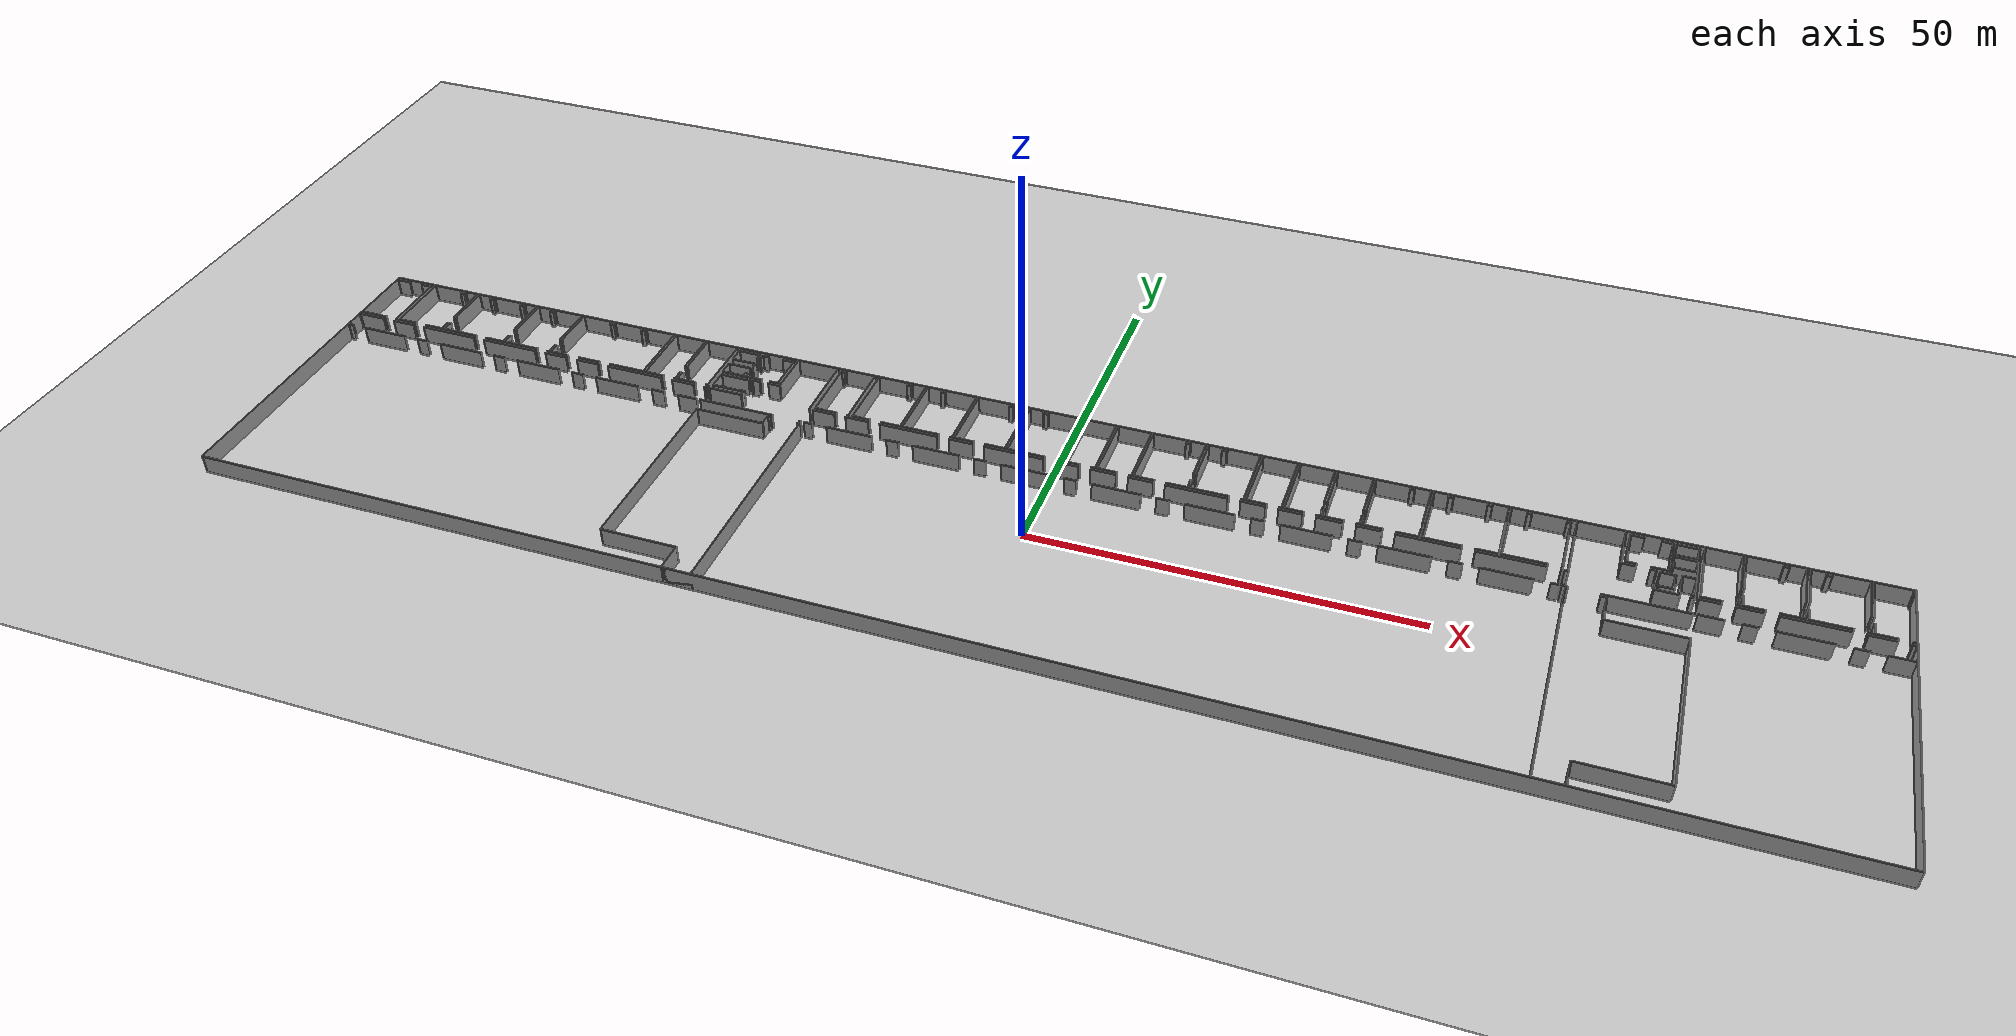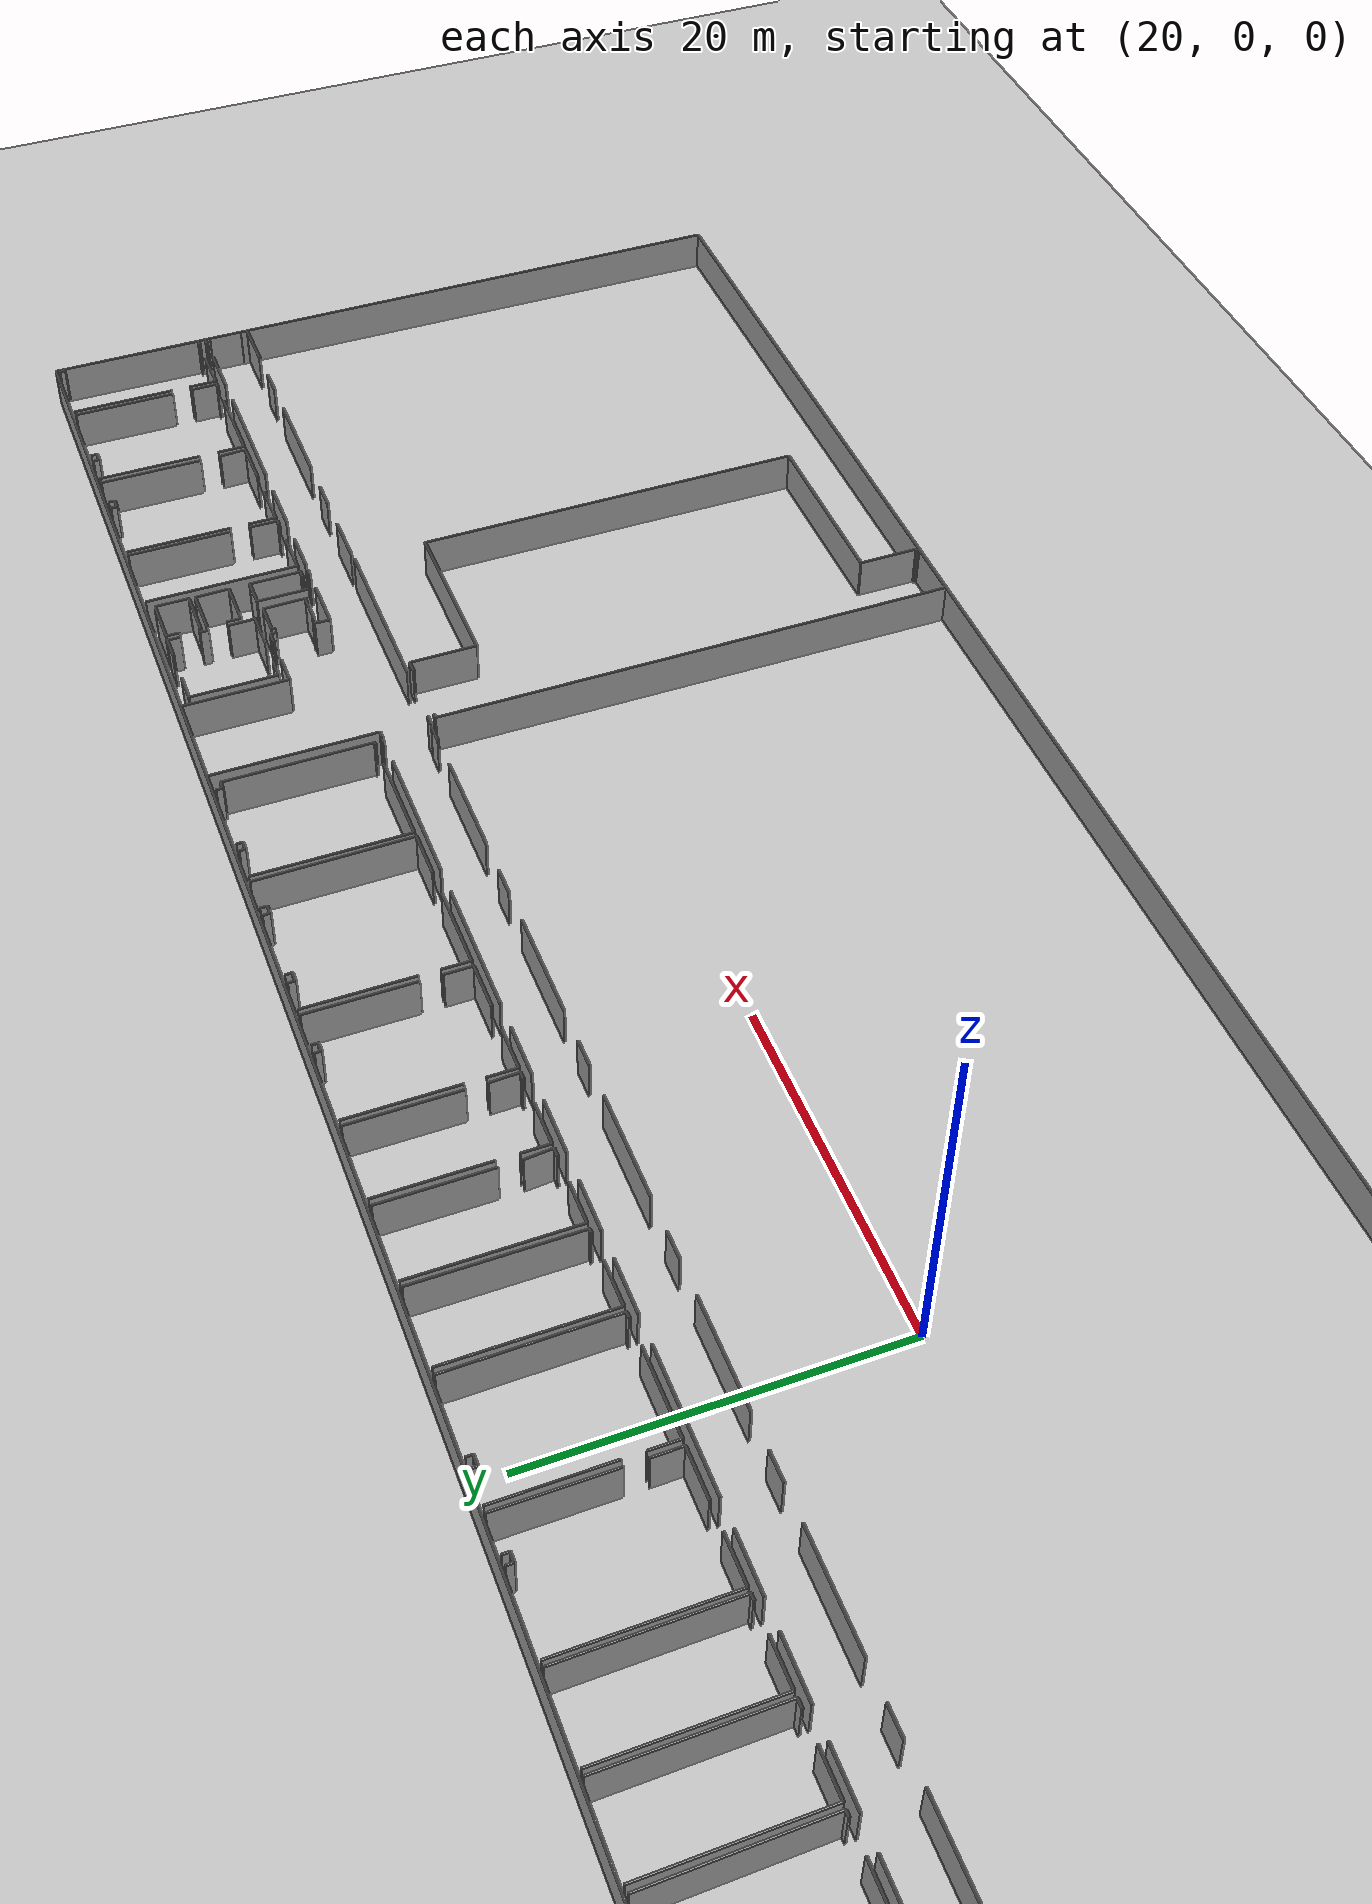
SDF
<sdf version="1.6">
  <world name="default">
    <light name="sun" type="directional">
      <cast_shadows>1</cast_shadows>
      <pose frame="">0 0 10 0 -0 0</pose>
      <diffuse>0.8 0.8 0.8 1</diffuse>
      <specular>0.1 0.1 0.1 1</specular>
      <attenuation>
        <range>1000</range>
        <constant>0.9</constant>
        <linear>0.01</linear>
        <quadratic>0.001</quadratic>
      </attenuation>
      <direction>-0.5 0.5 -1</direction>
    </light>
    <model name="ground_plane">
      <static>1</static>
      <link name="link">
        <collision name="collision">
          <geometry>
            <plane>
              <normal>0 0 1</normal>
              <size>100 100</size>
            </plane>
          </geometry>
          <surface>
            <friction>
              <ode>
                <mu>100</mu>
                <mu2>50</mu2>
              </ode>
              <torsional>
                <ode />
              </torsional>
            </friction>
            <contact>
              <ode />
            </contact>
            <bounce />
          </surface>
          <max_contacts>10</max_contacts>
        </collision>
        <visual name="visual">
          <cast_shadows>0</cast_shadows>
          <geometry>
            <plane>
              <normal>0 0 1</normal>
              <size>100 100</size>
            </plane>
          </geometry>
          <material>
            <script>
              <uri>file://media/materials/scripts/gazebo.material</uri>
              <name>Gazebo/Grey</name>
            </script>
          </material>
        </visual>
        <self_collide>0</self_collide>
        <kinematic>0</kinematic>
        <gravity>1</gravity>
      </link>
    </model>
    <gravity>0 0 -9.8</gravity>
    <magnetic_field>6e-06 2.3e-05 -4.2e-05</magnetic_field>
    <atmosphere type="adiabatic" />
    <physics default="0" name="default_physics" type="ode">
      <max_step_size>0.001</max_step_size>
      <real_time_factor>1</real_time_factor>
      <real_time_update_rate>1000</real_time_update_rate>
    </physics>
    <scene>
      <ambient>0.4 0.4 0.4 1</ambient>
      <background>0.7 0.7 0.7 1</background>
      <shadows>1</shadows>
    </scene>
    <spherical_coordinates>
      <surface_model>EARTH_WGS84</surface_model>
      <latitude_deg>0</latitude_deg>
      <longitude_deg>0</longitude_deg>
      <elevation>0</elevation>
      <heading_deg>0</heading_deg>
    </spherical_coordinates>
  <model name="50010536_PLAN4">
		<static>1</static>
		<link name="Wall_0">
			<collision name="Wall_0_Collision">
				<geometry>
					<box>
						<size>2.76519696537 0.1 2.5</size>
					</box>
				</geometry>
				<pose frame="">1.38259848268 0 1.25 0 0 0</pose>
			</collision>
			<visual name="Wall_0_Visual">
				<pose frame="">1.38259848268 0 1.25 0 0 0</pose>
				<geometry>
					<box>
						<size>2.76519696537 0.1 2.5</size>
					</box>
				</geometry>
				<material>
					<script>
						<uri>file://media/materials/scripts/gazebo.material</uri>
						<name>Gazebo/Grey</name>
					</script>
					<ambient>1 1 1 1</ambient>
				</material>
			</visual>
			<pose frame="">53.7737231375 -12.5419166429 0 0 0 3.14159265359</pose>
		</link>
		<link name="Wall_1">
			<collision name="Wall_1_Collision">
				<geometry>
					<box>
						<size>1.85861663969 0.1 2.5</size>
					</box>
				</geometry>
				<pose frame="">0.929308319843 0 1.25 0 0 0</pose>
			</collision>
			<visual name="Wall_1_Visual">
				<pose frame="">0.929308319843 0 1.25 0 0 0</pose>
				<geometry>
					<box>
						<size>1.85861663969 0.1 2.5</size>
					</box>
				</geometry>
				<material>
					<script>
						<uri>file://media/materials/scripts/gazebo.material</uri>
						<name>Gazebo/Grey</name>
					</script>
					<ambient>1 1 1 1</ambient>
				</material>
			</visual>
			<pose frame="">48.9759578453 -12.5419166429 0 0 0 3.14159265359</pose>
		</link>
		<link name="Wall_2">
			<collision name="Wall_2_Collision">
				<geometry>
					<box>
						<size>6.31584293559 0.1 2.5</size>
					</box>
				</geometry>
				<pose frame="">3.1579214678 0 1.25 0 0 0</pose>
			</collision>
			<visual name="Wall_2_Visual">
				<pose frame="">3.1579214678 0 1.25 0 0 0</pose>
				<geometry>
					<box>
						<size>6.31584293559 0.1 2.5</size>
					</box>
				</geometry>
				<material>
					<script>
						<uri>file://media/materials/scripts/gazebo.material</uri>
						<name>Gazebo/Grey</name>
					</script>
					<ambient>1 1 1 1</ambient>
				</material>
			</visual>
			<pose frame="">45.0700441228 -12.5419166429 0 0 0 3.14159265359</pose>
		</link>
		<link name="Wall_3">
			<collision name="Wall_3_Collision">
				<geometry>
					<box>
						<size>1.71336063232 0.1 2.5</size>
					</box>
				</geometry>
				<pose frame="">0.85668031616 0 1.25 0 0 0</pose>
			</collision>
			<visual name="Wall_3_Visual">
				<pose frame="">0.85668031616 0 1.25 0 0 0</pose>
				<geometry>
					<box>
						<size>1.71336063232 0.1 2.5</size>
					</box>
				</geometry>
				<material>
					<script>
						<uri>file://media/materials/scripts/gazebo.material</uri>
						<name>Gazebo/Grey</name>
					</script>
					<ambient>1 1 1 1</ambient>
				</material>
			</visual>
			<pose frame="">36.8376852998 -12.5419166429 0 0 0 3.14159265359</pose>
		</link>
		<link name="Wall_4">
			<collision name="Wall_4_Collision">
				<geometry>
					<box>
						<size>6.37399612735 0.1 2.5</size>
					</box>
				</geometry>
				<pose frame="">3.18699806368 0 1.25 0 0 0</pose>
			</collision>
			<visual name="Wall_4_Visual">
				<pose frame="">3.18699806368 0 1.25 0 0 0</pose>
				<geometry>
					<box>
						<size>6.37399612735 0.1 2.5</size>
					</box>
				</geometry>
				<material>
					<script>
						<uri>file://media/materials/scripts/gazebo.material</uri>
						<name>Gazebo/Grey</name>
					</script>
					<ambient>1 1 1 1</ambient>
				</material>
			</visual>
			<pose frame="">33.1207059645 -12.5419166429 0 0 0 3.14159265359</pose>
		</link>
		<link name="Wall_5">
			<collision name="Wall_5_Collision">
				<geometry>
					<box>
						<size>1.72783544424 0.1 2.5</size>
					</box>
				</geometry>
				<pose frame="">0.863917722122 0 1.25 0 0 0</pose>
			</collision>
			<visual name="Wall_5_Visual">
				<pose frame="">0.863917722122 0 1.25 0 0 0</pose>
				<geometry>
					<box>
						<size>1.72783544424 0.1 2.5</size>
					</box>
				</geometry>
				<material>
					<script>
						<uri>file://media/materials/scripts/gazebo.material</uri>
						<name>Gazebo/Grey</name>
					</script>
					<ambient>1 1 1 1</ambient>
				</material>
			</visual>
			<pose frame="">24.8012443259 -12.5419166429 0 0 0 3.14159265359</pose>
		</link>
		<link name="Wall_6">
			<collision name="Wall_6_Collision">
				<geometry>
					<box>
						<size>6.37399612735 0.1 2.5</size>
					</box>
				</geometry>
				<pose frame="">3.18699806368 0 1.25 0 0 0</pose>
			</collision>
			<visual name="Wall_6_Visual">
				<pose frame="">3.18699806368 0 1.25 0 0 0</pose>
				<geometry>
					<box>
						<size>6.37399612735 0.1 2.5</size>
					</box>
				</geometry>
				<material>
					<script>
						<uri>file://media/materials/scripts/gazebo.material</uri>
						<name>Gazebo/Grey</name>
					</script>
					<ambient>1 1 1 1</ambient>
				</material>
			</visual>
			<pose frame="">21.1132146145 -12.5419166429 0 0 0 3.14159265359</pose>
		</link>
		<link name="Wall_7">
			<collision name="Wall_7_Collision">
				<geometry>
					<box>
						<size>1.61152906072 0.1 2.5</size>
					</box>
				</geometry>
				<pose frame="">0.805764530362 0 1.25 0 0 0</pose>
			</collision>
			<visual name="Wall_7_Visual">
				<pose frame="">0.805764530362 0 1.25 0 0 0</pose>
				<geometry>
					<box>
						<size>1.61152906072 0.1 2.5</size>
					</box>
				</geometry>
				<material>
					<script>
						<uri>file://media/materials/scripts/gazebo.material</uri>
						<name>Gazebo/Grey</name>
					</script>
					<ambient>1 1 1 1</ambient>
				</material>
			</visual>
			<pose frame="">12.6919214043 -12.5419166429 0 0 0 3.14159265359</pose>
		</link>
		<link name="Wall_8">
			<collision name="Wall_8_Collision">
				<geometry>
					<box>
						<size>6.3760022855 0.1 2.5</size>
					</box>
				</geometry>
				<pose frame="">3.18800114275 0 1.25 0 0 0</pose>
			</collision>
			<visual name="Wall_8_Visual">
				<pose frame="">3.18800114275 0 1.25 0 0 0</pose>
				<geometry>
					<box>
						<size>6.3760022855 0.1 2.5</size>
					</box>
				</geometry>
				<material>
					<script>
						<uri>file://media/materials/scripts/gazebo.material</uri>
						<name>Gazebo/Grey</name>
					</script>
					<ambient>1 1 1 1</ambient>
				</material>
			</visual>
			<pose frame="">9.07677364061 -12.5419166429 0 0 0 3.14159265359</pose>
		</link>
		<link name="Wall_9">
			<collision name="Wall_9_Collision">
				<geometry>
					<box>
						<size>0.779481319239 0.1 2.5</size>
					</box>
				</geometry>
				<pose frame="">0.38974065962 0 1.25 0 0 0</pose>
			</collision>
			<visual name="Wall_9_Visual">
				<pose frame="">0.38974065962 0 1.25 0 0 0</pose>
				<geometry>
					<box>
						<size>0.779481319239 0.1 2.5</size>
					</box>
				</geometry>
				<material>
					<script>
						<uri>file://media/materials/scripts/gazebo.material</uri>
						<name>Gazebo/Grey</name>
					</script>
					<ambient>1 1 1 1</ambient>
				</material>
			</visual>
			<pose frame="">0.779481319239 -12.5419166429 0 0 0 3.14159265359</pose>
		</link>
		<link name="Wall_10">
			<collision name="Wall_10_Collision">
				<geometry>
					<box>
						<size>0.465479478145 0.1 2.5</size>
					</box>
				</geometry>
				<pose frame="">0.232739739072 0 1.25 0 0 0</pose>
			</collision>
			<visual name="Wall_10_Visual">
				<pose frame="">0.232739739072 0 1.25 0 0 0</pose>
				<geometry>
					<box>
						<size>0.465479478145 0.1 2.5</size>
					</box>
				</geometry>
				<material>
					<script>
						<uri>file://media/materials/scripts/gazebo.material</uri>
						<name>Gazebo/Grey</name>
					</script>
					<ambient>1 1 1 1</ambient>
				</material>
			</visual>
			<pose frame="">0.0 -12.5419166429 0 0 0 1.57079632679</pose>
		</link>
		<link name="Wall_11">
			<collision name="Wall_11_Collision">
				<geometry>
					<box>
						<size>0.38424277053 0.1 2.5</size>
					</box>
				</geometry>
				<pose frame="">0.192121385265 0 1.25 0 0 0</pose>
			</collision>
			<visual name="Wall_11_Visual">
				<pose frame="">0.192121385265 0 1.25 0 0 0</pose>
				<geometry>
					<box>
						<size>0.38424277053 0.1 2.5</size>
					</box>
				</geometry>
				<material>
					<script>
						<uri>file://media/materials/scripts/gazebo.material</uri>
						<name>Gazebo/Grey</name>
					</script>
					<ambient>1 1 1 1</ambient>
				</material>
			</visual>
			<pose frame="">0.0 -10.1113671714 0 0 0 1.57079632679</pose>
		</link>
		<link name="Wall_12">
			<collision name="Wall_12_Collision">
				<geometry>
					<box>
						<size>3.85352506111 0.1 2.5</size>
					</box>
				</geometry>
				<pose frame="">1.92676253055 0 1.25 0 0 0</pose>
			</collision>
			<visual name="Wall_12_Visual">
				<pose frame="">1.92676253055 0 1.25 0 0 0</pose>
				<geometry>
					<box>
						<size>3.85352506111 0.1 2.5</size>
					</box>
				</geometry>
				<material>
					<script>
						<uri>file://media/materials/scripts/gazebo.material</uri>
						<name>Gazebo/Grey</name>
					</script>
					<ambient>1 1 1 1</ambient>
				</material>
			</visual>
			<pose frame="">0.0 -9.72712440085 0 0 0 0.0</pose>
		</link>
		<link name="Wall_13">
			<collision name="Wall_13_Collision">
				<geometry>
					<box>
						<size>3.21462717836 0.1 2.5</size>
					</box>
				</geometry>
				<pose frame="">1.60731358918 0 1.25 0 0 0</pose>
			</collision>
			<visual name="Wall_13_Visual">
				<pose frame="">1.60731358918 0 1.25 0 0 0</pose>
				<geometry>
					<box>
						<size>3.21462717836 0.1 2.5</size>
					</box>
				</geometry>
				<material>
					<script>
						<uri>file://media/materials/scripts/gazebo.material</uri>
						<name>Gazebo/Grey</name>
					</script>
					<ambient>1 1 1 1</ambient>
				</material>
			</visual>
			<pose frame="">5.41469701298 -9.72712440085 0 0 0 0.0</pose>
		</link>
		<link name="Wall_14">
			<collision name="Wall_14_Collision">
				<geometry>
					<box>
						<size>7.98552518808 0.1 2.5</size>
					</box>
				</geometry>
				<pose frame="">3.99276259404 0 1.25 0 0 0</pose>
			</collision>
			<visual name="Wall_14_Visual">
				<pose frame="">3.99276259404 0 1.25 0 0 0</pose>
				<geometry>
					<box>
						<size>7.98552518808 0.1 2.5</size>
					</box>
				</geometry>
				<material>
					<script>
						<uri>file://media/materials/scripts/gazebo.material</uri>
						<name>Gazebo/Grey</name>
					</script>
					<ambient>1 1 1 1</ambient>
				</material>
			</visual>
			<pose frame="">10.2527886233 -9.72712440085 0 0 0 0.0</pose>
		</link>
		<link name="Wall_15">
			<collision name="Wall_15_Collision">
				<geometry>
					<box>
						<size>7.99974605593 0.1 2.5</size>
					</box>
				</geometry>
				<pose frame="">3.99987302797 0 1.25 0 0 0</pose>
			</collision>
			<visual name="Wall_15_Visual">
				<pose frame="">3.99987302797 0 1.25 0 0 0</pose>
				<geometry>
					<box>
						<size>7.99974605593 0.1 2.5</size>
					</box>
				</geometry>
				<material>
					<script>
						<uri>file://media/materials/scripts/gazebo.material</uri>
						<name>Gazebo/Grey</name>
					</script>
					<ambient>1 1 1 1</ambient>
				</material>
			</visual>
			<pose frame="">19.8229248008 -9.72712440085 0 0 0 0.0</pose>
		</link>
		<link name="Wall_16">
			<collision name="Wall_16_Collision">
				<geometry>
					<box>
						<size>3.1859822874 0.1 2.5</size>
					</box>
				</geometry>
				<pose frame="">1.5929911437 0 1.25 0 0 0</pose>
			</collision>
			<visual name="Wall_16_Visual">
				<pose frame="">1.5929911437 0 1.25 0 0 0</pose>
				<geometry>
					<box>
						<size>3.1859822874 0.1 2.5</size>
					</box>
				</geometry>
				<material>
					<script>
						<uri>file://media/materials/scripts/gazebo.material</uri>
						<name>Gazebo/Grey</name>
					</script>
					<ambient>1 1 1 1</ambient>
				</material>
			</visual>
			<pose frame="">29.4555312192 -9.72712440085 0 0 0 0.0</pose>
		</link>
		<link name="Wall_17">
			<collision name="Wall_17_Collision">
				<geometry>
					<box>
						<size>3.19436244167 0.1 2.5</size>
					</box>
				</geometry>
				<pose frame="">1.59718122084 0 1.25 0 0 0</pose>
			</collision>
			<visual name="Wall_17_Visual">
				<pose frame="">1.59718122084 0 1.25 0 0 0</pose>
				<geometry>
					<box>
						<size>3.19436244167 0.1 2.5</size>
					</box>
				</geometry>
				<material>
					<script>
						<uri>file://media/materials/scripts/gazebo.material</uri>
						<name>Gazebo/Grey</name>
					</script>
					<ambient>1 1 1 1</ambient>
				</material>
			</visual>
			<pose frame="">34.2677713234 -9.72712440085 0 0 0 0.0</pose>
		</link>
		<link name="Wall_18">
			<collision name="Wall_18_Collision">
				<geometry>
					<box>
						<size>8.01472875599 0.1 2.5</size>
					</box>
				</geometry>
				<pose frame="">4.007364378 0 1.25 0 0 0</pose>
			</collision>
			<visual name="Wall_18_Visual">
				<pose frame="">4.007364378 0 1.25 0 0 0</pose>
				<geometry>
					<box>
						<size>8.01472875599 0.1 2.5</size>
					</box>
				</geometry>
				<material>
					<script>
						<uri>file://media/materials/scripts/gazebo.material</uri>
						<name>Gazebo/Grey</name>
					</script>
					<ambient>1 1 1 1</ambient>
				</material>
			</visual>
			<pose frame="">39.0010348221 -9.72712440085 0 0 0 0.0</pose>
		</link>
		<link name="Wall_19">
			<collision name="Wall_19_Collision">
				<geometry>
					<box>
						<size>3.18166523823 0.1 2.5</size>
					</box>
				</geometry>
				<pose frame="">1.59083261912 0 1.25 0 0 0</pose>
			</collision>
			<visual name="Wall_19_Visual">
				<pose frame="">1.59083261912 0 1.25 0 0 0</pose>
				<geometry>
					<box>
						<size>3.18166523823 0.1 2.5</size>
					</box>
				</geometry>
				<material>
					<script>
						<uri>file://media/materials/scripts/gazebo.material</uri>
						<name>Gazebo/Grey</name>
					</script>
					<ambient>1 1 1 1</ambient>
				</material>
			</visual>
			<pose frame="">48.6570040948 -9.72712440085 0 0 0 0.0</pose>
		</link>
		<link name="Wall_20">
			<collision name="Wall_20_Collision">
				<geometry>
					<box>
						<size>0.30752626734 0.1 2.5</size>
					</box>
				</geometry>
				<pose frame="">0.15376313367 0 1.25 0 0 0</pose>
			</collision>
			<visual name="Wall_20_Visual">
				<pose frame="">0.15376313367 0 1.25 0 0 0</pose>
				<geometry>
					<box>
						<size>0.30752626734 0.1 2.5</size>
					</box>
				</geometry>
				<material>
					<script>
						<uri>file://media/materials/scripts/gazebo.material</uri>
						<name>Gazebo/Grey</name>
					</script>
					<ambient>1 1 1 1</ambient>
				</material>
			</visual>
			<pose frame="">53.4222645462 -9.72712440085 0 0 0 0.0</pose>
		</link>
		<link name="Wall_21">
			<collision name="Wall_21_Collision">
				<geometry>
					<box>
						<size>0.14932537456 0.1 2.5</size>
					</box>
				</geometry>
				<pose frame="">0.0746626872802 0 1.25 0 0 0</pose>
			</collision>
			<visual name="Wall_21_Visual">
				<pose frame="">0.0746626872802 0 1.25 0 0 0</pose>
				<geometry>
					<box>
						<size>0.14932537456 0.1 2.5</size>
					</box>
				</geometry>
				<material>
					<script>
						<uri>file://media/materials/scripts/gazebo.material</uri>
						<name>Gazebo/Grey</name>
					</script>
					<ambient>1 1 1 1</ambient>
				</material>
			</visual>
			<pose frame="">53.7297908136 -9.72712440085 0 0 0 -1.27217236395</pose>
		</link>
		<link name="Wall_22">
			<collision name="Wall_22_Collision">
				<geometry>
					<box>
						<size>0.196197187569 0.1 2.5</size>
					</box>
				</geometry>
				<pose frame="">0.0980985937847 0 1.25 0 0 0</pose>
			</collision>
			<visual name="Wall_22_Visual">
				<pose frame="">0.0980985937847 0 1.25 0 0 0</pose>
				<geometry>
					<box>
						<size>0.196197187569 0.1 2.5</size>
					</box>
				</geometry>
				<material>
					<script>
						<uri>file://media/materials/scripts/gazebo.material</uri>
						<name>Gazebo/Grey</name>
					</script>
					<ambient>1 1 1 1</ambient>
				</material>
			</visual>
			<pose frame="">5.59443862489 -9.21463987557 0 0 0 3.14159265359</pose>
		</link>
		<link name="Wall_23">
			<collision name="Wall_23_Collision">
				<geometry>
					<box>
						<size>3.92384217376 0.1 2.5</size>
					</box>
				</geometry>
				<pose frame="">1.96192108688 0 1.25 0 0 0</pose>
			</collision>
			<visual name="Wall_23_Visual">
				<pose frame="">1.96192108688 0 1.25 0 0 0</pose>
				<geometry>
					<box>
						<size>3.92384217376 0.1 2.5</size>
					</box>
				</geometry>
				<material>
					<script>
						<uri>file://media/materials/scripts/gazebo.material</uri>
						<name>Gazebo/Grey</name>
					</script>
					<ambient>1 1 1 1</ambient>
				</material>
			</visual>
			<pose frame="">3.92889566073 -9.21463987557 0 0 0 3.14159265359</pose>
		</link>
		<link name="Wall_24">
			<collision name="Wall_24_Collision">
				<geometry>
					<box>
						<size>8.73316192109 0.1 2.5</size>
					</box>
				</geometry>
				<pose frame="">4.36658096054 0 1.25 0 0 0</pose>
			</collision>
			<visual name="Wall_24_Visual">
				<pose frame="">4.36658096054 0 1.25 0 0 0</pose>
				<geometry>
					<box>
						<size>8.73316192109 0.1 2.5</size>
					</box>
				</geometry>
				<material>
					<script>
						<uri>file://media/materials/scripts/gazebo.material</uri>
						<name>Gazebo/Grey</name>
					</script>
					<ambient>1 1 1 1</ambient>
				</material>
			</visual>
			<pose frame="">0.0050534869695 -9.21463987557 0 0 0 1.57079632679</pose>
		</link>
		<link name="Wall_25">
			<collision name="Wall_25_Collision">
				<geometry>
					<box>
						<size>2.000749135 0.1 2.5</size>
					</box>
				</geometry>
				<pose frame="">1.0003745675 0 1.25 0 0 0</pose>
			</collision>
			<visual name="Wall_25_Visual">
				<pose frame="">1.0003745675 0 1.25 0 0 0</pose>
				<geometry>
					<box>
						<size>2.000749135 0.1 2.5</size>
					</box>
				</geometry>
				<material>
					<script>
						<uri>file://media/materials/scripts/gazebo.material</uri>
						<name>Gazebo/Grey</name>
					</script>
					<ambient>1 1 1 1</ambient>
				</material>
			</visual>
			<pose frame="">0.0050534869695 -0.481477954481 0 0 0 0.0</pose>
		</link>
		<link name="Wall_26">
			<collision name="Wall_26_Collision">
				<geometry>
					<box>
						<size>1.62709583214 0.1 2.5</size>
					</box>
				</geometry>
				<pose frame="">0.813547916071 0 1.25 0 0 0</pose>
			</collision>
			<visual name="Wall_26_Visual">
				<pose frame="">0.813547916071 0 1.25 0 0 0</pose>
				<geometry>
					<box>
						<size>1.62709583214 0.1 2.5</size>
					</box>
				</geometry>
				<material>
					<script>
						<uri>file://media/materials/scripts/gazebo.material</uri>
						<name>Gazebo/Grey</name>
					</script>
					<ambient>1 1 1 1</ambient>
				</material>
			</visual>
			<pose frame="">3.9343300638 -0.481477954481 0 0 0 0.0</pose>
		</link>
		<link name="Wall_27">
			<collision name="Wall_27_Collision">
				<geometry>
					<box>
						<size>8.73322431752 0.1 2.5</size>
					</box>
				</geometry>
				<pose frame="">4.36661215876 0 1.25 0 0 0</pose>
			</collision>
			<visual name="Wall_27_Visual">
				<pose frame="">4.36661215876 0 1.25 0 0 0</pose>
				<geometry>
					<box>
						<size>8.73322431752 0.1 2.5</size>
					</box>
				</geometry>
				<material>
					<script>
						<uri>file://media/materials/scripts/gazebo.material</uri>
						<name>Gazebo/Grey</name>
					</script>
					<ambient>1 1 1 1</ambient>
				</material>
			</visual>
			<pose frame="">5.56142589595 -0.481477954481 0 0 0 -1.56701618714</pose>
		</link>
		<link name="Wall_28">
			<collision name="Wall_28_Collision">
				<geometry>
					<box>
						<size>2.67657048535 0.1 2.5</size>
					</box>
				</geometry>
				<pose frame="">1.33828524268 0 1.25 0 0 0</pose>
			</collision>
			<visual name="Wall_28_Visual">
				<pose frame="">1.33828524268 0 1.25 0 0 0</pose>
				<geometry>
					<box>
						<size>2.67657048535 0.1 2.5</size>
					</box>
				</geometry>
				<material>
					<script>
						<uri>file://media/materials/scripts/gazebo.material</uri>
						<name>Gazebo/Grey</name>
					</script>
					<ambient>1 1 1 1</ambient>
				</material>
			</visual>
			<pose frame="">12.9141224645 -9.19244516395 0 0 0 3.14159265359</pose>
		</link>
		<link name="Wall_29">
			<collision name="Wall_29_Collision">
				<geometry>
					<box>
						<size>2.57557692918 0.1 2.5</size>
					</box>
				</geometry>
				<pose frame="">1.28778846459 0 1.25 0 0 0</pose>
			</collision>
			<visual name="Wall_29_Visual">
				<pose frame="">1.28778846459 0 1.25 0 0 0</pose>
				<geometry>
					<box>
						<size>2.57557692918 0.1 2.5</size>
					</box>
				</geometry>
				<material>
					<script>
						<uri>file://media/materials/scripts/gazebo.material</uri>
						<name>Gazebo/Grey</name>
					</script>
					<ambient>1 1 1 1</ambient>
				</material>
			</visual>
			<pose frame="">8.68468399835 -9.19244516395 0 0 0 3.14159265359</pose>
		</link>
		<link name="Wall_30">
			<collision name="Wall_30_Collision">
				<geometry>
					<box>
						<size>8.97070120306 0.1 2.5</size>
					</box>
				</geometry>
				<pose frame="">4.48535060153 0 1.25 0 0 0</pose>
			</collision>
			<visual name="Wall_30_Visual">
				<pose frame="">4.48535060153 0 1.25 0 0 0</pose>
				<geometry>
					<box>
						<size>8.97070120306 0.1 2.5</size>
					</box>
				</geometry>
				<material>
					<script>
						<uri>file://media/materials/scripts/gazebo.material</uri>
						<name>Gazebo/Grey</name>
					</script>
					<ambient>1 1 1 1</ambient>
				</material>
			</visual>
			<pose frame="">6.10910706917 -9.19244516395 0 0 0 1.57079632679</pose>
		</link>
		<link name="Wall_31">
			<collision name="Wall_31_Collision">
				<geometry>
					<box>
						<size>0.353718693458 0.1 2.5</size>
					</box>
				</geometry>
				<pose frame="">0.176859346729 0 1.25 0 0 0</pose>
			</collision>
			<visual name="Wall_31_Visual">
				<pose frame="">0.176859346729 0 1.25 0 0 0</pose>
				<geometry>
					<box>
						<size>0.353718693458 0.1 2.5</size>
					</box>
				</geometry>
				<material>
					<script>
						<uri>file://media/materials/scripts/gazebo.material</uri>
						<name>Gazebo/Grey</name>
					</script>
					<ambient>1 1 1 1</ambient>
				</material>
			</visual>
			<pose frame="">10.4229311494 -0.221743960893 0 0 0 -1.57079632679</pose>
		</link>
		<link name="Wall_32">
			<collision name="Wall_32_Collision">
				<geometry>
					<box>
						<size>0.584579246421 0.1 2.5</size>
					</box>
				</geometry>
				<pose frame="">0.29228962321 0 1.25 0 0 0</pose>
			</collision>
			<visual name="Wall_32_Visual">
				<pose frame="">0.29228962321 0 1.25 0 0 0</pose>
				<geometry>
					<box>
						<size>0.584579246421 0.1 2.5</size>
					</box>
				</geometry>
				<material>
					<script>
						<uri>file://media/materials/scripts/gazebo.material</uri>
						<name>Gazebo/Grey</name>
					</script>
					<ambient>1 1 1 1</ambient>
				</material>
			</visual>
			<pose frame="">10.4229311494 -0.57546265435 0 0 0 0.0</pose>
		</link>
		<link name="Wall_33">
			<collision name="Wall_33_Collision">
				<geometry>
					<box>
						<size>0.368168110974 0.1 2.5</size>
					</box>
				</geometry>
				<pose frame="">0.184084055487 0 1.25 0 0 0</pose>
			</collision>
			<visual name="Wall_33_Visual">
				<pose frame="">0.184084055487 0 1.25 0 0 0</pose>
				<geometry>
					<box>
						<size>0.368168110974 0.1 2.5</size>
					</box>
				</geometry>
				<material>
					<script>
						<uri>file://media/materials/scripts/gazebo.material</uri>
						<name>Gazebo/Grey</name>
					</script>
					<ambient>1 1 1 1</ambient>
				</material>
			</visual>
			<pose frame="">11.0075103958 -0.57546265435 0 0 0 1.57079632679</pose>
		</link>
		<link name="Wall_34">
			<collision name="Wall_34_Collision">
				<geometry>
					<box>
						<size>6.12548646161 0.1 2.5</size>
					</box>
				</geometry>
				<pose frame="">3.0627432308 0 1.25 0 0 0</pose>
			</collision>
			<visual name="Wall_34_Visual">
				<pose frame="">3.0627432308 0 1.25 0 0 0</pose>
				<geometry>
					<box>
						<size>6.12548646161 0.1 2.5</size>
					</box>
				</geometry>
				<material>
					<script>
						<uri>file://media/materials/scripts/gazebo.material</uri>
						<name>Gazebo/Grey</name>
					</script>
					<ambient>1 1 1 1</ambient>
				</material>
			</visual>
			<pose frame="">12.9204710662 -0.207294543377 0 0 0 -1.57079632679</pose>
		</link>
		<link name="Wall_35">
			<collision name="Wall_35_Collision">
				<geometry>
					<box>
						<size>1.55128112404 0.1 2.5</size>
					</box>
				</geometry>
				<pose frame="">0.775640562021 0 1.25 0 0 0</pose>
			</collision>
			<visual name="Wall_35_Visual">
				<pose frame="">0.775640562021 0 1.25 0 0 0</pose>
				<geometry>
					<box>
						<size>1.55128112404 0.1 2.5</size>
					</box>
				</geometry>
				<material>
					<script>
						<uri>file://media/materials/scripts/gazebo.material</uri>
						<name>Gazebo/Grey</name>
					</script>
					<ambient>1 1 1 1</ambient>
				</material>
			</visual>
			<pose frame="">12.9204710662 -7.64117703076 0 0 0 -1.57488882772</pose>
		</link>
		<link name="Wall_36">
			<collision name="Wall_36_Collision">
				<geometry>
					<box>
						<size>2.74640510428 0.1 2.5</size>
					</box>
				</geometry>
				<pose frame="">1.37320255214 0 1.25 0 0 0</pose>
			</collision>
			<visual name="Wall_36_Visual">
				<pose frame="">1.37320255214 0 1.25 0 0 0</pose>
				<geometry>
					<box>
						<size>2.74640510428 0.1 2.5</size>
					</box>
				</geometry>
				<material>
					<script>
						<uri>file://media/materials/scripts/gazebo.material</uri>
						<name>Gazebo/Grey</name>
					</script>
					<ambient>1 1 1 1</ambient>
				</material>
			</visual>
			<pose frame="">22.5629813034 -9.18292226137 0 0 0 3.14159265359</pose>
		</link>
		<link name="Wall_37">
			<collision name="Wall_37_Collision">
				<geometry>
					<box>
						<size>4.97349458782 0.1 2.5</size>
					</box>
				</geometry>
				<pose frame="">2.48674729391 0 1.25 0 0 0</pose>
			</collision>
			<visual name="Wall_37_Visual">
				<pose frame="">2.48674729391 0 1.25 0 0 0</pose>
				<geometry>
					<box>
						<size>4.97349458782 0.1 2.5</size>
					</box>
				</geometry>
				<material>
					<script>
						<uri>file://media/materials/scripts/gazebo.material</uri>
						<name>Gazebo/Grey</name>
					</script>
					<ambient>1 1 1 1</ambient>
				</material>
			</visual>
			<pose frame="">18.2576135606 -9.18292226137 0 0 0 3.14159265359</pose>
		</link>
		<link name="Wall_38">
			<collision name="Wall_38_Collision">
				<geometry>
					<box>
						<size>1.53077484684 0.1 2.5</size>
					</box>
				</geometry>
				<pose frame="">0.76538742342 0 1.25 0 0 0</pose>
			</collision>
			<visual name="Wall_38_Visual">
				<pose frame="">0.76538742342 0 1.25 0 0 0</pose>
				<geometry>
					<box>
						<size>1.53077484684 0.1 2.5</size>
					</box>
				</geometry>
				<material>
					<script>
						<uri>file://media/materials/scripts/gazebo.material</uri>
						<name>Gazebo/Grey</name>
					</script>
					<ambient>1 1 1 1</ambient>
				</material>
			</visual>
			<pose frame="">13.2841189728 -9.18292226137 0 0 0 1.57079632679</pose>
		</link>
		<link name="Wall_39">
			<collision name="Wall_39_Collision">
				<geometry>
					<box>
						<size>6.12764498619 0.1 2.5</size>
					</box>
				</geometry>
				<pose frame="">3.0638224931 0 1.25 0 0 0</pose>
			</collision>
			<visual name="Wall_39_Visual">
				<pose frame="">3.0638224931 0 1.25 0 0 0</pose>
				<geometry>
					<box>
						<size>6.12764498619 0.1 2.5</size>
					</box>
				</geometry>
				<material>
					<script>
						<uri>file://media/materials/scripts/gazebo.material</uri>
						<name>Gazebo/Grey</name>
					</script>
					<ambient>1 1 1 1</ambient>
				</material>
			</visual>
			<pose frame="">13.2841189728 -6.33278100498 0 0 0 1.57079632679</pose>
		</link>
		<link name="Wall_40">
			<collision name="Wall_40_Collision">
				<geometry>
					<box>
						<size>0.373577119639 0.1 2.5</size>
					</box>
				</geometry>
				<pose frame="">0.18678855982 0 1.25 0 0 0</pose>
			</collision>
			<visual name="Wall_40_Visual">
				<pose frame="">0.18678855982 0 1.25 0 0 0</pose>
				<geometry>
					<box>
						<size>0.373577119639 0.1 2.5</size>
					</box>
				</geometry>
				<material>
					<script>
						<uri>file://media/materials/scripts/gazebo.material</uri>
						<name>Gazebo/Grey</name>
					</script>
					<ambient>1 1 1 1</ambient>
				</material>
			</visual>
			<pose frame="">15.2161254484 -0.205136018792 0 0 0 -1.57079632679</pose>
		</link>
		<link name="Wall_41">
			<collision name="Wall_41_Collision">
				<geometry>
					<box>
						<size>0.564517664984 0.1 2.5</size>
					</box>
				</geometry>
				<pose frame="">0.282258832492 0 1.25 0 0 0</pose>
			</collision>
			<visual name="Wall_41_Visual">
				<pose frame="">0.282258832492 0 1.25 0 0 0</pose>
				<geometry>
					<box>
						<size>0.564517664984 0.1 2.5</size>
					</box>
				</geometry>
				<material>
					<script>
						<uri>file://media/materials/scripts/gazebo.material</uri>
						<name>Gazebo/Grey</name>
					</script>
					<ambient>1 1 1 1</ambient>
				</material>
			</visual>
			<pose frame="">15.2161254484 -0.578713138431 0 0 0 0.0</pose>
		</link>
		<link name="Wall_42">
			<collision name="Wall_42_Collision">
				<geometry>
					<box>
						<size>0.373577119639 0.1 2.5</size>
					</box>
				</geometry>
				<pose frame="">0.18678855982 0 1.25 0 0 0</pose>
			</collision>
			<visual name="Wall_42_Visual">
				<pose frame="">0.18678855982 0 1.25 0 0 0</pose>
				<geometry>
					<box>
						<size>0.373577119639 0.1 2.5</size>
					</box>
				</geometry>
				<material>
					<script>
						<uri>file://media/materials/scripts/gazebo.material</uri>
						<name>Gazebo/Grey</name>
					</script>
					<ambient>1 1 1 1</ambient>
				</material>
			</visual>
			<pose frame="">15.7806431134 -0.578713138431 0 0 0 1.57079632679</pose>
		</link>
		<link name="Wall_43">
			<collision name="Wall_43_Collision">
				<geometry>
					<box>
						<size>0.365273148589 0.1 2.5</size>
					</box>
				</geometry>
				<pose frame="">0.182636574295 0 1.25 0 0 0</pose>
			</collision>
			<visual name="Wall_43_Visual">
				<pose frame="">0.182636574295 0 1.25 0 0 0</pose>
				<geometry>
					<box>
						<size>0.365273148589 0.1 2.5</size>
					</box>
				</geometry>
				<material>
					<script>
						<uri>file://media/materials/scripts/gazebo.material</uri>
						<name>Gazebo/Grey</name>
					</script>
					<ambient>1 1 1 1</ambient>
				</material>
			</visual>
			<pose frame="">19.98951211 -0.205136018792 0 0 0 -1.57079632679</pose>
		</link>
		<link name="Wall_44">
			<collision name="Wall_44_Collision">
				<geometry>
					<box>
						<size>0.589404183729 0.1 2.5</size>
					</box>
				</geometry>
				<pose frame="">0.294702091864 0 1.25 0 0 0</pose>
			</collision>
			<visual name="Wall_44_Visual">
				<pose frame="">0.294702091864 0 1.25 0 0 0</pose>
				<geometry>
					<box>
						<size>0.589404183729 0.1 2.5</size>
					</box>
				</geometry>
				<material>
					<script>
						<uri>file://media/materials/scripts/gazebo.material</uri>
						<name>Gazebo/Grey</name>
					</script>
					<ambient>1 1 1 1</ambient>
				</material>
			</visual>
			<pose frame="">19.98951211 -0.570409167381 0 0 0 0.0</pose>
		</link>
		<link name="Wall_45">
			<collision name="Wall_45_Collision">
				<geometry>
					<box>
						<size>0.365273148589 0.1 2.5</size>
					</box>
				</geometry>
				<pose frame="">0.182636574295 0 1.25 0 0 0</pose>
			</collision>
			<visual name="Wall_45_Visual">
				<pose frame="">0.182636574295 0 1.25 0 0 0</pose>
				<geometry>
					<box>
						<size>0.365273148589 0.1 2.5</size>
					</box>
				</geometry>
				<material>
					<script>
						<uri>file://media/materials/scripts/gazebo.material</uri>
						<name>Gazebo/Grey</name>
					</script>
					<ambient>1 1 1 1</ambient>
				</material>
			</visual>
			<pose frame="">20.5789162937 -0.570409167381 0 0 0 1.57079632679</pose>
		</link>
		<link name="Wall_46">
			<collision name="Wall_46_Collision">
				<geometry>
					<box>
						<size>6.09663841539 0.1 2.5</size>
					</box>
				</geometry>
				<pose frame="">3.04831920769 0 1.25 0 0 0</pose>
			</collision>
			<visual name="Wall_46_Visual">
				<pose frame="">3.04831920769 0 1.25 0 0 0</pose>
				<geometry>
					<box>
						<size>6.09663841539 0.1 2.5</size>
					</box>
				</geometry>
				<material>
					<script>
						<uri>file://media/materials/scripts/gazebo.material</uri>
						<name>Gazebo/Grey</name>
					</script>
					<ambient>1 1 1 1</ambient>
				</material>
			</visual>
			<pose frame="">22.5213344761 -0.205136018792 0 0 0 -1.57079632679</pose>
		</link>
		<link name="Wall_47">
			<collision name="Wall_47_Collision">
				<geometry>
					<box>
						<size>1.55329942336 0.1 2.5</size>
					</box>
				</geometry>
				<pose frame="">0.77664971168 0 1.25 0 0 0</pose>
			</collision>
			<visual name="Wall_47_Visual">
				<pose frame="">0.77664971168 0 1.25 0 0 0</pose>
				<geometry>
					<box>
						<size>1.55329942336 0.1 2.5</size>
					</box>
				</geometry>
				<material>
					<script>
						<uri>file://media/materials/scripts/gazebo.material</uri>
						<name>Gazebo/Grey</name>
					</script>
					<ambient>1 1 1 1</ambient>
				</material>
			</visual>
			<pose frame="">22.5213344761 -7.63018125258 0 0 0 -1.54398126584</pose>
		</link>
		<link name="Wall_48">
			<collision name="Wall_48_Collision">
				<geometry>
					<box>
						<size>0.306256546996 0.1 2.5</size>
					</box>
				</geometry>
				<pose frame="">0.153128273498 0 1.25 0 0 0</pose>
			</collision>
			<visual name="Wall_48_Visual">
				<pose frame="">0.153128273498 0 1.25 0 0 0</pose>
				<geometry>
					<box>
						<size>0.306256546996 0.1 2.5</size>
					</box>
				</geometry>
				<material>
					<script>
						<uri>file://media/materials/scripts/gazebo.material</uri>
						<name>Gazebo/Grey</name>
					</script>
					<ambient>1 1 1 1</ambient>
				</material>
			</visual>
			<pose frame="">29.7440116814 -9.17982414373 0 0 0 3.14159265359</pose>
		</link>
		<link name="Wall_49">
			<collision name="Wall_49_Collision">
				<geometry>
					<box>
						<size>5.00625337269 0.1 2.5</size>
					</box>
				</geometry>
				<pose frame="">2.50312668635 0 1.25 0 0 0</pose>
			</collision>
			<visual name="Wall_49_Visual">
				<pose frame="">2.50312668635 0 1.25 0 0 0</pose>
				<geometry>
					<box>
						<size>5.00625337269 0.1 2.5</size>
					</box>
				</geometry>
				<material>
					<script>
						<uri>file://media/materials/scripts/gazebo.material</uri>
						<name>Gazebo/Grey</name>
					</script>
					<ambient>1 1 1 1</ambient>
				</material>
			</visual>
			<pose frame="">27.8749833349 -9.17982414373 0 0 0 3.14159265359</pose>
		</link>
		<link name="Wall_50">
			<collision name="Wall_50_Collision">
				<geometry>
					<box>
						<size>1.51670634543 0.1 2.5</size>
					</box>
				</geometry>
				<pose frame="">0.758353172714 0 1.25 0 0 0</pose>
			</collision>
			<visual name="Wall_50_Visual">
				<pose frame="">0.758353172714 0 1.25 0 0 0</pose>
				<geometry>
					<box>
						<size>1.51670634543 0.1 2.5</size>
					</box>
				</geometry>
				<material>
					<script>
						<uri>file://media/materials/scripts/gazebo.material</uri>
						<name>Gazebo/Grey</name>
					</script>
					<ambient>1 1 1 1</ambient>
				</material>
			</visual>
			<pose frame="">22.8687299622 -9.17982414373 0 0 0 1.57079632679</pose>
		</link>
		<link name="Wall_51">
			<collision name="Wall_51_Collision">
				<geometry>
					<box>
						<size>6.12675618195 0.1 2.5</size>
					</box>
				</geometry>
				<pose frame="">3.06337809098 0 1.25 0 0 0</pose>
			</collision>
			<visual name="Wall_51_Visual">
				<pose frame="">3.06337809098 0 1.25 0 0 0</pose>
				<geometry>
					<box>
						<size>6.12675618195 0.1 2.5</size>
					</box>
				</geometry>
				<material>
					<script>
						<uri>file://media/materials/scripts/gazebo.material</uri>
						<name>Gazebo/Grey</name>
					</script>
					<ambient>1 1 1 1</ambient>
				</material>
			</visual>
			<pose frame="">22.8687299622 -6.33438085262 0 0 0 1.57079632679</pose>
		</link>
		<link name="Wall_52">
			<collision name="Wall_52_Collision">
				<geometry>
					<box>
						<size>0.372332793702 0.1 2.5</size>
					</box>
				</geometry>
				<pose frame="">0.186166396851 0 1.25 0 0 0</pose>
			</collision>
			<visual name="Wall_52_Visual">
				<pose frame="">0.186166396851 0 1.25 0 0 0</pose>
				<geometry>
					<box>
						<size>0.372332793702 0.1 2.5</size>
					</box>
				</geometry>
				<material>
					<script>
						<uri>file://media/materials/scripts/gazebo.material</uri>
						<name>Gazebo/Grey</name>
					</script>
					<ambient>1 1 1 1</ambient>
				</material>
			</visual>
			<pose frame="">24.8075929277 -0.207624670666 0 0 0 -1.57079632679</pose>
		</link>
		<link name="Wall_53">
			<collision name="Wall_53_Collision">
				<geometry>
					<box>
						<size>0.610989429578 0.1 2.5</size>
					</box>
				</geometry>
				<pose frame="">0.305494714789 0 1.25 0 0 0</pose>
			</collision>
			<visual name="Wall_53_Visual">
				<pose frame="">0.305494714789 0 1.25 0 0 0</pose>
				<geometry>
					<box>
						<size>0.610989429578 0.1 2.5</size>
					</box>
				</geometry>
				<material>
					<script>
						<uri>file://media/materials/scripts/gazebo.material</uri>
						<name>Gazebo/Grey</name>
					</script>
					<ambient>1 1 1 1</ambient>
				</material>
			</visual>
			<pose frame="">24.8075929277 -0.579957464368 0 0 0 0.0</pose>
		</link>
		<link name="Wall_54">
			<collision name="Wall_54_Collision">
				<geometry>
					<box>
						<size>0.38188109069 0.1 2.5</size>
					</box>
				</geometry>
				<pose frame="">0.190940545345 0 1.25 0 0 0</pose>
			</collision>
			<visual name="Wall_54_Visual">
				<pose frame="">0.190940545345 0 1.25 0 0 0</pose>
				<geometry>
					<box>
						<size>0.38188109069 0.1 2.5</size>
					</box>
				</geometry>
				<material>
					<script>
						<uri>file://media/materials/scripts/gazebo.material</uri>
						<name>Gazebo/Grey</name>
					</script>
					<ambient>1 1 1 1</ambient>
				</material>
			</visual>
			<pose frame="">25.4185823572 -0.579957464368 0 0 0 1.57079632679</pose>
		</link>
		<link name="Wall_55">
			<collision name="Wall_55_Collision">
				<geometry>
					<box>
						<size>6.21309716535 0.1 2.5</size>
					</box>
				</geometry>
				<pose frame="">3.10654858267 0 1.25 0 0 0</pose>
			</collision>
			<visual name="Wall_55_Visual">
				<pose frame="">3.10654858267 0 1.25 0 0 0</pose>
				<geometry>
					<box>
						<size>6.21309716535 0.1 2.5</size>
					</box>
				</geometry>
				<material>
					<script>
						<uri>file://media/materials/scripts/gazebo.material</uri>
						<name>Gazebo/Grey</name>
					</script>
					<ambient>1 1 1 1</ambient>
				</material>
			</visual>
			<pose frame="">29.7399485763 -0.198076373679 0 0 0 -1.57079632679</pose>
		</link>
		<link name="Wall_56">
			<collision name="Wall_56_Collision">
				<geometry>
					<box>
						<size>1.59982739872 0.1 2.5</size>
					</box>
				</geometry>
				<pose frame="">0.799913699362 0 1.25 0 0 0</pose>
			</collision>
			<visual name="Wall_56_Visual">
				<pose frame="">0.799913699362 0 1.25 0 0 0</pose>
				<geometry>
					<box>
						<size>1.59982739872 0.1 2.5</size>
					</box>
				</geometry>
				<material>
					<script>
						<uri>file://media/materials/scripts/gazebo.material</uri>
						<name>Gazebo/Grey</name>
					</script>
					<ambient>1 1 1 1</ambient>
				</material>
			</visual>
			<pose frame="">29.7399485763 -7.58000190458 0 0 0 -1.5682566094</pose>
		</link>
		<link name="Wall_57">
			<collision name="Wall_57_Collision">
				<geometry>
					<box>
						<size>5.11722693077 0.1 2.5</size>
					</box>
				</geometry>
				<pose frame="">2.55861346538 0 1.25 0 0 0</pose>
			</collision>
			<visual name="Wall_57_Visual">
				<pose frame="">2.55861346538 0 1.25 0 0 0</pose>
				<geometry>
					<box>
						<size>5.11722693077 0.1 2.5</size>
					</box>
				</geometry>
				<material>
					<script>
						<uri>file://media/materials/scripts/gazebo.material</uri>
						<name>Gazebo/Grey</name>
					</script>
					<ambient>1 1 1 1</ambient>
				</material>
			</visual>
			<pose frame="">44.1025172206 -9.18292226137 0 0 0 3.14159265359</pose>
		</link>
		<link name="Wall_58">
			<collision name="Wall_58_Collision">
				<geometry>
					<box>
						<size>3.23423166048 0.1 2.5</size>
					</box>
				</geometry>
				<pose frame="">1.61711583024 0 1.25 0 0 0</pose>
			</collision>
			<visual name="Wall_58_Visual">
				<pose frame="">1.61711583024 0 1.25 0 0 0</pose>
				<geometry>
					<box>
						<size>3.23423166048 0.1 2.5</size>
					</box>
				</geometry>
				<material>
					<script>
						<uri>file://media/materials/scripts/gazebo.material</uri>
						<name>Gazebo/Grey</name>
					</script>
					<ambient>1 1 1 1</ambient>
				</material>
			</visual>
			<pose frame="">37.458324604 -9.18292226137 0 0 0 3.14159265359</pose>
		</link>
		<link name="Wall_59">
			<collision name="Wall_59_Collision">
				<geometry>
					<box>
						<size>2.49855569311 0.1 2.5</size>
					</box>
				</geometry>
				<pose frame="">1.24927784655 0 1.25 0 0 0</pose>
			</collision>
			<visual name="Wall_59_Visual">
				<pose frame="">1.24927784655 0 1.25 0 0 0</pose>
				<geometry>
					<box>
						<size>2.49855569311 0.1 2.5</size>
					</box>
				</geometry>
				<material>
					<script>
						<uri>file://media/materials/scripts/gazebo.material</uri>
						<name>Gazebo/Grey</name>
					</script>
					<ambient>1 1 1 1</ambient>
				</material>
			</visual>
			<pose frame="">32.583614259 -9.18292226137 0 0 0 3.14159265359</pose>
		</link>
		<link name="Wall_60">
			<collision name="Wall_60_Collision">
				<geometry>
					<box>
						<size>1.56866330191 0.1 2.5</size>
					</box>
				</geometry>
				<pose frame="">0.784331650954 0 1.25 0 0 0</pose>
			</collision>
			<visual name="Wall_60_Visual">
				<pose frame="">0.784331650954 0 1.25 0 0 0</pose>
				<geometry>
					<box>
						<size>1.56866330191 0.1 2.5</size>
					</box>
				</geometry>
				<material>
					<script>
						<uri>file://media/materials/scripts/gazebo.material</uri>
						<name>Gazebo/Grey</name>
					</script>
					<ambient>1 1 1 1</ambient>
				</material>
			</visual>
			<pose frame="">30.0850585659 -9.18292226137 0 0 0 1.57079632679</pose>
		</link>
		<link name="Wall_61">
			<collision name="Wall_61_Collision">
				<geometry>
					<box>
						<size>6.18869314034 0.1 2.5</size>
					</box>
				</geometry>
				<pose frame="">3.09434657017 0 1.25 0 0 0</pose>
			</collision>
			<visual name="Wall_61_Visual">
				<pose frame="">3.09434657017 0 1.25 0 0 0</pose>
				<geometry>
					<box>
						<size>6.18869314034 0.1 2.5</size>
					</box>
				</geometry>
				<material>
					<script>
						<uri>file://media/materials/scripts/gazebo.material</uri>
						<name>Gazebo/Grey</name>
					</script>
					<ambient>1 1 1 1</ambient>
				</material>
			</visual>
			<pose frame="">30.0850585659 -6.36434625274 0 0 0 1.57079632679</pose>
		</link>
		<link name="Wall_62">
			<collision name="Wall_62_Collision">
				<geometry>
					<box>
						<size>0.39523854871 0.1 2.5</size>
					</box>
				</geometry>
				<pose frame="">0.197619274355 0 1.25 0 0 0</pose>
			</collision>
			<visual name="Wall_62_Visual">
				<pose frame="">0.197619274355 0 1.25 0 0 0</pose>
				<geometry>
					<box>
						<size>0.39523854871 0.1 2.5</size>
					</box>
				</geometry>
				<material>
					<script>
						<uri>file://media/materials/scripts/gazebo.material</uri>
						<name>Gazebo/Grey</name>
					</script>
					<ambient>1 1 1 1</ambient>
				</material>
			</visual>
			<pose frame="">34.4071866171 -0.175653112402 0 0 0 -1.57079632679</pose>
		</link>
		<link name="Wall_63">
			<collision name="Wall_63_Collision">
				<geometry>
					<box>
						<size>0.549027076786 0.1 2.5</size>
					</box>
				</geometry>
				<pose frame="">0.274513538393 0 1.25 0 0 0</pose>
			</collision>
			<visual name="Wall_63_Visual">
				<pose frame="">0.274513538393 0 1.25 0 0 0</pose>
				<geometry>
					<box>
						<size>0.549027076786 0.1 2.5</size>
					</box>
				</geometry>
				<material>
					<script>
						<uri>file://media/materials/scripts/gazebo.material</uri>
						<name>Gazebo/Grey</name>
					</script>
					<ambient>1 1 1 1</ambient>
				</material>
			</visual>
			<pose frame="">34.4071866171 -0.570891661112 0 0 0 0.0</pose>
		</link>
		<link name="Wall_64">
			<collision name="Wall_64_Collision">
				<geometry>
					<box>
						<size>0.384268164937 0.1 2.5</size>
					</box>
				</geometry>
				<pose frame="">0.192134082468 0 1.25 0 0 0</pose>
			</collision>
			<visual name="Wall_64_Visual">
				<pose frame="">0.192134082468 0 1.25 0 0 0</pose>
				<geometry>
					<box>
						<size>0.384268164937 0.1 2.5</size>
					</box>
				</geometry>
				<material>
					<script>
						<uri>file://media/materials/scripts/gazebo.material</uri>
						<name>Gazebo/Grey</name>
					</script>
					<ambient>1 1 1 1</ambient>
				</material>
			</visual>
			<pose frame="">34.9562136939 -0.570891661112 0 0 0 1.57079632679</pose>
		</link>
		<link name="Wall_65">
			<collision name="Wall_65_Collision">
				<geometry>
					<box>
						<size>0.400393613307 0.1 2.5</size>
					</box>
				</geometry>
				<pose frame="">0.200196806653 0 1.25 0 0 0</pose>
			</collision>
			<visual name="Wall_65_Visual">
				<pose frame="">0.200196806653 0 1.25 0 0 0</pose>
				<geometry>
					<box>
						<size>0.400393613307 0.1 2.5</size>
					</box>
				</geometry>
				<material>
					<script>
						<uri>file://media/materials/scripts/gazebo.material</uri>
						<name>Gazebo/Grey</name>
					</script>
					<ambient>1 1 1 1</ambient>
				</material>
			</visual>
			<pose frame="">39.1907310415 -0.186623496175 0 0 0 -1.57079632679</pose>
		</link>
		<link name="Wall_66">
			<collision name="Wall_66_Collision">
				<geometry>
					<box>
						<size>0.597784338 0.1 2.5</size>
					</box>
				</geometry>
				<pose frame="">0.298892169 0 1.25 0 0 0</pose>
			</collision>
			<visual name="Wall_66_Visual">
				<pose frame="">0.298892169 0 1.25 0 0 0</pose>
				<geometry>
					<box>
						<size>0.597784338 0.1 2.5</size>
					</box>
				</geometry>
				<material>
					<script>
						<uri>file://media/materials/scripts/gazebo.material</uri>
						<name>Gazebo/Grey</name>
					</script>
					<ambient>1 1 1 1</ambient>
				</material>
			</visual>
			<pose frame="">39.1907310415 -0.587017109482 0 0 0 0.0</pose>
		</link>
		<link name="Wall_67">
			<collision name="Wall_67_Collision">
				<geometry>
					<box>
						<size>0.39018506174 0.1 2.5</size>
					</box>
				</geometry>
				<pose frame="">0.19509253087 0 1.25 0 0 0</pose>
			</collision>
			<visual name="Wall_67_Visual">
				<pose frame="">0.19509253087 0 1.25 0 0 0</pose>
				<geometry>
					<box>
						<size>0.39018506174 0.1 2.5</size>
					</box>
				</geometry>
				<material>
					<script>
						<uri>file://media/materials/scripts/gazebo.material</uri>
						<name>Gazebo/Grey</name>
					</script>
					<ambient>1 1 1 1</ambient>
				</material>
			</visual>
			<pose frame="">39.7885153795 -0.587017109482 0 0 0 1.57079632679</pose>
		</link>
		<link name="Wall_68">
			<collision name="Wall_68_Collision">
				<geometry>
					<box>
						<size>8.98609195031 0.1 2.5</size>
					</box>
				</geometry>
				<pose frame="">4.49304597516 0 1.25 0 0 0</pose>
			</collision>
			<visual name="Wall_68_Visual">
				<pose frame="">4.49304597516 0 1.25 0 0 0</pose>
				<geometry>
					<box>
						<size>8.98609195031 0.1 2.5</size>
					</box>
				</geometry>
				<material>
					<script>
						<uri>file://media/materials/scripts/gazebo.material</uri>
						<name>Gazebo/Grey</name>
					</script>
					<ambient>1 1 1 1</ambient>
				</material>
			</visual>
			<pose frame="">44.0969304511 -0.196832047741 0 0 0 -1.57017461383</pose>
		</link>
		<link name="Wall_69">
			<collision name="Wall_69_Collision">
				<geometry>
					<box>
						<size>0.261308446815 0.1 2.5</size>
					</box>
				</geometry>
				<pose frame="">0.130654223407 0 1.25 0 0 0</pose>
			</collision>
			<visual name="Wall_69_Visual">
				<pose frame="">0.130654223407 0 1.25 0 0 0</pose>
				<geometry>
					<box>
						<size>0.261308446815 0.1 2.5</size>
					</box>
				</geometry>
				<material>
					<script>
						<uri>file://media/materials/scripts/gazebo.material</uri>
						<name>Gazebo/Grey</name>
					</script>
					<ambient>1 1 1 1</ambient>
				</material>
			</visual>
			<pose frame="">48.9322794654 -9.20760562486 0 0 0 3.14159265359</pose>
		</link>
		<link name="Wall_70">
			<collision name="Wall_70_Collision">
				<geometry>
					<box>
						<size>2.60470431387 0.1 2.5</size>
					</box>
				</geometry>
				<pose frame="">1.30235215694 0 1.25 0 0 0</pose>
			</collision>
			<visual name="Wall_70_Visual">
				<pose frame="">1.30235215694 0 1.25 0 0 0</pose>
				<geometry>
					<box>
						<size>2.60470431387 0.1 2.5</size>
					</box>
				</geometry>
				<material>
					<script>
						<uri>file://media/materials/scripts/gazebo.material</uri>
						<name>Gazebo/Grey</name>
					</script>
					<ambient>1 1 1 1</ambient>
				</material>
			</visual>
			<pose frame="">47.0911849665 -9.20760562486 0 0 0 3.14159265359</pose>
		</link>
		<link name="Wall_71">
			<collision name="Wall_71_Collision">
				<geometry>
					<box>
						<size>9.02098212869 0.1 2.5</size>
					</box>
				</geometry>
				<pose frame="">4.51049106434 0 1.25 0 0 0</pose>
			</collision>
			<visual name="Wall_71_Visual">
				<pose frame="">4.51049106434 0 1.25 0 0 0</pose>
				<geometry>
					<box>
						<size>9.02098212869 0.1 2.5</size>
					</box>
				</geometry>
				<material>
					<script>
						<uri>file://media/materials/scripts/gazebo.material</uri>
						<name>Gazebo/Grey</name>
					</script>
					<ambient>1 1 1 1</ambient>
				</material>
			</visual>
			<pose frame="">44.4864806526 -9.20760562486 0 0 0 1.57079632679</pose>
		</link>
		<link name="Wall_72">
			<collision name="Wall_72_Collision">
				<geometry>
					<box>
						<size>6.15248071612 0.1 2.5</size>
					</box>
				</geometry>
				<pose frame="">3.07624035806 0 1.25 0 0 0</pose>
			</collision>
			<visual name="Wall_72_Visual">
				<pose frame="">3.07624035806 0 1.25 0 0 0</pose>
				<geometry>
					<box>
						<size>6.15248071612 0.1 2.5</size>
					</box>
				</geometry>
				<material>
					<script>
						<uri>file://media/materials/scripts/gazebo.material</uri>
						<name>Gazebo/Grey</name>
					</script>
					<ambient>1 1 1 1</ambient>
				</material>
			</visual>
			<pose frame="">48.8952036314 -0.186623496175 0 0 0 -1.57079632679</pose>
		</link>
		<link name="Wall_73">
			<collision name="Wall_73_Collision">
				<geometry>
					<box>
						<size>1.50540536487 0.1 2.5</size>
					</box>
				</geometry>
				<pose frame="">0.752702682434 0 1.25 0 0 0</pose>
			</collision>
			<visual name="Wall_73_Visual">
				<pose frame="">0.752702682434 0 1.25 0 0 0</pose>
				<geometry>
					<box>
						<size>1.50540536487 0.1 2.5</size>
					</box>
				</geometry>
				<material>
					<script>
						<uri>file://media/materials/scripts/gazebo.material</uri>
						<name>Gazebo/Grey</name>
					</script>
					<ambient>1 1 1 1</ambient>
				</material>
			</visual>
			<pose frame="">48.8952036314 -7.70265688982 0 0 0 -1.54616536422</pose>
		</link>
		<link name="Wall_74">
			<collision name="Wall_74_Collision">
				<geometry>
					<box>
						<size>0.302955274101 0.1 2.5</size>
					</box>
				</geometry>
				<pose frame="">0.15147763705 0 1.25 0 0 0</pose>
			</collision>
			<visual name="Wall_74_Visual">
				<pose frame="">0.15147763705 0 1.25 0 0 0</pose>
				<geometry>
					<box>
						<size>0.302955274101 0.1 2.5</size>
					</box>
				</geometry>
				<material>
					<script>
						<uri>file://media/materials/scripts/gazebo.material</uri>
						<name>Gazebo/Grey</name>
					</script>
					<ambient>1 1 1 1</ambient>
				</material>
			</visual>
			<pose frame="">53.7071897914 -9.19244516395 0 0 0 3.14159265359</pose>
		</link>
		<link name="Wall_75">
			<collision name="Wall_75_Collision">
				<geometry>
					<box>
						<size>2.54858267467 0.1 2.5</size>
					</box>
				</geometry>
				<pose frame="">1.27429133733 0 1.25 0 0 0</pose>
			</collision>
			<visual name="Wall_75_Visual">
				<pose frame="">1.27429133733 0 1.25 0 0 0</pose>
				<geometry>
					<box>
						<size>2.54858267467 0.1 2.5</size>
					</box>
				</geometry>
				<material>
					<script>
						<uri>file://media/materials/scripts/gazebo.material</uri>
						<name>Gazebo/Grey</name>
					</script>
					<ambient>1 1 1 1</ambient>
				</material>
			</visual>
			<pose frame="">51.808957877 -9.19244516395 0 0 0 3.14159265359</pose>
		</link>
		<link name="Wall_76">
			<collision name="Wall_76_Collision">
				<geometry>
					<box>
						<size>1.48277941783 0.1 2.5</size>
					</box>
				</geometry>
				<pose frame="">0.741389708917 0 1.25 0 0 0</pose>
			</collision>
			<visual name="Wall_76_Visual">
				<pose frame="">0.741389708917 0 1.25 0 0 0</pose>
				<geometry>
					<box>
						<size>1.48277941783 0.1 2.5</size>
					</box>
				</geometry>
				<material>
					<script>
						<uri>file://media/materials/scripts/gazebo.material</uri>
						<name>Gazebo/Grey</name>
					</script>
					<ambient>1 1 1 1</ambient>
				</material>
			</visual>
			<pose frame="">49.2603752024 -9.19244516395 0 0 0 1.57079632679</pose>
		</link>
		<link name="Wall_77">
			<collision name="Wall_77_Collision">
				<geometry>
					<box>
						<size>6.1405961337 0.1 2.5</size>
					</box>
				</geometry>
				<pose frame="">3.07029806685 0 1.25 0 0 0</pose>
			</collision>
			<visual name="Wall_77_Visual">
				<pose frame="">3.07029806685 0 1.25 0 0 0</pose>
				<geometry>
					<box>
						<size>6.1405961337 0.1 2.5</size>
					</box>
				</geometry>
				<material>
					<script>
						<uri>file://media/materials/scripts/gazebo.material</uri>
						<name>Gazebo/Grey</name>
					</script>
					<ambient>1 1 1 1</ambient>
				</material>
			</visual>
			<pose frame="">49.2603752024 -6.34822080437 0 0 0 1.57079632679</pose>
		</link>
		<link name="Wall_78">
			<collision name="Wall_78_Collision">
				<geometry>
					<box>
						<size>8.98489387824 0.1 2.5</size>
					</box>
				</geometry>
				<pose frame="">4.49244693912 0 1.25 0 0 0</pose>
			</collision>
			<visual name="Wall_78_Visual">
				<pose frame="">4.49244693912 0 1.25 0 0 0</pose>
				<geometry>
					<box>
						<size>8.98489387824 0.1 2.5</size>
					</box>
				</geometry>
				<material>
					<script>
						<uri>file://media/materials/scripts/gazebo.material</uri>
						<name>Gazebo/Grey</name>
					</script>
					<ambient>1 1 1 1</ambient>
				</material>
			</visual>
			<pose frame="">53.7435037933 -0.207624670666 0 0 0 -1.57483801067</pose>
		</link>
		<link name="Wall_79">
			<collision name="Wall_79_Collision">
				<geometry>
					<box>
						<size>0.267910992604 0.1 2.5</size>
					</box>
				</geometry>
				<pose frame="">0.133955496302 0 1.25 0 0 0</pose>
			</collision>
			<visual name="Wall_79_Visual">
				<pose frame="">0.133955496302 0 1.25 0 0 0</pose>
				<geometry>
					<box>
						<size>0.267910992604 0.1 2.5</size>
					</box>
				</geometry>
				<material>
					<script>
						<uri>file://media/materials/scripts/gazebo.material</uri>
						<name>Gazebo/Grey</name>
					</script>
					<ambient>1 1 1 1</ambient>
				</material>
			</visual>
			<pose frame="">68.7142684824 -12.4743675206 0 0 0 3.14159265359</pose>
		</link>
		<link name="Wall_80">
			<collision name="Wall_80_Collision">
				<geometry>
					<box>
						<size>10.4739231184 0.1 2.5</size>
					</box>
				</geometry>
				<pose frame="">5.23696155922 0 1.25 0 0 0</pose>
			</collision>
			<visual name="Wall_80_Visual">
				<pose frame="">5.23696155922 0 1.25 0 0 0</pose>
				<geometry>
					<box>
						<size>10.4739231184 0.1 2.5</size>
					</box>
				</geometry>
				<material>
					<script>
						<uri>file://media/materials/scripts/gazebo.material</uri>
						<name>Gazebo/Grey</name>
					</script>
					<ambient>1 1 1 1</ambient>
				</material>
			</visual>
			<pose frame="">64.6735104593 -12.4743675206 0 0 0 3.14159265359</pose>
		</link>
		<link name="Wall_81">
			<collision name="Wall_81_Collision">
				<geometry>
					<box>
						<size>0.174231025617 0.1 2.5</size>
					</box>
				</geometry>
				<pose frame="">0.0871155128083 0 1.25 0 0 0</pose>
			</collision>
			<visual name="Wall_81_Visual">
				<pose frame="">0.0871155128083 0 1.25 0 0 0</pose>
				<geometry>
					<box>
						<size>0.174231025617 0.1 2.5</size>
					</box>
				</geometry>
				<material>
					<script>
						<uri>file://media/materials/scripts/gazebo.material</uri>
						<name>Gazebo/Grey</name>
					</script>
					<ambient>1 1 1 1</ambient>
				</material>
			</visual>
			<pose frame="">54.1995873409 -9.90452972733 0 0 0 1.57079632679</pose>
		</link>
		<link name="Wall_82">
			<collision name="Wall_82_Collision">
				<geometry>
					<box>
						<size>4.64616068311 0.1 2.5</size>
					</box>
				</geometry>
				<pose frame="">2.32308034155 0 1.25 0 0 0</pose>
			</collision>
			<visual name="Wall_82_Visual">
				<pose frame="">2.32308034155 0 1.25 0 0 0</pose>
				<geometry>
					<box>
						<size>4.64616068311 0.1 2.5</size>
					</box>
				</geometry>
				<material>
					<script>
						<uri>file://media/materials/scripts/gazebo.material</uri>
						<name>Gazebo/Grey</name>
					</script>
					<ambient>1 1 1 1</ambient>
				</material>
			</visual>
			<pose frame="">54.1995873409 -9.73029870171 0 0 0 0.0</pose>
		</link>
		<link name="Wall_83">
			<collision name="Wall_83_Collision">
				<geometry>
					<box>
						<size>0.936367964956 0.1 2.5</size>
					</box>
				</geometry>
				<pose frame="">0.468183982478 0 1.25 0 0 0</pose>
			</collision>
			<visual name="Wall_83_Visual">
				<pose frame="">0.468183982478 0 1.25 0 0 0</pose>
				<geometry>
					<box>
						<size>0.936367964956 0.1 2.5</size>
					</box>
				</geometry>
				<material>
					<script>
						<uri>file://media/materials/scripts/gazebo.material</uri>
						<name>Gazebo/Grey</name>
					</script>
					<ambient>1 1 1 1</ambient>
				</material>
			</visual>
			<pose frame="">58.845748024 -9.73029870171 0 0 0 1.57079632679</pose>
		</link>
		<link name="Wall_84">
			<collision name="Wall_84_Collision">
				<geometry>
					<box>
						<size>0.315449322287 0.1 2.5</size>
					</box>
				</geometry>
				<pose frame="">0.157724661143 0 1.25 0 0 0</pose>
			</collision>
			<visual name="Wall_84_Visual">
				<pose frame="">0.157724661143 0 1.25 0 0 0</pose>
				<geometry>
					<box>
						<size>0.315449322287 0.1 2.5</size>
					</box>
				</geometry>
				<material>
					<script>
						<uri>file://media/materials/scripts/gazebo.material</uri>
						<name>Gazebo/Grey</name>
					</script>
					<ambient>1 1 1 1</ambient>
				</material>
			</visual>
			<pose frame="">58.845748024 -6.56407326286 0 0 0 1.57079632679</pose>
		</link>
		<link name="Wall_85">
			<collision name="Wall_85_Collision">
				<geometry>
					<box>
						<size>1.04066279402 0.1 2.5</size>
					</box>
				</geometry>
				<pose frame="">0.52033139701 0 1.25 0 0 0</pose>
			</collision>
			<visual name="Wall_85_Visual">
				<pose frame="">0.52033139701 0 1.25 0 0 0</pose>
				<geometry>
					<box>
						<size>1.04066279402 0.1 2.5</size>
					</box>
				</geometry>
				<material>
					<script>
						<uri>file://media/materials/scripts/gazebo.material</uri>
						<name>Gazebo/Grey</name>
					</script>
					<ambient>1 1 1 1</ambient>
				</material>
			</visual>
			<pose frame="">58.845748024 -6.24862394058 0 0 0 0.0</pose>
		</link>
		<link name="Wall_86">
			<collision name="Wall_86_Collision">
				<geometry>
					<box>
						<size>1.69050566613 0.1 2.5</size>
					</box>
				</geometry>
				<pose frame="">0.845252833064 0 1.25 0 0 0</pose>
			</collision>
			<visual name="Wall_86_Visual">
				<pose frame="">0.845252833064 0 1.25 0 0 0</pose>
				<geometry>
					<box>
						<size>1.69050566613 0.1 2.5</size>
					</box>
				</geometry>
				<material>
					<script>
						<uri>file://media/materials/scripts/gazebo.material</uri>
						<name>Gazebo/Grey</name>
					</script>
					<ambient>1 1 1 1</ambient>
				</material>
			</visual>
			<pose frame="">61.1624797638 -6.24862394058 0 0 0 0.0</pose>
		</link>
		<link name="Wall_87">
			<collision name="Wall_87_Collision">
				<geometry>
					<box>
						<size>6.23442846713 0.1 2.5</size>
					</box>
				</geometry>
				<pose frame="">3.11721423357 0 1.25 0 0 0</pose>
			</collision>
			<visual name="Wall_87_Visual">
				<pose frame="">3.11721423357 0 1.25 0 0 0</pose>
				<geometry>
					<box>
						<size>6.23442846713 0.1 2.5</size>
					</box>
				</geometry>
				<material>
					<script>
						<uri>file://media/materials/scripts/gazebo.material</uri>
						<name>Gazebo/Grey</name>
					</script>
					<ambient>1 1 1 1</ambient>
				</material>
			</visual>
			<pose frame="">62.85298543 -6.24862394058 0 0 0 1.57079632679</pose>
		</link>
		<link name="Wall_88">
			<collision name="Wall_88_Collision">
				<geometry>
					<box>
						<size>9.68648778193 0.1 2.5</size>
					</box>
				</geometry>
				<pose frame="">4.84324389096 0 1.25 0 0 0</pose>
			</collision>
			<visual name="Wall_88_Visual">
				<pose frame="">4.84324389096 0 1.25 0 0 0</pose>
				<geometry>
					<box>
						<size>9.68648778193 0.1 2.5</size>
					</box>
				</geometry>
				<material>
					<script>
						<uri>file://media/materials/scripts/gazebo.material</uri>
						<name>Gazebo/Grey</name>
					</script>
					<ambient>1 1 1 1</ambient>
				</material>
			</visual>
			<pose frame="">68.6609402279 -0.014195473447 0 0 0 -1.56529087166</pose>
		</link>
		<link name="Wall_89">
			<collision name="Wall_89_Collision">
				<geometry>
					<box>
						<size>4.09103894867 0.1 2.5</size>
					</box>
				</geometry>
				<pose frame="">2.04551947434 0 1.25 0 0 0</pose>
			</collision>
			<visual name="Wall_89_Visual">
				<pose frame="">2.04551947434 0 1.25 0 0 0</pose>
				<geometry>
					<box>
						<size>4.09103894867 0.1 2.5</size>
					</box>
				</geometry>
				<material>
					<script>
						<uri>file://media/materials/scripts/gazebo.material</uri>
						<name>Gazebo/Grey</name>
					</script>
					<ambient>1 1 1 1</ambient>
				</material>
			</visual>
			<pose frame="">58.4955591531 -8.96585087135 0 0 0 3.14159265359</pose>
		</link>
		<link name="Wall_90">
			<collision name="Wall_90_Collision">
				<geometry>
					<box>
						<size>2.55467733232 0.1 2.5</size>
					</box>
				</geometry>
				<pose frame="">1.27733866616 0 1.25 0 0 0</pose>
			</collision>
			<visual name="Wall_90_Visual">
				<pose frame="">1.27733866616 0 1.25 0 0 0</pose>
				<geometry>
					<box>
						<size>2.55467733232 0.1 2.5</size>
					</box>
				</geometry>
				<material>
					<script>
						<uri>file://media/materials/scripts/gazebo.material</uri>
						<name>Gazebo/Grey</name>
					</script>
					<ambient>1 1 1 1</ambient>
				</material>
			</visual>
			<pose frame="">54.4045202044 -8.96585087135 0 0 0 1.57079632679</pose>
		</link>
		<link name="Wall_91">
			<collision name="Wall_91_Collision">
				<geometry>
					<box>
						<size>4.04990000952 0.1 2.5</size>
					</box>
				</geometry>
				<pose frame="">2.02495000476 0 1.25 0 0 0</pose>
			</collision>
			<visual name="Wall_91_Visual">
				<pose frame="">2.02495000476 0 1.25 0 0 0</pose>
				<geometry>
					<box>
						<size>4.04990000952 0.1 2.5</size>
					</box>
				</geometry>
				<material>
					<script>
						<uri>file://media/materials/scripts/gazebo.material</uri>
						<name>Gazebo/Grey</name>
					</script>
					<ambient>1 1 1 1</ambient>
				</material>
			</visual>
			<pose frame="">54.4045202044 -6.41117353903 0 0 0 0.0</pose>
		</link>
		<link name="Wall_92">
			<collision name="Wall_92_Collision">
				<geometry>
					<box>
						<size>0.129917785608 0.1 2.5</size>
					</box>
				</geometry>
				<pose frame="">0.0649588928039 0 1.25 0 0 0</pose>
			</collision>
			<visual name="Wall_92_Visual">
				<pose frame="">0.0649588928039 0 1.25 0 0 0</pose>
				<geometry>
					<box>
						<size>0.129917785608 0.1 2.5</size>
					</box>
				</geometry>
				<material>
					<script>
						<uri>file://media/materials/scripts/gazebo.material</uri>
						<name>Gazebo/Grey</name>
					</script>
					<ambient>1 1 1 1</ambient>
				</material>
			</visual>
			<pose frame="">58.4544202139 -6.41117353903 0 0 0 -1.57079632679</pose>
		</link>
		<link name="Wall_93">
			<collision name="Wall_93_Collision">
				<geometry>
					<box>
						<size>0.198153012521 0.1 2.5</size>
					</box>
				</geometry>
				<pose frame="">0.0990765062603 0 1.25 0 0 0</pose>
			</collision>
			<visual name="Wall_93_Visual">
				<pose frame="">0.0990765062603 0 1.25 0 0 0</pose>
				<geometry>
					<box>
						<size>0.198153012521 0.1 2.5</size>
					</box>
				</geometry>
				<material>
					<script>
						<uri>file://media/materials/scripts/gazebo.material</uri>
						<name>Gazebo/Grey</name>
					</script>
					<ambient>1 1 1 1</ambient>
				</material>
			</visual>
			<pose frame="">58.4544202139 -8.77201536362 0 0 0 -1.36166321376</pose>
		</link>
		<link name="Wall_94">
			<collision name="Wall_94_Collision">
				<geometry>
					<box>
						<size>1.24051677618 0.1 2.5</size>
					</box>
				</geometry>
				<pose frame="">0.62025838809 0 1.25 0 0 0</pose>
			</collision>
			<visual name="Wall_94_Visual">
				<pose frame="">0.62025838809 0 1.25 0 0 0</pose>
				<geometry>
					<box>
						<size>1.24051677618 0.1 2.5</size>
					</box>
				</geometry>
				<material>
					<script>
						<uri>file://media/materials/scripts/gazebo.material</uri>
						<name>Gazebo/Grey</name>
					</script>
					<ambient>1 1 1 1</ambient>
				</material>
			</visual>
			<pose frame="">62.3699838111 -5.7638193188 0 0 0 3.14159265359</pose>
		</link>
		<link name="Wall_95">
			<collision name="Wall_95_Collision">
				<geometry>
					<box>
						<size>2.23953274291 0.1 2.5</size>
					</box>
				</geometry>
				<pose frame="">1.11976637146 0 1.25 0 0 0</pose>
			</collision>
			<visual name="Wall_95_Visual">
				<pose frame="">1.11976637146 0 1.25 0 0 0</pose>
				<geometry>
					<box>
						<size>2.23953274291 0.1 2.5</size>
					</box>
				</geometry>
				<material>
					<script>
						<uri>file://media/materials/scripts/gazebo.material</uri>
						<name>Gazebo/Grey</name>
					</script>
					<ambient>1 1 1 1</ambient>
				</material>
			</visual>
			<pose frame="">59.9765609624 -5.7638193188 0 0 0 3.14159265359</pose>
		</link>
		<link name="Wall_96">
			<collision name="Wall_96_Collision">
				<geometry>
					<box>
						<size>0.768510935466 0.1 2.5</size>
					</box>
				</geometry>
				<pose frame="">0.384255467733 0 1.25 0 0 0</pose>
			</collision>
			<visual name="Wall_96_Visual">
				<pose frame="">0.384255467733 0 1.25 0 0 0</pose>
				<geometry>
					<box>
						<size>0.768510935466 0.1 2.5</size>
					</box>
				</geometry>
				<material>
					<script>
						<uri>file://media/materials/scripts/gazebo.material</uri>
						<name>Gazebo/Grey</name>
					</script>
					<ambient>1 1 1 1</ambient>
				</material>
			</visual>
			<pose frame="">57.7370282195 -5.7638193188 0 0 0 1.57079632679</pose>
		</link>
		<link name="Wall_97">
			<collision name="Wall_97_Collision">
				<geometry>
					<box>
						<size>1.1966860299 0.1 2.5</size>
					</box>
				</geometry>
				<pose frame="">0.598343014951 0 1.25 0 0 0</pose>
			</collision>
			<visual name="Wall_97_Visual">
				<pose frame="">0.598343014951 0 1.25 0 0 0</pose>
				<geometry>
					<box>
						<size>1.1966860299 0.1 2.5</size>
					</box>
				</geometry>
				<material>
					<script>
						<uri>file://media/materials/scripts/gazebo.material</uri>
						<name>Gazebo/Grey</name>
					</script>
					<ambient>1 1 1 1</ambient>
				</material>
			</visual>
			<pose frame="">57.7370282195 -3.86449544488 0 0 0 1.57079632679</pose>
		</link>
		<link name="Wall_98">
			<collision name="Wall_98_Collision">
				<geometry>
					<box>
						<size>0.909043583151 0.1 2.5</size>
					</box>
				</geometry>
				<pose frame="">0.454521791575 0 1.25 0 0 0</pose>
			</collision>
			<visual name="Wall_98_Visual">
				<pose frame="">0.454521791575 0 1.25 0 0 0</pose>
				<geometry>
					<box>
						<size>0.909043583151 0.1 2.5</size>
					</box>
				</geometry>
				<material>
					<script>
						<uri>file://media/materials/scripts/gazebo.material</uri>
						<name>Gazebo/Grey</name>
					</script>
					<ambient>1 1 1 1</ambient>
				</material>
			</visual>
			<pose frame="">57.7370282195 -1.51614766848 0 0 0 1.57079632679</pose>
		</link>
		<link name="Wall_99">
			<collision name="Wall_99_Collision">
				<geometry>
					<box>
						<size>0.894137066311 0.1 2.5</size>
					</box>
				</geometry>
				<pose frame="">0.447068533156 0 1.25 0 0 0</pose>
			</collision>
			<visual name="Wall_99_Visual">
				<pose frame="">0.447068533156 0 1.25 0 0 0</pose>
				<geometry>
					<box>
						<size>0.894137066311 0.1 2.5</size>
					</box>
				</geometry>
				<material>
					<script>
						<uri>file://media/materials/scripts/gazebo.material</uri>
						<name>Gazebo/Grey</name>
					</script>
					<ambient>1 1 1 1</ambient>
				</material>
			</visual>
			<pose frame="">57.7370282195 -0.607104085325 0 0 0 0.0</pose>
		</link>
		<link name="Wall_100">
			<collision name="Wall_100_Collision">
				<geometry>
					<box>
						<size>1.71716979335 0.1 2.5</size>
					</box>
				</geometry>
				<pose frame="">0.858584896677 0 1.25 0 0 0</pose>
			</collision>
			<visual name="Wall_100_Visual">
				<pose frame="">0.858584896677 0 1.25 0 0 0</pose>
				<geometry>
					<box>
						<size>1.71716979335 0.1 2.5</size>
					</box>
				</geometry>
				<material>
					<script>
						<uri>file://media/materials/scripts/gazebo.material</uri>
						<name>Gazebo/Grey</name>
					</script>
					<ambient>1 1 1 1</ambient>
				</material>
			</visual>
			<pose frame="">60.6512903533 -0.607104085325 0 0 0 0.0</pose>
		</link>
		<link name="Wall_101">
			<collision name="Wall_101_Collision">
				<geometry>
					<box>
						<size>5.15671545857 0.1 2.5</size>
					</box>
				</geometry>
				<pose frame="">2.57835772928 0 1.25 0 0 0</pose>
			</collision>
			<visual name="Wall_101_Visual">
				<pose frame="">2.57835772928 0 1.25 0 0 0</pose>
				<geometry>
					<box>
						<size>5.15671545857 0.1 2.5</size>
					</box>
				</geometry>
				<material>
					<script>
						<uri>file://media/materials/scripts/gazebo.material</uri>
						<name>Gazebo/Grey</name>
					</script>
					<ambient>1 1 1 1</ambient>
				</material>
			</visual>
			<pose frame="">62.3684601467 -0.607104085325 0 0 0 -1.57050085491</pose>
		</link>
		<link name="Wall_102">
			<collision name="Wall_102_Collision">
				<geometry>
					<box>
						<size>2.99222296289 0.1 2.5</size>
					</box>
				</geometry>
				<pose frame="">1.49611148145 0 1.25 0 0 0</pose>
			</collision>
			<visual name="Wall_102_Visual">
				<pose frame="">1.49611148145 0 1.25 0 0 0</pose>
				<geometry>
					<box>
						<size>2.99222296289 0.1 2.5</size>
					</box>
				</geometry>
				<material>
					<script>
						<uri>file://media/materials/scripts/gazebo.material</uri>
						<name>Gazebo/Grey</name>
					</script>
					<ambient>1 1 1 1</ambient>
				</material>
			</visual>
			<pose frame="">57.2423451735 -5.7583087325 0 0 0 3.14159265359</pose>
		</link>
		<link name="Wall_103">
			<collision name="Wall_103_Collision">
				<geometry>
					<box>
						<size>1.93170174269 0.1 2.5</size>
					</box>
				</geometry>
				<pose frame="">0.965850871346 0 1.25 0 0 0</pose>
			</collision>
			<visual name="Wall_103_Visual">
				<pose frame="">0.965850871346 0 1.25 0 0 0</pose>
				<geometry>
					<box>
						<size>1.93170174269 0.1 2.5</size>
					</box>
				</geometry>
				<material>
					<script>
						<uri>file://media/materials/scripts/gazebo.material</uri>
						<name>Gazebo/Grey</name>
					</script>
					<ambient>1 1 1 1</ambient>
				</material>
			</visual>
			<pose frame="">54.2501222106 -5.7583087325 0 0 0 1.57079632679</pose>
		</link>
		<link name="Wall_104">
			<collision name="Wall_104_Collision">
				<geometry>
					<box>
						<size>3.04275783259 0.1 2.5</size>
					</box>
				</geometry>
				<pose frame="">1.52137891629 0 1.25 0 0 0</pose>
			</collision>
			<visual name="Wall_104_Visual">
				<pose frame="">1.52137891629 0 1.25 0 0 0</pose>
				<geometry>
					<box>
						<size>3.04275783259 0.1 2.5</size>
					</box>
				</geometry>
				<material>
					<script>
						<uri>file://media/materials/scripts/gazebo.material</uri>
						<name>Gazebo/Grey</name>
					</script>
					<ambient>1 1 1 1</ambient>
				</material>
			</visual>
			<pose frame="">54.2501222106 -3.82660698981 0 0 0 0.0</pose>
		</link>
		<link name="Wall_105">
			<collision name="Wall_105_Collision">
				<geometry>
					<box>
						<size>0.784412110821 0.1 2.5</size>
					</box>
				</geometry>
				<pose frame="">0.392206055411 0 1.25 0 0 0</pose>
			</collision>
			<visual name="Wall_105_Visual">
				<pose frame="">0.392206055411 0 1.25 0 0 0</pose>
				<geometry>
					<box>
						<size>0.784412110821 0.1 2.5</size>
					</box>
				</geometry>
				<material>
					<script>
						<uri>file://media/materials/scripts/gazebo.material</uri>
						<name>Gazebo/Grey</name>
					</script>
					<ambient>1 1 1 1</ambient>
				</material>
			</visual>
			<pose frame="">57.2928800432 -4.97552614037 0 0 0 -1.63526485221</pose>
		</link>
		<link name="Wall_106">
			<collision name="Wall_106_Collision">
				<geometry>
					<box>
						<size>0.851804590039 0.1 2.5</size>
					</box>
				</geometry>
				<pose frame="">0.42590229502 0 1.25 0 0 0</pose>
			</collision>
			<visual name="Wall_106_Visual">
				<pose frame="">0.42590229502 0 1.25 0 0 0</pose>
				<geometry>
					<box>
						<size>0.851804590039 0.1 2.5</size>
					</box>
				</geometry>
				<material>
					<script>
						<uri>file://media/materials/scripts/gazebo.material</uri>
						<name>Gazebo/Grey</name>
					</script>
					<ambient>1 1 1 1</ambient>
				</material>
			</visual>
			<pose frame="">57.2880551059 -1.45614068501 0 0 0 1.57079632679</pose>
		</link>
		<link name="Wall_107">
			<collision name="Wall_107_Collision">
				<geometry>
					<box>
						<size>3.03336190204 0.1 2.5</size>
					</box>
				</geometry>
				<pose frame="">1.51668095102 0 1.25 0 0 0</pose>
			</collision>
			<visual name="Wall_107_Visual">
				<pose frame="">1.51668095102 0 1.25 0 0 0</pose>
				<geometry>
					<box>
						<size>3.03336190204 0.1 2.5</size>
					</box>
				</geometry>
				<material>
					<script>
						<uri>file://media/materials/scripts/gazebo.material</uri>
						<name>Gazebo/Grey</name>
					</script>
					<ambient>1 1 1 1</ambient>
				</material>
			</visual>
			<pose frame="">57.2880551059 -0.604336094975 0 0 0 3.14159265359</pose>
		</link>
		<link name="Wall_108">
			<collision name="Wall_108_Collision">
				<geometry>
					<box>
						<size>2.08620131416 0.1 2.5</size>
					</box>
				</geometry>
				<pose frame="">1.04310065708 0 1.25 0 0 0</pose>
			</collision>
			<visual name="Wall_108_Visual">
				<pose frame="">1.04310065708 0 1.25 0 0 0</pose>
				<geometry>
					<box>
						<size>2.08620131416 0.1 2.5</size>
					</box>
				</geometry>
				<material>
					<script>
						<uri>file://media/materials/scripts/gazebo.material</uri>
						<name>Gazebo/Grey</name>
					</script>
					<ambient>1 1 1 1</ambient>
				</material>
			</visual>
			<pose frame="">54.2546932038 -0.604336094975 0 0 0 -1.57079632679</pose>
		</link>
		<link name="Wall_109">
			<collision name="Wall_109_Collision">
				<geometry>
					<box>
						<size>3.03336611151 0.1 2.5</size>
					</box>
				</geometry>
				<pose frame="">1.51668305576 0 1.25 0 0 0</pose>
			</collision>
			<visual name="Wall_109_Visual">
				<pose frame="">1.51668305576 0 1.25 0 0 0</pose>
				<geometry>
					<box>
						<size>3.03336611151 0.1 2.5</size>
					</box>
				</geometry>
				<material>
					<script>
						<uri>file://media/materials/scripts/gazebo.material</uri>
						<name>Gazebo/Grey</name>
					</script>
					<ambient>1 1 1 1</ambient>
				</material>
			</visual>
			<pose frame="">54.2546932038 -2.69053740914 0 0 0 -0.00166596748343</pose>
		</link>
		<link name="Wall_110">
			<collision name="Wall_110_Collision">
				<geometry>
					<box>
						<size>3.85994984605 0.1 2.5</size>
					</box>
				</geometry>
				<pose frame="">1.92997492302 0 1.25 0 0 0</pose>
			</collision>
			<visual name="Wall_110_Visual">
				<pose frame="">1.92997492302 0 1.25 0 0 0</pose>
				<geometry>
					<box>
						<size>3.85994984605 0.1 2.5</size>
					</box>
				</geometry>
				<material>
					<script>
						<uri>file://media/materials/scripts/gazebo.material</uri>
						<name>Gazebo/Grey</name>
					</script>
					<ambient>1 1 1 1</ambient>
				</material>
			</visual>
			<pose frame="">68.8257499286 -44.1119893343 0 0 0 3.14159265359</pose>
		</link>
		<link name="Wall_111">
			<collision name="Wall_111_Collision">
				<geometry>
					<box>
						<size>3.83455543916 0.1 2.5</size>
					</box>
				</geometry>
				<pose frame="">1.91727771958 0 1.25 0 0 0</pose>
			</collision>
			<visual name="Wall_111_Visual">
				<pose frame="">1.91727771958 0 1.25 0 0 0</pose>
				<geometry>
					<box>
						<size>3.83455543916 0.1 2.5</size>
					</box>
				</geometry>
				<material>
					<script>
						<uri>file://media/materials/scripts/gazebo.material</uri>
						<name>Gazebo/Grey</name>
					</script>
					<ambient>1 1 1 1</ambient>
				</material>
			</visual>
			<pose frame="">64.9658000825 -44.1119893343 0 0 0 1.57079632679</pose>
		</link>
		<link name="Wall_112">
			<collision name="Wall_112_Collision">
				<geometry>
					<box>
						<size>10.1831571596 0.1 2.5</size>
					</box>
				</geometry>
				<pose frame="">5.09157857982 0 1.25 0 0 0</pose>
			</collision>
			<visual name="Wall_112_Visual">
				<pose frame="">5.09157857982 0 1.25 0 0 0</pose>
				<geometry>
					<box>
						<size>10.1831571596 0.1 2.5</size>
					</box>
				</geometry>
				<material>
					<script>
						<uri>file://media/materials/scripts/gazebo.material</uri>
						<name>Gazebo/Grey</name>
					</script>
					<ambient>1 1 1 1</ambient>
				</material>
			</visual>
			<pose frame="">64.9658000825 -40.2774338952 0 0 0 3.14159265359</pose>
		</link>
		<link name="Wall_113">
			<collision name="Wall_113_Collision">
				<geometry>
					<box>
						<size>25.7847189157 0.1 2.5</size>
					</box>
				</geometry>
				<pose frame="">12.8923594578 0 1.25 0 0 0</pose>
			</collision>
			<visual name="Wall_113_Visual">
				<pose frame="">12.8923594578 0 1.25 0 0 0</pose>
				<geometry>
					<box>
						<size>25.7847189157 0.1 2.5</size>
					</box>
				</geometry>
				<material>
					<script>
						<uri>file://media/materials/scripts/gazebo.material</uri>
						<name>Gazebo/Grey</name>
					</script>
					<ambient>1 1 1 1</ambient>
				</material>
			</visual>
			<pose frame="">54.7826429229 -40.2774338952 0 0 0 1.57079632679</pose>
		</link>
		<link name="Wall_114">
			<collision name="Wall_114_Collision">
				<geometry>
					<box>
						<size>9.4398628702 0.1 2.5</size>
					</box>
				</geometry>
				<pose frame="">4.7199314351 0 1.25 0 0 0</pose>
			</collision>
			<visual name="Wall_114_Visual">
				<pose frame="">4.7199314351 0 1.25 0 0 0</pose>
				<geometry>
					<box>
						<size>9.4398628702 0.1 2.5</size>
					</box>
				</geometry>
				<material>
					<script>
						<uri>file://media/materials/scripts/gazebo.material</uri>
						<name>Gazebo/Grey</name>
					</script>
					<ambient>1 1 1 1</ambient>
				</material>
			</visual>
			<pose frame="">54.7826429229 -14.4927149795 0 0 0 0.0</pose>
		</link>
		<link name="Wall_115">
			<collision name="Wall_115_Collision">
				<geometry>
					<box>
						<size>1.55286798083 0.1 2.5</size>
					</box>
				</geometry>
				<pose frame="">0.776433990414 0 1.25 0 0 0</pose>
			</collision>
			<visual name="Wall_115_Visual">
				<pose frame="">0.776433990414 0 1.25 0 0 0</pose>
				<geometry>
					<box>
						<size>1.55286798083 0.1 2.5</size>
					</box>
				</geometry>
				<material>
					<script>
						<uri>file://media/materials/scripts/gazebo.material</uri>
						<name>Gazebo/Grey</name>
					</script>
					<ambient>1 1 1 1</ambient>
				</material>
			</visual>
			<pose frame="">64.2225057931 -14.4927149795 0 0 0 1.57079632679</pose>
		</link>
		<link name="Wall_116">
			<collision name="Wall_116_Collision">
				<geometry>
					<box>
						<size>0.417484049138 0.1 2.5</size>
					</box>
				</geometry>
				<pose frame="">0.208742024569 0 1.25 0 0 0</pose>
			</collision>
			<visual name="Wall_116_Visual">
				<pose frame="">0.208742024569 0 1.25 0 0 0</pose>
				<geometry>
					<box>
						<size>0.417484049138 0.1 2.5</size>
					</box>
				</geometry>
				<material>
					<script>
						<uri>file://media/materials/scripts/gazebo.material</uri>
						<name>Gazebo/Grey</name>
					</script>
					<ambient>1 1 1 1</ambient>
				</material>
			</visual>
			<pose frame="">64.2225057931 -12.9398469987 0 0 0 0.0</pose>
		</link>
		<link name="Wall_117">
			<collision name="Wall_117_Collision">
				<geometry>
					<box>
						<size>0.362124242136 0.1 2.5</size>
					</box>
				</geometry>
				<pose frame="">0.181062121068 0 1.25 0 0 0</pose>
			</collision>
			<visual name="Wall_117_Visual">
				<pose frame="">0.181062121068 0 1.25 0 0 0</pose>
				<geometry>
					<box>
						<size>0.362124242136 0.1 2.5</size>
					</box>
				</geometry>
				<material>
					<script>
						<uri>file://media/materials/scripts/gazebo.material</uri>
						<name>Gazebo/Grey</name>
					</script>
					<ambient>1 1 1 1</ambient>
				</material>
			</visual>
			<pose frame="">68.4303590134 -12.9398469987 0 0 0 0.0</pose>
		</link>
		<link name="Wall_118">
			<collision name="Wall_118_Collision">
				<geometry>
					<box>
						<size>31.1721600866 0.1 2.5</size>
					</box>
				</geometry>
				<pose frame="">15.5860800433 0 1.25 0 0 0</pose>
			</collision>
			<visual name="Wall_118_Visual">
				<pose frame="">15.5860800433 0 1.25 0 0 0</pose>
				<geometry>
					<box>
						<size>31.1721600866 0.1 2.5</size>
					</box>
				</geometry>
				<material>
					<script>
						<uri>file://media/materials/scripts/gazebo.material</uri>
						<name>Gazebo/Grey</name>
					</script>
					<ambient>1 1 1 1</ambient>
				</material>
			</visual>
			<pose frame="">68.7924832556 -12.9398469987 0 0 0 -1.56972913481</pose>
		</link>
		<link name="Wall_119">
			<collision name="Wall_119_Collision">
				<geometry>
					<box>
						<size>1.10237120274 0.1 2.5</size>
					</box>
				</geometry>
				<pose frame="">0.551185601371 0 1.25 0 0 0</pose>
			</collision>
			<visual name="Wall_119_Visual">
				<pose frame="">0.551185601371 0 1.25 0 0 0</pose>
				<geometry>
					<box>
						<size>1.10237120274 0.1 2.5</size>
					</box>
				</geometry>
				<material>
					<script>
						<uri>file://media/materials/scripts/gazebo.material</uri>
						<name>Gazebo/Grey</name>
					</script>
					<ambient>1 1 1 1</ambient>
				</material>
			</visual>
			<pose frame="">165.775246802 -12.5381074818 0 0 0 3.14159265359</pose>
		</link>
		<link name="Wall_120">
			<collision name="Wall_120_Collision">
				<geometry>
					<box>
						<size>6.30009840333 0.1 2.5</size>
					</box>
				</geometry>
				<pose frame="">3.15004920166 0 1.25 0 0 0</pose>
			</collision>
			<visual name="Wall_120_Visual">
				<pose frame="">3.15004920166 0 1.25 0 0 0</pose>
				<geometry>
					<box>
						<size>6.30009840333 0.1 2.5</size>
					</box>
				</geometry>
				<material>
					<script>
						<uri>file://media/materials/scripts/gazebo.material</uri>
						<name>Gazebo/Grey</name>
					</script>
					<ambient>1 1 1 1</ambient>
				</material>
			</visual>
			<pose frame="">162.703285401 -12.5381074818 0 0 0 3.14159265359</pose>
		</link>
		<link name="Wall_121">
			<collision name="Wall_121_Collision">
				<geometry>
					<box>
						<size>1.70447258991 0.1 2.5</size>
					</box>
				</geometry>
				<pose frame="">0.852236294956 0 1.25 0 0 0</pose>
			</collision>
			<visual name="Wall_121_Visual">
				<pose frame="">0.852236294956 0 1.25 0 0 0</pose>
				<geometry>
					<box>
						<size>1.70447258991 0.1 2.5</size>
					</box>
				</geometry>
				<material>
					<script>
						<uri>file://media/materials/scripts/gazebo.material</uri>
						<name>Gazebo/Grey</name>
					</script>
					<ambient>1 1 1 1</ambient>
				</material>
			</visual>
			<pose frame="">154.420899597 -12.5381074818 0 0 0 3.14159265359</pose>
		</link>
		<link name="Wall_122">
			<collision name="Wall_122_Collision">
				<geometry>
					<box>
						<size>6.40116814272 0.1 2.5</size>
					</box>
				</geometry>
				<pose frame="">3.20058407136 0 1.25 0 0 0</pose>
			</collision>
			<visual name="Wall_122_Visual">
				<pose frame="">3.20058407136 0 1.25 0 0 0</pose>
				<geometry>
					<box>
						<size>6.40116814272 0.1 2.5</size>
					</box>
				</geometry>
				<material>
					<script>
						<uri>file://media/materials/scripts/gazebo.material</uri>
						<name>Gazebo/Grey</name>
					</script>
					<ambient>1 1 1 1</ambient>
				</material>
			</visual>
			<pose frame="">150.708999143 -12.5381074818 0 0 0 3.14159265359</pose>
		</link>
		<link name="Wall_123">
			<collision name="Wall_123_Collision">
				<geometry>
					<box>
						<size>1.60340285052 0.1 2.5</size>
					</box>
				</geometry>
				<pose frame="">0.801701425261 0 1.25 0 0 0</pose>
			</collision>
			<visual name="Wall_123_Visual">
				<pose frame="">0.801701425261 0 1.25 0 0 0</pose>
				<geometry>
					<box>
						<size>1.60340285052 0.1 2.5</size>
					</box>
				</geometry>
				<material>
					<script>
						<uri>file://media/materials/scripts/gazebo.material</uri>
						<name>Gazebo/Grey</name>
					</script>
					<ambient>1 1 1 1</ambient>
				</material>
			</visual>
			<pose frame="">142.31310034 -12.5381074818 0 0 0 3.14159265359</pose>
		</link>
		<link name="Wall_124">
			<collision name="Wall_124_Collision">
				<geometry>
					<box>
						<size>6.3125416627 0.1 2.5</size>
					</box>
				</geometry>
				<pose frame="">3.15627083135 0 1.25 0 0 0</pose>
			</collision>
			<visual name="Wall_124_Visual">
				<pose frame="">3.15627083135 0 1.25 0 0 0</pose>
				<geometry>
					<box>
						<size>6.3125416627 0.1 2.5</size>
					</box>
				</geometry>
				<material>
					<script>
						<uri>file://media/materials/scripts/gazebo.material</uri>
						<name>Gazebo/Grey</name>
					</script>
					<ambient>1 1 1 1</ambient>
				</material>
			</visual>
			<pose frame="">138.714712884 -12.5381074818 0 0 0 3.14159265359</pose>
		</link>
		<link name="Wall_125">
			<collision name="Wall_125_Collision">
				<geometry>
					<box>
						<size>1.66663492366 0.1 2.5</size>
					</box>
				</geometry>
				<pose frame="">0.833317461829 0 1.25 0 0 0</pose>
			</collision>
			<visual name="Wall_125_Visual">
				<pose frame="">0.833317461829 0 1.25 0 0 0</pose>
				<geometry>
					<box>
						<size>1.66663492366 0.1 2.5</size>
					</box>
				</geometry>
				<material>
					<script>
						<uri>file://media/materials/scripts/gazebo.material</uri>
						<name>Gazebo/Grey</name>
					</script>
					<ambient>1 1 1 1</ambient>
				</material>
			</visual>
			<pose frame="">130.382046154 -12.5381074818 0 0 0 3.14159265359</pose>
		</link>
		<link name="Wall_126">
			<collision name="Wall_126_Collision">
				<geometry>
					<box>
						<size>6.3760276799 0.1 2.5</size>
					</box>
				</geometry>
				<pose frame="">3.18801383995 0 1.25 0 0 0</pose>
			</collision>
			<visual name="Wall_126_Visual">
				<pose frame="">3.18801383995 0 1.25 0 0 0</pose>
				<geometry>
					<box>
						<size>6.3760276799 0.1 2.5</size>
					</box>
				</geometry>
				<material>
					<script>
						<uri>file://media/materials/scripts/gazebo.material</uri>
						<name>Gazebo/Grey</name>
					</script>
					<ambient>1 1 1 1</ambient>
				</material>
			</visual>
			<pose frame="">126.72068057 -12.5381074818 0 0 0 3.14159265359</pose>
		</link>
		<link name="Wall_127">
			<collision name="Wall_127_Collision">
				<geometry>
					<box>
						<size>1.69177538647 0.1 2.5</size>
					</box>
				</geometry>
				<pose frame="">0.845887693236 0 1.25 0 0 0</pose>
			</collision>
			<visual name="Wall_127_Visual">
				<pose frame="">0.845887693236 0 1.25 0 0 0</pose>
				<geometry>
					<box>
						<size>1.69177538647 0.1 2.5</size>
					</box>
				</geometry>
				<material>
					<script>
						<uri>file://media/materials/scripts/gazebo.material</uri>
						<name>Gazebo/Grey</name>
					</script>
					<ambient>1 1 1 1</ambient>
				</material>
			</visual>
			<pose frame="">118.387759896 -12.5381074818 0 0 0 3.14159265359</pose>
		</link>
		<link name="Wall_128">
			<collision name="Wall_128_Collision">
				<geometry>
					<box>
						<size>6.3760276799 0.1 2.5</size>
					</box>
				</geometry>
				<pose frame="">3.18801383995 0 1.25 0 0 0</pose>
			</collision>
			<visual name="Wall_128_Visual">
				<pose frame="">3.18801383995 0 1.25 0 0 0</pose>
				<geometry>
					<box>
						<size>6.3760276799 0.1 2.5</size>
					</box>
				</geometry>
				<material>
					<script>
						<uri>file://media/materials/scripts/gazebo.material</uri>
						<name>Gazebo/Grey</name>
					</script>
					<ambient>1 1 1 1</ambient>
				</material>
			</visual>
			<pose frame="">114.726394312 -12.5381074818 0 0 0 3.14159265359</pose>
		</link>
		<link name="Wall_129">
			<collision name="Wall_129_Collision">
				<geometry>
					<box>
						<size>1.64149446085 0.1 2.5</size>
					</box>
				</geometry>
				<pose frame="">0.820747230423 0 1.25 0 0 0</pose>
			</collision>
			<visual name="Wall_129_Visual">
				<pose frame="">0.820747230423 0 1.25 0 0 0</pose>
				<geometry>
					<box>
						<size>1.64149446085 0.1 2.5</size>
					</box>
				</geometry>
				<material>
					<script>
						<uri>file://media/materials/scripts/gazebo.material</uri>
						<name>Gazebo/Grey</name>
					</script>
					<ambient>1 1 1 1</ambient>
				</material>
			</visual>
			<pose frame="">106.368333175 -12.5381074818 0 0 0 3.14159265359</pose>
		</link>
		<link name="Wall_130">
			<collision name="Wall_130_Collision">
				<geometry>
					<box>
						<size>6.31279560677 0.1 2.5</size>
					</box>
				</geometry>
				<pose frame="">3.15639780338 0 1.25 0 0 0</pose>
			</collision>
			<visual name="Wall_130_Visual">
				<pose frame="">3.15639780338 0 1.25 0 0 0</pose>
				<geometry>
					<box>
						<size>6.31279560677 0.1 2.5</size>
					</box>
				</geometry>
				<material>
					<script>
						<uri>file://media/materials/scripts/gazebo.material</uri>
						<name>Gazebo/Grey</name>
					</script>
					<ambient>1 1 1 1</ambient>
				</material>
			</visual>
			<pose frame="">102.71941085 -12.5381074818 0 0 0 3.14159265359</pose>
		</link>
		<link name="Wall_131">
			<collision name="Wall_131_Collision">
				<geometry>
					<box>
						<size>1.61584610989 0.1 2.5</size>
					</box>
				</geometry>
				<pose frame="">0.807923054947 0 1.25 0 0 0</pose>
			</collision>
			<visual name="Wall_131_Visual">
				<pose frame="">0.807923054947 0 1.25 0 0 0</pose>
				<geometry>
					<box>
						<size>1.61584610989 0.1 2.5</size>
					</box>
				</geometry>
				<material>
					<script>
						<uri>file://media/materials/scripts/gazebo.material</uri>
						<name>Gazebo/Grey</name>
					</script>
					<ambient>1 1 1 1</ambient>
				</material>
			</visual>
			<pose frame="">94.3486525093 -12.5381074818 0 0 0 3.14159265359</pose>
		</link>
		<link name="Wall_132">
			<collision name="Wall_132_Collision">
				<geometry>
					<box>
						<size>6.38872488334 0.1 2.5</size>
					</box>
				</geometry>
				<pose frame="">3.19436244167 0 1.25 0 0 0</pose>
			</collision>
			<visual name="Wall_132_Visual">
				<pose frame="">3.19436244167 0 1.25 0 0 0</pose>
				<geometry>
					<box>
						<size>6.38872488334 0.1 2.5</size>
					</box>
				</geometry>
				<material>
					<script>
						<uri>file://media/materials/scripts/gazebo.material</uri>
						<name>Gazebo/Grey</name>
					</script>
					<ambient>1 1 1 1</ambient>
				</material>
			</visual>
			<pose frame="">90.7253785354 -12.5381074818 0 0 0 3.14159265359</pose>
		</link>
		<link name="Wall_133">
			<collision name="Wall_133_Collision">
				<geometry>
					<box>
						<size>1.66663492366 0.1 2.5</size>
					</box>
				</geometry>
				<pose frame="">0.833317461829 0 1.25 0 0 0</pose>
			</collision>
			<visual name="Wall_133_Visual">
				<pose frame="">0.833317461829 0 1.25 0 0 0</pose>
				<geometry>
					<box>
						<size>1.66663492366 0.1 2.5</size>
					</box>
				</geometry>
				<material>
					<script>
						<uri>file://media/materials/scripts/gazebo.material</uri>
						<name>Gazebo/Grey</name>
					</script>
					<ambient>1 1 1 1</ambient>
				</material>
			</visual>
			<pose frame="">82.3924578612 -12.5381074818 0 0 0 3.14159265359</pose>
		</link>
		<link name="Wall_134">
			<collision name="Wall_134_Collision">
				<geometry>
					<box>
						<size>6.36333047646 0.1 2.5</size>
					</box>
				</geometry>
				<pose frame="">3.18166523823 0 1.25 0 0 0</pose>
			</collision>
			<visual name="Wall_134_Visual">
				<pose frame="">3.18166523823 0 1.25 0 0 0</pose>
				<geometry>
					<box>
						<size>6.36333047646 0.1 2.5</size>
					</box>
				</geometry>
				<material>
					<script>
						<uri>file://media/materials/scripts/gazebo.material</uri>
						<name>Gazebo/Grey</name>
					</script>
					<ambient>1 1 1 1</ambient>
				</material>
			</visual>
			<pose frame="">78.7183950735 -12.5381074818 0 0 0 3.14159265359</pose>
		</link>
		<link name="Wall_135">
			<collision name="Wall_135_Collision">
				<geometry>
					<box>
						<size>1.2077579913 0.1 2.5</size>
					</box>
				</geometry>
				<pose frame="">0.603878995651 0 1.25 0 0 0</pose>
			</collision>
			<visual name="Wall_135_Visual">
				<pose frame="">0.603878995651 0 1.25 0 0 0</pose>
				<geometry>
					<box>
						<size>1.2077579913 0.1 2.5</size>
					</box>
				</geometry>
				<material>
					<script>
						<uri>file://media/materials/scripts/gazebo.material</uri>
						<name>Gazebo/Grey</name>
					</script>
					<ambient>1 1 1 1</ambient>
				</material>
			</visual>
			<pose frame="">70.3603339365 -12.5381074818 0 0 0 3.14159265359</pose>
		</link>
		<link name="Wall_136">
			<collision name="Wall_136_Collision">
				<geometry>
					<box>
						<size>3.11411611593 0.1 2.5</size>
					</box>
				</geometry>
				<pose frame="">1.55705805796 0 1.25 0 0 0</pose>
			</collision>
			<visual name="Wall_136_Visual">
				<pose frame="">1.55705805796 0 1.25 0 0 0</pose>
				<geometry>
					<box>
						<size>3.11411611593 0.1 2.5</size>
					</box>
				</geometry>
				<material>
					<script>
						<uri>file://media/materials/scripts/gazebo.material</uri>
						<name>Gazebo/Grey</name>
					</script>
					<ambient>1 1 1 1</ambient>
				</material>
			</visual>
			<pose frame="">69.1525759451 -9.72273116846 0 0 0 0.0</pose>
		</link>
		<link name="Wall_137">
			<collision name="Wall_137_Collision">
				<geometry>
					<box>
						<size>3.20858330953 0.1 2.5</size>
					</box>
				</geometry>
				<pose frame="">1.60429165476 0 1.25 0 0 0</pose>
			</collision>
			<visual name="Wall_137_Visual">
				<pose frame="">1.60429165476 0 1.25 0 0 0</pose>
				<geometry>
					<box>
						<size>3.20858330953 0.1 2.5</size>
					</box>
				</geometry>
				<material>
					<script>
						<uri>file://media/materials/scripts/gazebo.material</uri>
						<name>Gazebo/Grey</name>
					</script>
					<ambient>1 1 1 1</ambient>
				</material>
			</visual>
			<pose frame="">73.8185442656 -9.72273116846 0 0 0 0.0</pose>
		</link>
		<link name="Wall_138">
			<collision name="Wall_138_Collision">
				<geometry>
					<box>
						<size>7.96673332698 0.1 2.5</size>
					</box>
				</geometry>
				<pose frame="">3.98336666349 0 1.25 0 0 0</pose>
			</collision>
			<visual name="Wall_138_Visual">
				<pose frame="">3.98336666349 0 1.25 0 0 0</pose>
				<geometry>
					<box>
						<size>7.96673332698 0.1 2.5</size>
					</box>
				</geometry>
				<material>
					<script>
						<uri>file://media/materials/scripts/gazebo.material</uri>
						<name>Gazebo/Grey</name>
					</script>
					<ambient>1 1 1 1</ambient>
				</material>
			</visual>
			<pose frame="">78.6300225375 -9.72273116846 0 0 0 0.0</pose>
		</link>
		<link name="Wall_139">
			<collision name="Wall_139_Collision">
				<geometry>
					<box>
						<size>3.29517823699 0.1 2.5</size>
					</box>
				</geometry>
				<pose frame="">1.6475891185 0 1.25 0 0 0</pose>
			</collision>
			<visual name="Wall_139_Visual">
				<pose frame="">1.6475891185 0 1.25 0 0 0</pose>
				<geometry>
					<box>
						<size>3.29517823699 0.1 2.5</size>
					</box>
				</geometry>
				<material>
					<script>
						<uri>file://media/materials/scripts/gazebo.material</uri>
						<name>Gazebo/Grey</name>
					</script>
					<ambient>1 1 1 1</ambient>
				</material>
			</visual>
			<pose frame="">88.2128559185 -9.72273116846 0 0 0 0.0</pose>
		</link>
		<link name="Wall_140">
			<collision name="Wall_140_Collision">
				<geometry>
					<box>
						<size>8.0 0.1 2.5</size>
					</box>
				</geometry>
				<pose frame="">4.0 0 1.25 0 0 0</pose>
			</collision>
			<visual name="Wall_140_Visual">
				<pose frame="">4.0 0 1.25 0 0 0</pose>
				<geometry>
					<box>
						<size>8.0 0.1 2.5</size>
					</box>
				</geometry>
				<material>
					<script>
						<uri>file://media/materials/scripts/gazebo.material</uri>
						<name>Gazebo/Grey</name>
					</script>
					<ambient>1 1 1 1</ambient>
				</material>
			</visual>
			<pose frame="">93.0421102752 -9.72273116846 0 0 0 0.0</pose>
		</link>
		<link name="Wall_141">
			<collision name="Wall_141_Collision">
				<geometry>
					<box>
						<size>3.07805605815 0.1 2.5</size>
					</box>
				</geometry>
				<pose frame="">1.53902802908 0 1.25 0 0 0</pose>
			</collision>
			<visual name="Wall_141_Visual">
				<pose frame="">1.53902802908 0 1.25 0 0 0</pose>
				<geometry>
					<box>
						<size>3.07805605815 0.1 2.5</size>
					</box>
				</geometry>
				<material>
					<script>
						<uri>file://media/materials/scripts/gazebo.material</uri>
						<name>Gazebo/Grey</name>
					</script>
					<ambient>1 1 1 1</ambient>
				</material>
			</visual>
			<pose frame="">102.65389328 -9.72273116846 0 0 0 0.0</pose>
		</link>
		<link name="Wall_142">
			<collision name="Wall_142_Collision">
				<geometry>
					<box>
						<size>3.33377773545 0.1 2.5</size>
					</box>
				</geometry>
				<pose frame="">1.66688886773 0 1.25 0 0 0</pose>
			</collision>
			<visual name="Wall_142_Visual">
				<pose frame="">1.66688886773 0 1.25 0 0 0</pose>
				<geometry>
					<box>
						<size>3.33377773545 0.1 2.5</size>
					</box>
				</geometry>
				<material>
					<script>
						<uri>file://media/materials/scripts/gazebo.material</uri>
						<name>Gazebo/Grey</name>
					</script>
					<ambient>1 1 1 1</ambient>
				</material>
			</visual>
			<pose frame="">107.314528775 -9.72273116846 0 0 0 0.0</pose>
		</link>
		<link name="Wall_143">
			<collision name="Wall_143_Collision">
				<geometry>
					<box>
						<size>3.29517823699 0.1 2.5</size>
					</box>
				</geometry>
				<pose frame="">1.6475891185 0 1.25 0 0 0</pose>
			</collision>
			<visual name="Wall_143_Visual">
				<pose frame="">1.6475891185 0 1.25 0 0 0</pose>
				<geometry>
					<box>
						<size>3.29517823699 0.1 2.5</size>
					</box>
				</geometry>
				<material>
					<script>
						<uri>file://media/materials/scripts/gazebo.material</uri>
						<name>Gazebo/Grey</name>
					</script>
					<ambient>1 1 1 1</ambient>
				</material>
			</visual>
			<pose frame="">112.213871695 -9.72273116846 0 0 0 0.0</pose>
		</link>
		<link name="Wall_144">
			<collision name="Wall_144_Collision">
				<geometry>
					<box>
						<size>8.04367837984 0.1 2.5</size>
					</box>
				</geometry>
				<pose frame="">4.02183918992 0 1.25 0 0 0</pose>
			</collision>
			<visual name="Wall_144_Visual">
				<pose frame="">4.02183918992 0 1.25 0 0 0</pose>
				<geometry>
					<box>
						<size>8.04367837984 0.1 2.5</size>
					</box>
				</geometry>
				<material>
					<script>
						<uri>file://media/materials/scripts/gazebo.material</uri>
						<name>Gazebo/Grey</name>
					</script>
					<ambient>1 1 1 1</ambient>
				</material>
			</visual>
			<pose frame="">117.013414595 -9.72273116846 0 0 0 0.0</pose>
		</link>
		<link name="Wall_145">
			<collision name="Wall_145_Collision">
				<geometry>
					<box>
						<size>3.17252325175 0.1 2.5</size>
					</box>
				</geometry>
				<pose frame="">1.58626162588 0 1.25 0 0 0</pose>
			</collision>
			<visual name="Wall_145_Visual">
				<pose frame="">1.58626162588 0 1.25 0 0 0</pose>
				<geometry>
					<box>
						<size>3.17252325175 0.1 2.5</size>
					</box>
				</geometry>
				<material>
					<script>
						<uri>file://media/materials/scripts/gazebo.material</uri>
						<name>Gazebo/Grey</name>
					</script>
					<ambient>1 1 1 1</ambient>
				</material>
			</visual>
			<pose frame="">126.686906009 -9.72273116846 0 0 0 0.0</pose>
		</link>
		<link name="Wall_146">
			<collision name="Wall_146_Collision">
				<geometry>
					<box>
						<size>3.03386979018 0.1 2.5</size>
					</box>
				</geometry>
				<pose frame="">1.51693489509 0 1.25 0 0 0</pose>
			</collision>
			<visual name="Wall_146_Visual">
				<pose frame="">1.51693489509 0 1.25 0 0 0</pose>
				<geometry>
					<box>
						<size>3.03386979018 0.1 2.5</size>
					</box>
				</geometry>
				<material>
					<script>
						<uri>file://media/materials/scripts/gazebo.material</uri>
						<name>Gazebo/Grey</name>
					</script>
					<ambient>1 1 1 1</ambient>
				</material>
			</visual>
			<pose frame="">131.462324223 -9.72273116846 0 0 0 0.0</pose>
		</link>
		<link name="Wall_147">
			<collision name="Wall_147_Collision">
				<geometry>
					<box>
						<size>3.3309843507 0.1 2.5</size>
					</box>
				</geometry>
				<pose frame="">1.66549217535 0 1.25 0 0 0</pose>
			</collision>
			<visual name="Wall_147_Visual">
				<pose frame="">1.66549217535 0 1.25 0 0 0</pose>
				<geometry>
					<box>
						<size>3.3309843507 0.1 2.5</size>
					</box>
				</geometry>
				<material>
					<script>
						<uri>file://media/materials/scripts/gazebo.material</uri>
						<name>Gazebo/Grey</name>
					</script>
					<ambient>1 1 1 1</ambient>
				</material>
			</visual>
			<pose frame="">136.137688474 -9.72273116846 0 0 0 0.0</pose>
		</link>
		<link name="Wall_148">
			<collision name="Wall_148_Collision">
				<geometry>
					<box>
						<size>3.18902961623 0.1 2.5</size>
					</box>
				</geometry>
				<pose frame="">1.59451480811 0 1.25 0 0 0</pose>
			</collision>
			<visual name="Wall_148_Visual">
				<pose frame="">1.59451480811 0 1.25 0 0 0</pose>
				<geometry>
					<box>
						<size>3.18902961623 0.1 2.5</size>
					</box>
				</geometry>
				<material>
					<script>
						<uri>file://media/materials/scripts/gazebo.material</uri>
						<name>Gazebo/Grey</name>
					</script>
					<ambient>1 1 1 1</ambient>
				</material>
			</visual>
			<pose frame="">141.09670825 -9.72273116846 0 0 0 0.0</pose>
		</link>
		<link name="Wall_149">
			<collision name="Wall_149_Collision">
				<geometry>
					<box>
						<size>7.99365139828 0.1 2.5</size>
					</box>
				</geometry>
				<pose frame="">3.99682569914 0 1.25 0 0 0</pose>
			</collision>
			<visual name="Wall_149_Visual">
				<pose frame="">3.99682569914 0 1.25 0 0 0</pose>
				<geometry>
					<box>
						<size>7.99365139828 0.1 2.5</size>
					</box>
				</geometry>
				<material>
					<script>
						<uri>file://media/materials/scripts/gazebo.material</uri>
						<name>Gazebo/Grey</name>
					</script>
					<ambient>1 1 1 1</ambient>
				</material>
			</visual>
			<pose frame="">145.855366156 -9.72273116846 0 0 0 0.0</pose>
		</link>
		<link name="Wall_150">
			<collision name="Wall_150_Collision">
				<geometry>
					<box>
						<size>8.5000158715 0.1 2.5</size>
					</box>
				</geometry>
				<pose frame="">4.25000793575 0 1.25 0 0 0</pose>
			</collision>
			<visual name="Wall_150_Visual">
				<pose frame="">4.25000793575 0 1.25 0 0 0</pose>
				<geometry>
					<box>
						<size>8.5000158715 0.1 2.5</size>
					</box>
				</geometry>
				<material>
					<script>
						<uri>file://media/materials/scripts/gazebo.material</uri>
						<name>Gazebo/Grey</name>
					</script>
					<ambient>1 1 1 1</ambient>
				</material>
			</visual>
			<pose frame="">155.468926769 -9.72273116846 0 0 0 0.0</pose>
		</link>
		<link name="Wall_151">
			<collision name="Wall_151_Collision">
				<geometry>
					<box>
						<size>0.243848006667 0.1 2.5</size>
					</box>
				</geometry>
				<pose frame="">0.121924003333 0 1.25 0 0 0</pose>
			</collision>
			<visual name="Wall_151_Visual">
				<pose frame="">0.121924003333 0 1.25 0 0 0</pose>
				<geometry>
					<box>
						<size>0.243848006667 0.1 2.5</size>
					</box>
				</geometry>
				<material>
					<script>
						<uri>file://media/materials/scripts/gazebo.material</uri>
						<name>Gazebo/Grey</name>
					</script>
					<ambient>1 1 1 1</ambient>
				</material>
			</visual>
			<pose frame="">165.531460496 -9.72273116846 0 0 0 0.0224962042779</pose>
		</link>
		<link name="Wall_152">
			<collision name="Wall_152_Collision">
				<geometry>
					<box>
						<size>0.29025807066 0.1 2.5</size>
					</box>
				</geometry>
				<pose frame="">0.14512903533 0 1.25 0 0 0</pose>
			</collision>
			<visual name="Wall_152_Visual">
				<pose frame="">0.14512903533 0 1.25 0 0 0</pose>
				<geometry>
					<box>
						<size>0.29025807066 0.1 2.5</size>
					</box>
				</geometry>
				<material>
					<script>
						<uri>file://media/materials/scripts/gazebo.material</uri>
						<name>Gazebo/Grey</name>
					</script>
					<ambient>1 1 1 1</ambient>
				</material>
			</visual>
			<pose frame="">74.0973748532 -9.26822207409 0 0 0 3.14159265359</pose>
		</link>
		<link name="Wall_153">
			<collision name="Wall_153_Collision">
				<geometry>
					<box>
						<size>2.9571786814 0.1 2.5</size>
					</box>
				</geometry>
				<pose frame="">1.4785893407 0 1.25 0 0 0</pose>
			</collision>
			<visual name="Wall_153_Visual">
				<pose frame="">1.4785893407 0 1.25 0 0 0</pose>
				<geometry>
					<box>
						<size>2.9571786814 0.1 2.5</size>
					</box>
				</geometry>
				<material>
					<script>
						<uri>file://media/materials/scripts/gazebo.material</uri>
						<name>Gazebo/Grey</name>
					</script>
					<ambient>1 1 1 1</ambient>
				</material>
			</visual>
			<pose frame="">72.3207821477 -9.26822207409 0 0 0 3.14159265359</pose>
		</link>
		<link name="Wall_154">
			<collision name="Wall_154_Collision">
				<geometry>
					<box>
						<size>8.68120496461 0.1 2.5</size>
					</box>
				</geometry>
				<pose frame="">4.3406024823 0 1.25 0 0 0</pose>
			</collision>
			<visual name="Wall_154_Visual">
				<pose frame="">4.3406024823 0 1.25 0 0 0</pose>
				<geometry>
					<box>
						<size>8.68120496461 0.1 2.5</size>
					</box>
				</geometry>
				<material>
					<script>
						<uri>file://media/materials/scripts/gazebo.material</uri>
						<name>Gazebo/Grey</name>
					</script>
					<ambient>1 1 1 1</ambient>
				</material>
			</visual>
			<pose frame="">69.3636034663 -9.26822207409 0 0 0 1.57079632679</pose>
		</link>
		<link name="Wall_155">
			<collision name="Wall_155_Collision">
				<geometry>
					<box>
						<size>0.434752245818 0.1 2.5</size>
					</box>
				</geometry>
				<pose frame="">0.217376122909 0 1.25 0 0 0</pose>
			</collision>
			<visual name="Wall_155_Visual">
				<pose frame="">0.217376122909 0 1.25 0 0 0</pose>
				<geometry>
					<box>
						<size>0.434752245818 0.1 2.5</size>
					</box>
				</geometry>
				<material>
					<script>
						<uri>file://media/materials/scripts/gazebo.material</uri>
						<name>Gazebo/Grey</name>
					</script>
					<ambient>1 1 1 1</ambient>
				</material>
			</visual>
			<pose frame="">69.3636034663 -0.587017109482 0 0 0 0.0</pose>
		</link>
		<link name="Wall_156">
			<collision name="Wall_156_Collision">
				<geometry>
					<box>
						<size>0.398489032791 0.1 2.5</size>
					</box>
				</geometry>
				<pose frame="">0.199244516395 0 1.25 0 0 0</pose>
			</collision>
			<visual name="Wall_156_Visual">
				<pose frame="">0.199244516395 0 1.25 0 0 0</pose>
				<geometry>
					<box>
						<size>0.398489032791 0.1 2.5</size>
					</box>
				</geometry>
				<material>
					<script>
						<uri>file://media/materials/scripts/gazebo.material</uri>
						<name>Gazebo/Grey</name>
					</script>
					<ambient>1 1 1 1</ambient>
				</material>
			</visual>
			<pose frame="">69.7983557122 -0.587017109482 0 0 0 1.57079632679</pose>
		</link>
		<link name="Wall_157">
			<collision name="Wall_157_Collision">
				<geometry>
					<box>
						<size>9.07992854747 0.1 2.5</size>
					</box>
				</geometry>
				<pose frame="">4.53996427374 0 1.25 0 0 0</pose>
			</collision>
			<visual name="Wall_157_Visual">
				<pose frame="">4.53996427374 0 1.25 0 0 0</pose>
				<geometry>
					<box>
						<size>9.07992854747 0.1 2.5</size>
					</box>
				</geometry>
				<material>
					<script>
						<uri>file://media/materials/scripts/gazebo.material</uri>
						<name>Gazebo/Grey</name>
					</script>
					<ambient>1 1 1 1</ambient>
				</material>
			</visual>
			<pose frame="">74.0321112275 -0.188528076691 0 0 0 -1.56360858437</pose>
		</link>
		<link name="Wall_158">
			<collision name="Wall_158_Collision">
				<geometry>
					<box>
						<size>2.76849823826 0.1 2.5</size>
					</box>
				</geometry>
				<pose frame="">1.38424911913 0 1.25 0 0 0</pose>
			</collision>
			<visual name="Wall_158_Visual">
				<pose frame="">1.38424911913 0 1.25 0 0 0</pose>
				<geometry>
					<box>
						<size>2.76849823826 0.1 2.5</size>
					</box>
				</geometry>
				<material>
					<script>
						<uri>file://media/materials/scripts/gazebo.material</uri>
						<name>Gazebo/Grey</name>
					</script>
					<ambient>1 1 1 1</ambient>
				</material>
			</visual>
			<pose frame="">81.362206774 -9.25791194489 0 0 0 3.14159265359</pose>
		</link>
		<link name="Wall_159">
			<collision name="Wall_159_Collision">
				<geometry>
					<box>
						<size>2.38199536552 0.1 2.5</size>
					</box>
				</geometry>
				<pose frame="">1.19099768276 0 1.25 0 0 0</pose>
			</collision>
			<visual name="Wall_159_Visual">
				<pose frame="">1.19099768276 0 1.25 0 0 0</pose>
				<geometry>
					<box>
						<size>2.38199536552 0.1 2.5</size>
					</box>
				</geometry>
				<material>
					<script>
						<uri>file://media/materials/scripts/gazebo.material</uri>
						<name>Gazebo/Grey</name>
					</script>
					<ambient>1 1 1 1</ambient>
				</material>
			</visual>
			<pose frame="">77.0438878837 -9.25791194489 0 0 0 3.14159265359</pose>
		</link>
		<link name="Wall_160">
			<collision name="Wall_160_Collision">
				<geometry>
					<box>
						<size>9.04447195505 0.1 2.5</size>
					</box>
				</geometry>
				<pose frame="">4.52223597753 0 1.25 0 0 0</pose>
			</collision>
			<visual name="Wall_160_Visual">
				<pose frame="">4.52223597753 0 1.25 0 0 0</pose>
				<geometry>
					<box>
						<size>9.04447195505 0.1 2.5</size>
					</box>
				</geometry>
				<material>
					<script>
						<uri>file://media/materials/scripts/gazebo.material</uri>
						<name>Gazebo/Grey</name>
					</script>
					<ambient>1 1 1 1</ambient>
				</material>
			</visual>
			<pose frame="">74.6618925182 -9.25791194489 0 0 0 1.57079632679</pose>
		</link>
		<link name="Wall_161">
			<collision name="Wall_161_Collision">
				<geometry>
					<box>
						<size>0.370174269117 0.1 2.5</size>
					</box>
				</geometry>
				<pose frame="">0.185087134559 0 1.25 0 0 0</pose>
			</collision>
			<visual name="Wall_161_Visual">
				<pose frame="">0.185087134559 0 1.25 0 0 0</pose>
				<geometry>
					<box>
						<size>0.370174269117 0.1 2.5</size>
					</box>
				</geometry>
				<material>
					<script>
						<uri>file://media/materials/scripts/gazebo.material</uri>
						<name>Gazebo/Grey</name>
					</script>
					<ambient>1 1 1 1</ambient>
				</material>
			</visual>
			<pose frame="">78.8110846586 -0.213439989842 0 0 0 -1.57079632679</pose>
		</link>
		<link name="Wall_162">
			<collision name="Wall_162_Collision">
				<geometry>
					<box>
						<size>0.583817414215 0.1 2.5</size>
					</box>
				</geometry>
				<pose frame="">0.291908707107 0 1.25 0 0 0</pose>
			</collision>
			<visual name="Wall_162_Visual">
				<pose frame="">0.291908707107 0 1.25 0 0 0</pose>
				<geometry>
					<box>
						<size>0.583817414215 0.1 2.5</size>
					</box>
				</geometry>
				<material>
					<script>
						<uri>file://media/materials/scripts/gazebo.material</uri>
						<name>Gazebo/Grey</name>
					</script>
					<ambient>1 1 1 1</ambient>
				</material>
			</visual>
			<pose frame="">78.8110846586 -0.583614258959 0 0 0 0.0</pose>
		</link>
		<link name="Wall_163">
			<collision name="Wall_163_Collision">
				<geometry>
					<box>
						<size>0.376624448465 0.1 2.5</size>
					</box>
				</geometry>
				<pose frame="">0.188312224233 0 1.25 0 0 0</pose>
			</collision>
			<visual name="Wall_163_Visual">
				<pose frame="">0.188312224233 0 1.25 0 0 0</pose>
				<geometry>
					<box>
						<size>0.376624448465 0.1 2.5</size>
					</box>
				</geometry>
				<material>
					<script>
						<uri>file://media/materials/scripts/gazebo.material</uri>
						<name>Gazebo/Grey</name>
					</script>
					<ambient>1 1 1 1</ambient>
				</material>
			</visual>
			<pose frame="">79.3949020728 -0.583614258959 0 0 0 1.57079632679</pose>
		</link>
		<link name="Wall_164">
			<collision name="Wall_164_Collision">
				<geometry>
					<box>
						<size>9.05092283265 0.1 2.5</size>
					</box>
				</geometry>
				<pose frame="">4.52546141632 0 1.25 0 0 0</pose>
			</collision>
			<visual name="Wall_164_Visual">
				<pose frame="">4.52546141632 0 1.25 0 0 0</pose>
				<geometry>
					<box>
						<size>9.05092283265 0.1 2.5</size>
					</box>
				</geometry>
				<material>
					<script>
						<uri>file://media/materials/scripts/gazebo.material</uri>
						<name>Gazebo/Grey</name>
					</script>
					<ambient>1 1 1 1</ambient>
				</material>
			</visual>
			<pose frame="">81.3657619909 -0.206989810494 0 0 0 -1.5711891284</pose>
		</link>
		<link name="Wall_165">
			<collision name="Wall_165_Collision">
				<geometry>
					<box>
						<size>0.321493191125 0.1 2.5</size>
					</box>
				</geometry>
				<pose frame="">0.160746595562 0 1.25 0 0 0</pose>
			</collision>
			<visual name="Wall_165_Visual">
				<pose frame="">0.160746595562 0 1.25 0 0 0</pose>
				<geometry>
					<box>
						<size>0.321493191125 0.1 2.5</size>
					</box>
				</geometry>
				<material>
					<script>
						<uri>file://media/materials/scripts/gazebo.material</uri>
						<name>Gazebo/Grey</name>
					</script>
					<ambient>1 1 1 1</ambient>
				</material>
			</visual>
			<pose frame="">88.5323175571 -9.25504237692 0 0 0 3.14159265359</pose>
		</link>
		<link name="Wall_166">
			<collision name="Wall_166_Collision">
				<geometry>
					<box>
						<size>4.97425642002 0.1 2.5</size>
					</box>
				</geometry>
				<pose frame="">2.48712821001 0 1.25 0 0 0</pose>
			</collision>
			<visual name="Wall_166_Visual">
				<pose frame="">2.48712821001 0 1.25 0 0 0</pose>
				<geometry>
					<box>
						<size>4.97425642002 0.1 2.5</size>
					</box>
				</geometry>
				<material>
					<script>
						<uri>file://media/materials/scripts/gazebo.material</uri>
						<name>Gazebo/Grey</name>
					</script>
					<ambient>1 1 1 1</ambient>
				</material>
			</visual>
			<pose frame="">86.6597339936 -9.25504237692 0 0 0 3.14159265359</pose>
		</link>
		<link name="Wall_167">
			<collision name="Wall_167_Collision">
				<geometry>
					<box>
						<size>9.04741770625 0.1 2.5</size>
					</box>
				</geometry>
				<pose frame="">4.52370885313 0 1.25 0 0 0</pose>
			</collision>
			<visual name="Wall_167_Visual">
				<pose frame="">4.52370885313 0 1.25 0 0 0</pose>
				<geometry>
					<box>
						<size>9.04741770625 0.1 2.5</size>
					</box>
				</geometry>
				<material>
					<script>
						<uri>file://media/materials/scripts/gazebo.material</uri>
						<name>Gazebo/Grey</name>
					</script>
					<ambient>1 1 1 1</ambient>
				</material>
			</visual>
			<pose frame="">81.6854775736 -9.25504237692 0 0 0 1.57079632679</pose>
		</link>
		<link name="Wall_168">
			<collision name="Wall_168_Collision">
				<geometry>
					<box>
						<size>0.343687902739 0.1 2.5</size>
					</box>
				</geometry>
				<pose frame="">0.17184395137 0 1.25 0 0 0</pose>
			</collision>
			<visual name="Wall_168_Visual">
				<pose frame="">0.17184395137 0 1.25 0 0 0</pose>
				<geometry>
					<box>
						<size>0.343687902739 0.1 2.5</size>
					</box>
				</geometry>
				<material>
					<script>
						<uri>file://media/materials/scripts/gazebo.material</uri>
						<name>Gazebo/Grey</name>
					</script>
					<ambient>1 1 1 1</ambient>
				</material>
			</visual>
			<pose frame="">83.6438942323 -0.207624670666 0 0 0 -1.57079632679</pose>
		</link>
		<link name="Wall_169">
			<collision name="Wall_169_Collision">
				<geometry>
					<box>
						<size>0.534552264864 0.1 2.5</size>
					</box>
				</geometry>
				<pose frame="">0.267276132432 0 1.25 0 0 0</pose>
			</collision>
			<visual name="Wall_169_Visual">
				<pose frame="">0.267276132432 0 1.25 0 0 0</pose>
				<geometry>
					<box>
						<size>0.534552264864 0.1 2.5</size>
					</box>
				</geometry>
				<material>
					<script>
						<uri>file://media/materials/scripts/gazebo.material</uri>
						<name>Gazebo/Grey</name>
					</script>
					<ambient>1 1 1 1</ambient>
				</material>
			</visual>
			<pose frame="">83.6438942323 -0.551312573406 0 0 0 0.0</pose>
		</link>
		<link name="Wall_170">
			<collision name="Wall_170_Collision">
				<geometry>
					<box>
						<size>0.334139605752 0.1 2.5</size>
					</box>
				</geometry>
				<pose frame="">0.167069802876 0 1.25 0 0 0</pose>
			</collision>
			<visual name="Wall_170_Visual">
				<pose frame="">0.167069802876 0 1.25 0 0 0</pose>
				<geometry>
					<box>
						<size>0.334139605752 0.1 2.5</size>
					</box>
				</geometry>
				<material>
					<script>
						<uri>file://media/materials/scripts/gazebo.material</uri>
						<name>Gazebo/Grey</name>
					</script>
					<ambient>1 1 1 1</ambient>
				</material>
			</visual>
			<pose frame="">84.1784464972 -0.551312573406 0 0 0 1.57079632679</pose>
		</link>
		<link name="Wall_171">
			<collision name="Wall_171_Collision">
				<geometry>
					<box>
						<size>9.03788059735 0.1 2.5</size>
					</box>
				</geometry>
				<pose frame="">4.51894029868 0 1.25 0 0 0</pose>
			</collision>
			<visual name="Wall_171_Visual">
				<pose frame="">4.51894029868 0 1.25 0 0 0</pose>
				<geometry>
					<box>
						<size>9.03788059735 0.1 2.5</size>
					</box>
				</geometry>
				<material>
					<script>
						<uri>file://media/materials/scripts/gazebo.material</uri>
						<name>Gazebo/Grey</name>
					</script>
					<ambient>1 1 1 1</ambient>
				</material>
			</visual>
			<pose frame="">88.5180966892 -0.217172967654 0 0 0 -1.5692228524</pose>
		</link>
		<link name="Wall_172">
			<collision name="Wall_172_Collision">
				<geometry>
					<box>
						<size>2.72253436181 0.1 2.5</size>
					</box>
				</geometry>
				<pose frame="">1.3612671809 0 1.25 0 0 0</pose>
			</collision>
			<visual name="Wall_172_Visual">
				<pose frame="">1.3612671809 0 1.25 0 0 0</pose>
				<geometry>
					<box>
						<size>2.72253436181 0.1 2.5</size>
					</box>
				</geometry>
				<material>
					<script>
						<uri>file://media/materials/scripts/gazebo.material</uri>
						<name>Gazebo/Grey</name>
					</script>
					<ambient>1 1 1 1</ambient>
				</material>
			</visual>
			<pose frame="">95.7341713488 -9.22210583119 0 0 0 3.14159265359</pose>
		</link>
		<link name="Wall_173">
			<collision name="Wall_173_Collision">
				<geometry>
					<box>
						<size>2.6387328191 0.1 2.5</size>
					</box>
				</geometry>
				<pose frame="">1.31936640955 0 1.25 0 0 0</pose>
			</collision>
			<visual name="Wall_173_Visual">
				<pose frame="">1.31936640955 0 1.25 0 0 0</pose>
				<geometry>
					<box>
						<size>2.6387328191 0.1 2.5</size>
					</box>
				</geometry>
				<material>
					<script>
						<uri>file://media/materials/scripts/gazebo.material</uri>
						<name>Gazebo/Grey</name>
					</script>
					<ambient>1 1 1 1</ambient>
				</material>
			</visual>
			<pose frame="">91.495336952 -9.22210583119 0 0 0 3.14159265359</pose>
		</link>
		<link name="Wall_174">
			<collision name="Wall_174_Collision">
				<geometry>
					<box>
						<size>9.02402945751 0.1 2.5</size>
					</box>
				</geometry>
				<pose frame="">4.51201472876 0 1.25 0 0 0</pose>
			</collision>
			<visual name="Wall_174_Visual">
				<pose frame="">4.51201472876 0 1.25 0 0 0</pose>
				<geometry>
					<box>
						<size>9.02402945751 0.1 2.5</size>
					</box>
				</geometry>
				<material>
					<script>
						<uri>file://media/materials/scripts/gazebo.material</uri>
						<name>Gazebo/Grey</name>
					</script>
					<ambient>1 1 1 1</ambient>
				</material>
			</visual>
			<pose frame="">88.8566041329 -9.22210583119 0 0 0 1.57079632679</pose>
		</link>
		<link name="Wall_175">
			<collision name="Wall_175_Collision">
				<geometry>
					<box>
						<size>0.38188109069 0.1 2.5</size>
					</box>
				</geometry>
				<pose frame="">0.190940545345 0 1.25 0 0 0</pose>
			</collision>
			<visual name="Wall_175_Visual">
				<pose frame="">0.190940545345 0 1.25 0 0 0</pose>
				<geometry>
					<box>
						<size>0.38188109069 0.1 2.5</size>
					</box>
				</geometry>
				<material>
					<script>
						<uri>file://media/materials/scripts/gazebo.material</uri>
						<name>Gazebo/Grey</name>
					</script>
					<ambient>1 1 1 1</ambient>
				</material>
			</visual>
			<pose frame="">93.247804971 -0.198076373679 0 0 0 -1.57079632679</pose>
		</link>
		<link name="Wall_176">
			<collision name="Wall_176_Collision">
				<geometry>
					<box>
						<size>0.572897819255 0.1 2.5</size>
					</box>
				</geometry>
				<pose frame="">0.286448909628 0 1.25 0 0 0</pose>
			</collision>
			<visual name="Wall_176_Visual">
				<pose frame="">0.286448909628 0 1.25 0 0 0</pose>
				<geometry>
					<box>
						<size>0.572897819255 0.1 2.5</size>
					</box>
				</geometry>
				<material>
					<script>
						<uri>file://media/materials/scripts/gazebo.material</uri>
						<name>Gazebo/Grey</name>
					</script>
					<ambient>1 1 1 1</ambient>
				</material>
			</visual>
			<pose frame="">93.247804971 -0.579957464368 0 0 0 0.0</pose>
		</link>
		<link name="Wall_177">
			<collision name="Wall_177_Collision">
				<geometry>
					<box>
						<size>0.410525981653 0.1 2.5</size>
					</box>
				</geometry>
				<pose frame="">0.205262990826 0 1.25 0 0 0</pose>
			</collision>
			<visual name="Wall_177_Visual">
				<pose frame="">0.205262990826 0 1.25 0 0 0</pose>
				<geometry>
					<box>
						<size>0.410525981653 0.1 2.5</size>
					</box>
				</geometry>
				<material>
					<script>
						<uri>file://media/materials/scripts/gazebo.material</uri>
						<name>Gazebo/Grey</name>
					</script>
					<ambient>1 1 1 1</ambient>
				</material>
			</visual>
			<pose frame="">93.8207027902 -0.579957464368 0 0 0 1.57079632679</pose>
		</link>
		<link name="Wall_178">
			<collision name="Wall_178_Collision">
				<geometry>
					<box>
						<size>9.05268674708 0.1 2.5</size>
					</box>
				</geometry>
				<pose frame="">4.52634337354 0 1.25 0 0 0</pose>
			</collision>
			<visual name="Wall_178_Visual">
				<pose frame="">4.52634337354 0 1.25 0 0 0</pose>
				<geometry>
					<box>
						<size>9.05268674708 0.1 2.5</size>
					</box>
				</geometry>
				<material>
					<script>
						<uri>file://media/materials/scripts/gazebo.material</uri>
						<name>Gazebo/Grey</name>
					</script>
					<ambient>1 1 1 1</ambient>
				</material>
			</visual>
			<pose frame="">95.7491540488 -0.169431482716 0 0 0 -1.57245138317</pose>
		</link>
		<link name="Wall_179">
			<collision name="Wall_179_Collision">
				<geometry>
					<box>
						<size>0.328349680983 0.1 2.5</size>
					</box>
				</geometry>
				<pose frame="">0.164174840491 0 1.25 0 0 0</pose>
			</collision>
			<visual name="Wall_179_Visual">
				<pose frame="">0.164174840491 0 1.25 0 0 0</pose>
				<geometry>
					<box>
						<size>0.328349680983 0.1 2.5</size>
					</box>
				</geometry>
				<material>
					<script>
						<uri>file://media/materials/scripts/gazebo.material</uri>
						<name>Gazebo/Grey</name>
					</script>
					<ambient>1 1 1 1</ambient>
				</material>
			</visual>
			<pose frame="">102.997225661 -9.24295463924 0 0 0 3.14159265359</pose>
		</link>
		<link name="Wall_180">
			<collision name="Wall_180_Collision">
				<geometry>
					<box>
						<size>5.00904675745 0.1 2.5</size>
					</box>
				</geometry>
				<pose frame="">2.50452337873 0 1.25 0 0 0</pose>
			</collision>
			<visual name="Wall_180_Visual">
				<pose frame="">2.50452337873 0 1.25 0 0 0</pose>
				<geometry>
					<box>
						<size>5.00904675745 0.1 2.5</size>
					</box>
				</geometry>
				<material>
					<script>
						<uri>file://media/materials/scripts/gazebo.material</uri>
						<name>Gazebo/Grey</name>
					</script>
					<ambient>1 1 1 1</ambient>
				</material>
			</visual>
			<pose frame="">101.090105704 -9.24295463924 0 0 0 3.14159265359</pose>
		</link>
		<link name="Wall_181">
			<collision name="Wall_181_Collision">
				<geometry>
					<box>
						<size>9.0461225915 0.1 2.5</size>
					</box>
				</geometry>
				<pose frame="">4.52306129575 0 1.25 0 0 0</pose>
			</collision>
			<visual name="Wall_181_Visual">
				<pose frame="">4.52306129575 0 1.25 0 0 0</pose>
				<geometry>
					<box>
						<size>9.0461225915 0.1 2.5</size>
					</box>
				</geometry>
				<material>
					<script>
						<uri>file://media/materials/scripts/gazebo.material</uri>
						<name>Gazebo/Grey</name>
					</script>
					<ambient>1 1 1 1</ambient>
				</material>
			</visual>
			<pose frame="">96.0810589468 -9.24295463924 0 0 0 1.57079632679</pose>
		</link>
		<link name="Wall_182">
			<collision name="Wall_182_Collision">
				<geometry>
					<box>
						<size>0.373577119639 0.1 2.5</size>
					</box>
				</geometry>
				<pose frame="">0.18678855982 0 1.25 0 0 0</pose>
			</collision>
			<visual name="Wall_182_Visual">
				<pose frame="">0.18678855982 0 1.25 0 0 0</pose>
				<geometry>
					<box>
						<size>0.373577119639 0.1 2.5</size>
					</box>
				</geometry>
				<material>
					<script>
						<uri>file://media/materials/scripts/gazebo.material</uri>
						<name>Gazebo/Grey</name>
					</script>
					<ambient>1 1 1 1</ambient>
				</material>
			</visual>
			<pose frame="">98.0232231851 -0.196832047741 0 0 0 -1.57079632679</pose>
		</link>
		<link name="Wall_183">
			<collision name="Wall_183_Collision">
				<geometry>
					<box>
						<size>0.556137510713 0.1 2.5</size>
					</box>
				</geometry>
				<pose frame="">0.278068755357 0 1.25 0 0 0</pose>
			</collision>
			<visual name="Wall_183_Visual">
				<pose frame="">0.278068755357 0 1.25 0 0 0</pose>
				<geometry>
					<box>
						<size>0.556137510713 0.1 2.5</size>
					</box>
				</geometry>
				<material>
					<script>
						<uri>file://media/materials/scripts/gazebo.material</uri>
						<name>Gazebo/Grey</name>
					</script>
					<ambient>1 1 1 1</ambient>
				</material>
			</visual>
			<pose frame="">98.0232231851 -0.570409167381 0 0 0 0.0</pose>
		</link>
		<link name="Wall_184">
			<collision name="Wall_184_Collision">
				<geometry>
					<box>
						<size>0.373577119639 0.1 2.5</size>
					</box>
				</geometry>
				<pose frame="">0.18678855982 0 1.25 0 0 0</pose>
			</collision>
			<visual name="Wall_184_Visual">
				<pose frame="">0.18678855982 0 1.25 0 0 0</pose>
				<geometry>
					<box>
						<size>0.373577119639 0.1 2.5</size>
					</box>
				</geometry>
				<material>
					<script>
						<uri>file://media/materials/scripts/gazebo.material</uri>
						<name>Gazebo/Grey</name>
					</script>
					<ambient>1 1 1 1</ambient>
				</material>
			</visual>
			<pose frame="">98.5793606958 -0.570409167381 0 0 0 1.57079632679</pose>
		</link>
		<link name="Wall_185">
			<collision name="Wall_185_Collision">
				<geometry>
					<box>
						<size>9.04631776044 0.1 2.5</size>
					</box>
				</geometry>
				<pose frame="">4.52315888022 0 1.25 0 0 0</pose>
			</collision>
			<visual name="Wall_185_Visual">
				<pose frame="">4.52315888022 0 1.25 0 0 0</pose>
				<geometry>
					<box>
						<size>9.04631776044 0.1 2.5</size>
					</box>
				</geometry>
				<material>
					<script>
						<uri>file://media/materials/scripts/gazebo.material</uri>
						<name>Gazebo/Grey</name>
					</script>
					<ambient>1 1 1 1</ambient>
				</material>
			</visual>
			<pose frame="">102.937802749 -0.196832047741 0 0 0 -1.56422753925</pose>
		</link>
		<link name="Wall_186">
			<collision name="Wall_186_Collision">
				<geometry>
					<box>
						<size>0.493667269784 0.1 2.5</size>
					</box>
				</geometry>
				<pose frame="">0.246833634892 0 1.25 0 0 0</pose>
			</collision>
			<visual name="Wall_186_Visual">
				<pose frame="">0.246833634892 0 1.25 0 0 0</pose>
				<geometry>
					<box>
						<size>0.493667269784 0.1 2.5</size>
					</box>
				</geometry>
				<material>
					<script>
						<uri>file://media/materials/scripts/gazebo.material</uri>
						<name>Gazebo/Grey</name>
					</script>
					<ambient>1 1 1 1</ambient>
				</material>
			</visual>
			<pose frame="">107.793721233 -9.28020823414 0 0 0 3.14159265359</pose>
		</link>
		<link name="Wall_187">
			<collision name="Wall_187_Collision">
				<geometry>
					<box>
						<size>2.46808240485 0.1 2.5</size>
					</box>
				</geometry>
				<pose frame="">1.23404120243 0 1.25 0 0 0</pose>
			</collision>
			<visual name="Wall_187_Visual">
				<pose frame="">1.23404120243 0 1.25 0 0 0</pose>
				<geometry>
					<box>
						<size>2.46808240485 0.1 2.5</size>
					</box>
				</geometry>
				<material>
					<script>
						<uri>file://media/materials/scripts/gazebo.material</uri>
						<name>Gazebo/Grey</name>
					</script>
					<ambient>1 1 1 1</ambient>
				</material>
			</visual>
			<pose frame="">105.775373774 -9.28020823414 0 0 0 3.14159265359</pose>
		</link>
		<link name="Wall_188">
			<collision name="Wall_188_Collision">
				<geometry>
					<box>
						<size>9.10361552868 0.1 2.5</size>
					</box>
				</geometry>
				<pose frame="">4.55180776434 0 1.25 0 0 0</pose>
			</collision>
			<visual name="Wall_188_Visual">
				<pose frame="">4.55180776434 0 1.25 0 0 0</pose>
				<geometry>
					<box>
						<size>9.10361552868 0.1 2.5</size>
					</box>
				</geometry>
				<material>
					<script>
						<uri>file://media/materials/scripts/gazebo.material</uri>
						<name>Gazebo/Grey</name>
					</script>
					<ambient>1 1 1 1</ambient>
				</material>
			</visual>
			<pose frame="">103.307291369 -9.28020823414 0 0 0 1.57079632679</pose>
		</link>
		<link name="Wall_189">
			<collision name="Wall_189_Collision">
				<geometry>
					<box>
						<size>9.10362914361 0.1 2.5</size>
					</box>
				</geometry>
				<pose frame="">4.5518145718 0 1.25 0 0 0</pose>
			</collision>
			<visual name="Wall_189_Visual">
				<pose frame="">4.5518145718 0 1.25 0 0 0</pose>
				<geometry>
					<box>
						<size>9.10362914361 0.1 2.5</size>
					</box>
				</geometry>
				<material>
					<script>
						<uri>file://media/materials/scripts/gazebo.material</uri>
						<name>Gazebo/Grey</name>
					</script>
					<ambient>1 1 1 1</ambient>
				</material>
			</visual>
			<pose frame="">107.777976701 -0.176592705457 0 0 0 -1.56906684728</pose>
		</link>
		<link name="Wall_190">
			<collision name="Wall_190_Collision">
				<geometry>
					<box>
						<size>0.353490143796 0.1 2.5</size>
					</box>
				</geometry>
				<pose frame="">0.176745071898 0 1.25 0 0 0</pose>
			</collision>
			<visual name="Wall_190_Visual">
				<pose frame="">0.176745071898 0 1.25 0 0 0</pose>
				<geometry>
					<box>
						<size>0.353490143796 0.1 2.5</size>
					</box>
				</geometry>
				<material>
					<script>
						<uri>file://media/materials/scripts/gazebo.material</uri>
						<name>Gazebo/Grey</name>
					</script>
					<ambient>1 1 1 1</ambient>
				</material>
			</visual>
			<pose frame="">112.567361839 -9.26822207409 0 0 0 3.14159265359</pose>
		</link>
		<link name="Wall_191">
			<collision name="Wall_191_Collision">
				<geometry>
					<box>
						<size>2.57778624258 0.1 2.5</size>
					</box>
				</geometry>
				<pose frame="">1.28889312129 0 1.25 0 0 0</pose>
			</collision>
			<visual name="Wall_191_Visual">
				<pose frame="">1.28889312129 0 1.25 0 0 0</pose>
				<geometry>
					<box>
						<size>2.57778624258 0.1 2.5</size>
					</box>
				</geometry>
				<material>
					<script>
						<uri>file://media/materials/scripts/gazebo.material</uri>
						<name>Gazebo/Grey</name>
					</script>
					<ambient>1 1 1 1</ambient>
				</material>
			</visual>
			<pose frame="">110.670653589 -9.26822207409 0 0 0 3.14159265359</pose>
		</link>
		<link name="Wall_192">
			<collision name="Wall_192_Collision">
				<geometry>
					<box>
						<size>9.08159857791 0.1 2.5</size>
					</box>
				</geometry>
				<pose frame="">4.54079928896 0 1.25 0 0 0</pose>
			</collision>
			<visual name="Wall_192_Visual">
				<pose frame="">4.54079928896 0 1.25 0 0 0</pose>
				<geometry>
					<box>
						<size>9.08159857791 0.1 2.5</size>
					</box>
				</geometry>
				<material>
					<script>
						<uri>file://media/materials/scripts/gazebo.material</uri>
						<name>Gazebo/Grey</name>
					</script>
					<ambient>1 1 1 1</ambient>
				</material>
			</visual>
			<pose frame="">108.092867346 -9.26822207409 0 0 0 1.57079632679</pose>
		</link>
		<link name="Wall_193">
			<collision name="Wall_193_Collision">
				<geometry>
					<box>
						<size>9.08163198407 0.1 2.5</size>
					</box>
				</geometry>
				<pose frame="">4.54081599204 0 1.25 0 0 0</pose>
			</collision>
			<visual name="Wall_193_Visual">
				<pose frame="">4.54081599204 0 1.25 0 0 0</pose>
				<geometry>
					<box>
						<size>9.08163198407 0.1 2.5</size>
					</box>
				</geometry>
				<material>
					<script>
						<uri>file://media/materials/scripts/gazebo.material</uri>
						<name>Gazebo/Grey</name>
					</script>
					<ambient>1 1 1 1</ambient>
				</material>
			</visual>
			<pose frame="">112.542729264 -0.186623496175 0 0 0 -1.56808397235</pose>
		</link>
		<link name="Wall_194">
			<collision name="Wall_194_Collision">
				<geometry>
					<box>
						<size>2.7885598197 0.1 2.5</size>
					</box>
				</geometry>
				<pose frame="">1.39427990985 0 1.25 0 0 0</pose>
			</collision>
			<visual name="Wall_194_Visual">
				<pose frame="">1.39427990985 0 1.25 0 0 0</pose>
				<geometry>
					<box>
						<size>2.7885598197 0.1 2.5</size>
					</box>
				</geometry>
				<material>
					<script>
						<uri>file://media/materials/scripts/gazebo.material</uri>
						<name>Gazebo/Grey</name>
					</script>
					<ambient>1 1 1 1</ambient>
				</material>
			</visual>
			<pose frame="">119.821528108 -9.25504237692 0 0 0 3.14159265359</pose>
		</link>
		<link name="Wall_195">
			<collision name="Wall_195_Collision">
				<geometry>
					<box>
						<size>2.6859664159 0.1 2.5</size>
					</box>
				</geometry>
				<pose frame="">1.34298320795 0 1.25 0 0 0</pose>
			</collision>
			<visual name="Wall_195_Visual">
				<pose frame="">1.34298320795 0 1.25 0 0 0</pose>
				<geometry>
					<box>
						<size>2.6859664159 0.1 2.5</size>
					</box>
				</geometry>
				<material>
					<script>
						<uri>file://media/materials/scripts/gazebo.material</uri>
						<name>Gazebo/Grey</name>
					</script>
					<ambient>1 1 1 1</ambient>
				</material>
			</visual>
			<pose frame="">115.532412786 -9.25504237692 0 0 0 3.14159265359</pose>
		</link>
		<link name="Wall_196">
			<collision name="Wall_196_Collision">
				<geometry>
					<box>
						<size>9.0645843253 0.1 2.5</size>
					</box>
				</geometry>
				<pose frame="">4.53229216265 0 1.25 0 0 0</pose>
			</collision>
			<visual name="Wall_196_Visual">
				<pose frame="">4.53229216265 0 1.25 0 0 0</pose>
				<geometry>
					<box>
						<size>9.0645843253 0.1 2.5</size>
					</box>
				</geometry>
				<material>
					<script>
						<uri>file://media/materials/scripts/gazebo.material</uri>
						<name>Gazebo/Grey</name>
					</script>
					<ambient>1 1 1 1</ambient>
				</material>
			</visual>
			<pose frame="">112.84644637 -9.25504237692 0 0 0 1.57079632679</pose>
		</link>
		<link name="Wall_197">
			<collision name="Wall_197_Collision">
				<geometry>
					<box>
						<size>0.39140399327 0.1 2.5</size>
					</box>
				</geometry>
				<pose frame="">0.195701996635 0 1.25 0 0 0</pose>
			</collision>
			<visual name="Wall_197_Visual">
				<pose frame="">0.195701996635 0 1.25 0 0 0</pose>
				<geometry>
					<box>
						<size>0.39140399327 0.1 2.5</size>
					</box>
				</geometry>
				<material>
					<script>
						<uri>file://media/materials/scripts/gazebo.material</uri>
						<name>Gazebo/Grey</name>
					</script>
					<ambient>1 1 1 1</ambient>
				</material>
			</visual>
			<pose frame="">117.251360188 -0.190458051614 0 0 0 -1.57079632679</pose>
		</link>
		<link name="Wall_198">
			<collision name="Wall_198_Collision">
				<geometry>
					<box>
						<size>0.530235215694 0.1 2.5</size>
					</box>
				</geometry>
				<pose frame="">0.265117607847 0 1.25 0 0 0</pose>
			</collision>
			<visual name="Wall_198_Visual">
				<pose frame="">0.265117607847 0 1.25 0 0 0</pose>
				<geometry>
					<box>
						<size>0.530235215694 0.1 2.5</size>
					</box>
				</geometry>
				<material>
					<script>
						<uri>file://media/materials/scripts/gazebo.material</uri>
						<name>Gazebo/Grey</name>
					</script>
					<ambient>1 1 1 1</ambient>
				</material>
			</visual>
			<pose frame="">117.251360188 -0.581862044885 0 0 0 0.0</pose>
		</link>
		<link name="Wall_199">
			<collision name="Wall_199_Collision">
				<geometry>
					<box>
						<size>0.404025013491 0.1 2.5</size>
					</box>
				</geometry>
				<pose frame="">0.202012506745 0 1.25 0 0 0</pose>
			</collision>
			<visual name="Wall_199_Visual">
				<pose frame="">0.202012506745 0 1.25 0 0 0</pose>
				<geometry>
					<box>
						<size>0.404025013491 0.1 2.5</size>
					</box>
				</geometry>
				<material>
					<script>
						<uri>file://media/materials/scripts/gazebo.material</uri>
						<name>Gazebo/Grey</name>
					</script>
					<ambient>1 1 1 1</ambient>
				</material>
			</visual>
			<pose frame="">117.781595404 -0.581862044885 0 0 0 1.57079632679</pose>
		</link>
		<link name="Wall_200">
			<collision name="Wall_200_Collision">
				<geometry>
					<box>
						<size>6.23333650763 0.1 2.5</size>
					</box>
				</geometry>
				<pose frame="">3.11666825382 0 1.25 0 0 0</pose>
			</collision>
			<visual name="Wall_200_Visual">
				<pose frame="">3.11666825382 0 1.25 0 0 0</pose>
				<geometry>
					<box>
						<size>6.23333650763 0.1 2.5</size>
					</box>
				</geometry>
				<material>
					<script>
						<uri>file://media/materials/scripts/gazebo.material</uri>
						<name>Gazebo/Grey</name>
					</script>
					<ambient>1 1 1 1</ambient>
				</material>
			</visual>
			<pose frame="">119.806291464 -0.177837031394 0 0 0 -1.57079632679</pose>
		</link>
		<link name="Wall_201">
			<collision name="Wall_201_Collision">
				<geometry>
					<box>
						<size>1.65916274788 0.1 2.5</size>
					</box>
				</geometry>
				<pose frame="">0.829581373939 0 1.25 0 0 0</pose>
			</collision>
			<visual name="Wall_201_Visual">
				<pose frame="">0.829581373939 0 1.25 0 0 0</pose>
				<geometry>
					<box>
						<size>1.65916274788 0.1 2.5</size>
					</box>
				</geometry>
				<material>
					<script>
						<uri>file://media/materials/scripts/gazebo.material</uri>
						<name>Gazebo/Grey</name>
					</script>
					<ambient>1 1 1 1</ambient>
				</material>
			</visual>
			<pose frame="">119.806291464 -7.5959495921 0 0 0 -1.56161286464</pose>
		</link>
		<link name="Wall_202">
			<collision name="Wall_202_Collision">
				<geometry>
					<box>
						<size>0.348411262419 0.1 2.5</size>
					</box>
				</geometry>
				<pose frame="">0.17420563121 0 1.25 0 0 0</pose>
			</collision>
			<visual name="Wall_202_Visual">
				<pose frame="">0.17420563121 0 1.25 0 0 0</pose>
				<geometry>
					<box>
						<size>0.348411262419 0.1 2.5</size>
					</box>
				</geometry>
				<material>
					<script>
						<uri>file://media/materials/scripts/gazebo.material</uri>
						<name>Gazebo/Grey</name>
					</script>
					<ambient>1 1 1 1</ambient>
				</material>
			</visual>
			<pose frame="">126.973608863 -9.2656826334 0 0 0 3.14159265359</pose>
		</link>
		<link name="Wall_203">
			<collision name="Wall_203_Collision">
				<geometry>
					<box>
						<size>4.94911595721 0.1 2.5</size>
					</box>
				</geometry>
				<pose frame="">2.47455797861 0 1.25 0 0 0</pose>
			</collision>
			<visual name="Wall_203_Visual">
				<pose frame="">2.47455797861 0 1.25 0 0 0</pose>
				<geometry>
					<box>
						<size>4.94911595721 0.1 2.5</size>
					</box>
				</geometry>
				<material>
					<script>
						<uri>file://media/materials/scripts/gazebo.material</uri>
						<name>Gazebo/Grey</name>
					</script>
					<ambient>1 1 1 1</ambient>
				</material>
			</visual>
			<pose frame="">125.117023776 -9.2656826334 0 0 0 3.14159265359</pose>
		</link>
		<link name="Wall_204">
			<collision name="Wall_204_Collision">
				<geometry>
					<box>
						<size>1.66404469416 0.1 2.5</size>
					</box>
				</geometry>
				<pose frame="">0.832022347078 0 1.25 0 0 0</pose>
			</collision>
			<visual name="Wall_204_Visual">
				<pose frame="">0.832022347078 0 1.25 0 0 0</pose>
				<geometry>
					<box>
						<size>1.66404469416 0.1 2.5</size>
					</box>
				</geometry>
				<material>
					<script>
						<uri>file://media/materials/scripts/gazebo.material</uri>
						<name>Gazebo/Grey</name>
					</script>
					<ambient>1 1 1 1</ambient>
				</material>
			</visual>
			<pose frame="">120.167907818 -9.2656826334 0 0 0 1.57079632679</pose>
		</link>
		<link name="Wall_205">
			<collision name="Wall_205_Collision">
				<geometry>
					<box>
						<size>6.22018220487 0.1 2.5</size>
					</box>
				</geometry>
				<pose frame="">3.11009110243 0 1.25 0 0 0</pose>
			</collision>
			<visual name="Wall_205_Visual">
				<pose frame="">3.11009110243 0 1.25 0 0 0</pose>
				<geometry>
					<box>
						<size>6.22018220487 0.1 2.5</size>
					</box>
				</geometry>
				<material>
					<script>
						<uri>file://media/materials/scripts/gazebo.material</uri>
						<name>Gazebo/Grey</name>
					</script>
					<ambient>1 1 1 1</ambient>
				</material>
			</visual>
			<pose frame="">120.167907818 -6.42747674825 0 0 0 1.57079632679</pose>
		</link>
		<link name="Wall_206">
			<collision name="Wall_206_Collision">
				<geometry>
					<box>
						<size>0.368168110974 0.1 2.5</size>
					</box>
				</geometry>
				<pose frame="">0.184084055487 0 1.25 0 0 0</pose>
			</collision>
			<visual name="Wall_206_Visual">
				<pose frame="">0.184084055487 0 1.25 0 0 0</pose>
				<geometry>
					<box>
						<size>0.368168110974 0.1 2.5</size>
					</box>
				</geometry>
				<material>
					<script>
						<uri>file://media/materials/scripts/gazebo.material</uri>
						<name>Gazebo/Grey</name>
					</script>
					<ambient>1 1 1 1</ambient>
				</material>
			</visual>
			<pose frame="">122.001891883 -0.207294543377 0 0 0 -1.57079632679</pose>
		</link>
		<link name="Wall_207">
			<collision name="Wall_207_Collision">
				<geometry>
					<box>
						<size>0.599054058344 0.1 2.5</size>
					</box>
				</geometry>
				<pose frame="">0.299527029172 0 1.25 0 0 0</pose>
			</collision>
			<visual name="Wall_207_Visual">
				<pose frame="">0.299527029172 0 1.25 0 0 0</pose>
				<geometry>
					<box>
						<size>0.599054058344 0.1 2.5</size>
					</box>
				</geometry>
				<material>
					<script>
						<uri>file://media/materials/scripts/gazebo.material</uri>
						<name>Gazebo/Grey</name>
					</script>
					<ambient>1 1 1 1</ambient>
				</material>
			</visual>
			<pose frame="">122.001891883 -0.57546265435 0 0 0 0.0</pose>
		</link>
		<link name="Wall_208">
			<collision name="Wall_208_Collision">
				<geometry>
					<box>
						<size>0.368168110974 0.1 2.5</size>
					</box>
				</geometry>
				<pose frame="">0.184084055487 0 1.25 0 0 0</pose>
			</collision>
			<visual name="Wall_208_Visual">
				<pose frame="">0.184084055487 0 1.25 0 0 0</pose>
				<geometry>
					<box>
						<size>0.368168110974 0.1 2.5</size>
					</box>
				</geometry>
				<material>
					<script>
						<uri>file://media/materials/scripts/gazebo.material</uri>
						<name>Gazebo/Grey</name>
					</script>
					<ambient>1 1 1 1</ambient>
				</material>
			</visual>
			<pose frame="">122.600945942 -0.57546265435 0 0 0 1.57079632679</pose>
		</link>
		<link name="Wall_209">
			<collision name="Wall_209_Collision">
				<geometry>
					<box>
						<size>9.05856037066 0.1 2.5</size>
					</box>
				</geometry>
				<pose frame="">4.52928018533 0 1.25 0 0 0</pose>
			</collision>
			<visual name="Wall_209_Visual">
				<pose frame="">4.52928018533 0 1.25 0 0 0</pose>
				<geometry>
					<box>
						<size>9.05856037066 0.1 2.5</size>
					</box>
				</geometry>
				<material>
					<script>
						<uri>file://media/materials/scripts/gazebo.material</uri>
						<name>Gazebo/Grey</name>
					</script>
					<ambient>1 1 1 1</ambient>
				</material>
			</visual>
			<pose frame="">126.917741168 -0.207294543377 0 0 0 -1.56462889543</pose>
		</link>
		<link name="Wall_210">
			<collision name="Wall_210_Collision">
				<geometry>
					<box>
						<size>0.263593943434 0.1 2.5</size>
					</box>
				</geometry>
				<pose frame="">0.131796971717 0 1.25 0 0 0</pose>
			</collision>
			<visual name="Wall_210_Visual">
				<pose frame="">0.131796971717 0 1.25 0 0 0</pose>
				<geometry>
					<box>
						<size>0.263593943434 0.1 2.5</size>
					</box>
				</geometry>
				<material>
					<script>
						<uri>file://media/materials/scripts/gazebo.material</uri>
						<name>Gazebo/Grey</name>
					</script>
					<ambient>1 1 1 1</ambient>
				</material>
			</visual>
			<pose frame="">131.744456084 -9.25504237692 0 0 0 3.14159265359</pose>
		</link>
		<link name="Wall_211">
			<collision name="Wall_211_Collision">
				<geometry>
					<box>
						<size>2.61359235628 0.1 2.5</size>
					</box>
				</geometry>
				<pose frame="">1.30679617814 0 1.25 0 0 0</pose>
			</collision>
			<visual name="Wall_211_Visual">
				<pose frame="">1.30679617814 0 1.25 0 0 0</pose>
				<geometry>
					<box>
						<size>2.61359235628 0.1 2.5</size>
					</box>
				</geometry>
				<material>
					<script>
						<uri>file://media/materials/scripts/gazebo.material</uri>
						<name>Gazebo/Grey</name>
					</script>
					<ambient>1 1 1 1</ambient>
				</material>
			</visual>
			<pose frame="">129.906662858 -9.25504237692 0 0 0 3.14159265359</pose>
		</link>
		<link name="Wall_212">
			<collision name="Wall_212_Collision">
				<geometry>
					<box>
						<size>9.03786940926 0.1 2.5</size>
					</box>
				</geometry>
				<pose frame="">4.51893470463 0 1.25 0 0 0</pose>
			</collision>
			<visual name="Wall_212_Visual">
				<pose frame="">4.51893470463 0 1.25 0 0 0</pose>
				<geometry>
					<box>
						<size>9.03786940926 0.1 2.5</size>
					</box>
				</geometry>
				<material>
					<script>
						<uri>file://media/materials/scripts/gazebo.material</uri>
						<name>Gazebo/Grey</name>
					</script>
					<ambient>1 1 1 1</ambient>
				</material>
			</visual>
			<pose frame="">127.293070501 -9.25504237692 0 0 0 1.57079632679</pose>
		</link>
		<link name="Wall_213">
			<collision name="Wall_213_Collision">
				<geometry>
					<box>
						<size>9.03788141077 0.1 2.5</size>
					</box>
				</geometry>
				<pose frame="">4.51894070538 0 1.25 0 0 0</pose>
			</collision>
			<visual name="Wall_213_Visual">
				<pose frame="">4.51894070538 0 1.25 0 0 0</pose>
				<geometry>
					<box>
						<size>9.03788141077 0.1 2.5</size>
					</box>
				</geometry>
				<material>
					<script>
						<uri>file://media/materials/scripts/gazebo.material</uri>
						<name>Gazebo/Grey</name>
					</script>
					<ambient>1 1 1 1</ambient>
				</material>
			</visual>
			<pose frame="">131.75918484 -0.217172967654 0 0 0 -1.57242599661</pose>
		</link>
		<link name="Wall_214">
			<collision name="Wall_214_Collision">
				<geometry>
					<box>
						<size>0.505094752881 0.1 2.5</size>
					</box>
				</geometry>
				<pose frame="">0.25254737644 0 1.25 0 0 0</pose>
			</collision>
			<visual name="Wall_214_Visual">
				<pose frame="">0.25254737644 0 1.25 0 0 0</pose>
				<geometry>
					<box>
						<size>0.505094752881 0.1 2.5</size>
					</box>
				</geometry>
				<material>
					<script>
						<uri>file://media/materials/scripts/gazebo.material</uri>
						<name>Gazebo/Grey</name>
					</script>
					<ambient>1 1 1 1</ambient>
				</material>
			</visual>
			<pose frame="">136.606469225 -9.25557565946 0 0 0 3.14159265359</pose>
		</link>
		<link name="Wall_215">
			<collision name="Wall_215_Collision">
				<geometry>
					<box>
						<size>2.46833634892 0.1 2.5</size>
					</box>
				</geometry>
				<pose frame="">1.23416817446 0 1.25 0 0 0</pose>
			</collision>
			<visual name="Wall_215_Visual">
				<pose frame="">1.23416817446 0 1.25 0 0 0</pose>
				<geometry>
					<box>
						<size>2.46833634892 0.1 2.5</size>
					</box>
				</geometry>
				<material>
					<script>
						<uri>file://media/materials/scripts/gazebo.material</uri>
						<name>Gazebo/Grey</name>
					</script>
					<ambient>1 1 1 1</ambient>
				</material>
			</visual>
			<pose frame="">134.552823541 -9.25557565946 0 0 0 3.14159265359</pose>
		</link>
		<link name="Wall_216">
			<collision name="Wall_216_Collision">
				<geometry>
					<box>
						<size>9.05376630797 0.1 2.5</size>
					</box>
				</geometry>
				<pose frame="">4.52688315399 0 1.25 0 0 0</pose>
			</collision>
			<visual name="Wall_216_Visual">
				<pose frame="">4.52688315399 0 1.25 0 0 0</pose>
				<geometry>
					<box>
						<size>9.05376630797 0.1 2.5</size>
					</box>
				</geometry>
				<material>
					<script>
						<uri>file://media/materials/scripts/gazebo.material</uri>
						<name>Gazebo/Grey</name>
					</script>
					<ambient>1 1 1 1</ambient>
				</material>
			</visual>
			<pose frame="">132.084487192 -9.25557565946 0 0 0 1.57079632679</pose>
		</link>
		<link name="Wall_217">
			<collision name="Wall_217_Collision">
				<geometry>
					<box>
						<size>6.20936418754 0.1 2.5</size>
					</box>
				</geometry>
				<pose frame="">3.10468209377 0 1.25 0 0 0</pose>
			</collision>
			<visual name="Wall_217_Visual">
				<pose frame="">3.10468209377 0 1.25 0 0 0</pose>
				<geometry>
					<box>
						<size>6.20936418754 0.1 2.5</size>
					</box>
				</geometry>
				<material>
					<script>
						<uri>file://media/materials/scripts/gazebo.material</uri>
						<name>Gazebo/Grey</name>
					</script>
					<ambient>1 1 1 1</ambient>
				</material>
			</visual>
			<pose frame="">136.487623401 -0.20180935149 0 0 0 -1.57079632679</pose>
		</link>
		<link name="Wall_218">
			<collision name="Wall_218_Collision">
				<geometry>
					<box>
						<size>1.59688646105 0.1 2.5</size>
					</box>
				</geometry>
				<pose frame="">0.798443230526 0 1.25 0 0 0</pose>
			</collision>
			<visual name="Wall_218_Visual">
				<pose frame="">0.798443230526 0 1.25 0 0 0</pose>
				<geometry>
					<box>
						<size>1.59688646105 0.1 2.5</size>
					</box>
				</geometry>
				<material>
					<script>
						<uri>file://media/materials/scripts/gazebo.material</uri>
						<name>Gazebo/Grey</name>
					</script>
					<ambient>1 1 1 1</ambient>
				</material>
			</visual>
			<pose frame="">136.487623401 -7.6631177983 0 0 0 -1.4963039862</pose>
		</link>
		<link name="Wall_219">
			<collision name="Wall_219_Collision">
				<geometry>
					<box>
						<size>0.391581754119 0.1 2.5</size>
					</box>
				</geometry>
				<pose frame="">0.195790877059 0 1.25 0 0 0</pose>
			</collision>
			<visual name="Wall_219_Visual">
				<pose frame="">0.195790877059 0 1.25 0 0 0</pose>
				<geometry>
					<box>
						<size>0.391581754119 0.1 2.5</size>
					</box>
				</geometry>
				<material>
					<script>
						<uri>file://media/materials/scripts/gazebo.material</uri>
						<name>Gazebo/Grey</name>
					</script>
					<ambient>1 1 1 1</ambient>
				</material>
			</visual>
			<pose frame="">141.42937498 -9.25557565946 0 0 0 3.14159265359</pose>
		</link>
		<link name="Wall_220">
			<collision name="Wall_220_Collision">
				<geometry>
					<box>
						<size>2.5881979494 0.1 2.5</size>
					</box>
				</geometry>
				<pose frame="">1.2940989747 0 1.25 0 0 0</pose>
			</collision>
			<visual name="Wall_220_Visual">
				<pose frame="">1.2940989747 0 1.25 0 0 0</pose>
				<geometry>
					<box>
						<size>2.5881979494 0.1 2.5</size>
					</box>
				</geometry>
				<material>
					<script>
						<uri>file://media/materials/scripts/gazebo.material</uri>
						<name>Gazebo/Grey</name>
					</script>
					<ambient>1 1 1 1</ambient>
				</material>
			</visual>
			<pose frame="">139.472228042 -9.25557565946 0 0 0 3.14159265359</pose>
		</link>
		<link name="Wall_221">
			<collision name="Wall_221_Collision">
				<geometry>
					<box>
						<size>1.61604926515 0.1 2.5</size>
					</box>
				</geometry>
				<pose frame="">0.808024632575 0 1.25 0 0 0</pose>
			</collision>
			<visual name="Wall_221_Visual">
				<pose frame="">0.808024632575 0 1.25 0 0 0</pose>
				<geometry>
					<box>
						<size>1.61604926515 0.1 2.5</size>
					</box>
				</geometry>
				<material>
					<script>
						<uri>file://media/materials/scripts/gazebo.material</uri>
						<name>Gazebo/Grey</name>
					</script>
					<ambient>1 1 1 1</ambient>
				</material>
			</visual>
			<pose frame="">136.884030092 -9.25557565946 0 0 0 1.57079632679</pose>
		</link>
		<link name="Wall_222">
			<collision name="Wall_222_Collision">
				<geometry>
					<box>
						<size>6.22455004285 0.1 2.5</size>
					</box>
				</geometry>
				<pose frame="">3.11227502143 0 1.25 0 0 0</pose>
			</collision>
			<visual name="Wall_222_Visual">
				<pose frame="">3.11227502143 0 1.25 0 0 0</pose>
				<geometry>
					<box>
						<size>6.22455004285 0.1 2.5</size>
					</box>
				</geometry>
				<material>
					<script>
						<uri>file://media/materials/scripts/gazebo.material</uri>
						<name>Gazebo/Grey</name>
					</script>
					<ambient>1 1 1 1</ambient>
				</material>
			</visual>
			<pose frame="">136.884030092 -6.41117353903 0 0 0 1.57079632679</pose>
		</link>
		<link name="Wall_223">
			<collision name="Wall_223_Collision">
				<geometry>
					<box>
						<size>6.24125956258 0.1 2.5</size>
					</box>
				</geometry>
				<pose frame="">3.12062978129 0 1.25 0 0 0</pose>
			</collision>
			<visual name="Wall_223_Visual">
				<pose frame="">3.12062978129 0 1.25 0 0 0</pose>
				<geometry>
					<box>
						<size>6.24125956258 0.1 2.5</size>
					</box>
				</geometry>
				<material>
					<script>
						<uri>file://media/materials/scripts/gazebo.material</uri>
						<name>Gazebo/Grey</name>
					</script>
					<ambient>1 1 1 1</ambient>
				</material>
			</visual>
			<pose frame="">141.372745453 -0.186623496175 0 0 0 -1.57079632679</pose>
		</link>
		<link name="Wall_224">
			<collision name="Wall_224_Collision">
				<geometry>
					<box>
						<size>1.66752059618 0.1 2.5</size>
					</box>
				</geometry>
				<pose frame="">0.833760298092 0 1.25 0 0 0</pose>
			</collision>
			<visual name="Wall_224_Visual">
				<pose frame="">0.833760298092 0 1.25 0 0 0</pose>
				<geometry>
					<box>
						<size>1.66752059618 0.1 2.5</size>
					</box>
				</geometry>
				<material>
					<script>
						<uri>file://media/materials/scripts/gazebo.material</uri>
						<name>Gazebo/Grey</name>
					</script>
					<ambient>1 1 1 1</ambient>
				</material>
			</visual>
			<pose frame="">141.372745453 -7.58901691902 0 0 0 -1.53682947907</pose>
		</link>
		<link name="Wall_225">
			<collision name="Wall_225_Collision">
				<geometry>
					<box>
						<size>2.80532012824 0.1 2.5</size>
					</box>
				</geometry>
				<pose frame="">1.40266006412 0 1.25 0 0 0</pose>
			</collision>
			<visual name="Wall_225_Visual">
				<pose frame="">1.40266006412 0 1.25 0 0 0</pose>
				<geometry>
					<box>
						<size>2.80532012824 0.1 2.5</size>
					</box>
				</geometry>
				<material>
					<script>
						<uri>file://media/materials/scripts/gazebo.material</uri>
						<name>Gazebo/Grey</name>
					</script>
					<ambient>1 1 1 1</ambient>
				</material>
			</visual>
			<pose frame="">148.643925975 -9.2664190712 0 0 0 3.14159265359</pose>
		</link>
		<link name="Wall_226">
			<collision name="Wall_226_Collision">
				<geometry>
					<box>
						<size>2.54655112212 0.1 2.5</size>
					</box>
				</geometry>
				<pose frame="">1.27327556106 0 1.25 0 0 0</pose>
			</collision>
			<visual name="Wall_226_Visual">
				<pose frame="">1.27327556106 0 1.25 0 0 0</pose>
				<geometry>
					<box>
						<size>2.54655112212 0.1 2.5</size>
					</box>
				</geometry>
				<material>
					<script>
						<uri>file://media/materials/scripts/gazebo.material</uri>
						<name>Gazebo/Grey</name>
					</script>
					<ambient>1 1 1 1</ambient>
				</material>
			</visual>
			<pose frame="">144.266184173 -9.2664190712 0 0 0 3.14159265359</pose>
		</link>
		<link name="Wall_227">
			<collision name="Wall_227_Collision">
				<geometry>
					<box>
						<size>1.66478113196 0.1 2.5</size>
					</box>
				</geometry>
				<pose frame="">0.832390565978 0 1.25 0 0 0</pose>
			</collision>
			<visual name="Wall_227_Visual">
				<pose frame="">0.832390565978 0 1.25 0 0 0</pose>
				<geometry>
					<box>
						<size>1.66478113196 0.1 2.5</size>
					</box>
				</geometry>
				<material>
					<script>
						<uri>file://media/materials/scripts/gazebo.material</uri>
						<name>Gazebo/Grey</name>
					</script>
					<ambient>1 1 1 1</ambient>
				</material>
			</visual>
			<pose frame="">141.719633051 -9.2664190712 0 0 0 1.57079632679</pose>
		</link>
		<link name="Wall_228">
			<collision name="Wall_228_Collision">
				<geometry>
					<box>
						<size>6.24961432245 0.1 2.5</size>
					</box>
				</geometry>
				<pose frame="">3.12480716122 0 1.25 0 0 0</pose>
			</collision>
			<visual name="Wall_228_Visual">
				<pose frame="">3.12480716122 0 1.25 0 0 0</pose>
				<geometry>
					<box>
						<size>6.24961432245 0.1 2.5</size>
					</box>
				</geometry>
				<material>
					<script>
						<uri>file://media/materials/scripts/gazebo.material</uri>
						<name>Gazebo/Grey</name>
					</script>
					<ambient>1 1 1 1</ambient>
				</material>
			</visual>
			<pose frame="">141.719633051 -6.45271878869 0 0 0 1.57079632679</pose>
		</link>
		<link name="Wall_229">
			<collision name="Wall_229_Collision">
				<geometry>
					<box>
						<size>0.36730470114 0.1 2.5</size>
					</box>
				</geometry>
				<pose frame="">0.18365235057 0 1.25 0 0 0</pose>
			</collision>
			<visual name="Wall_229_Visual">
				<pose frame="">0.18365235057 0 1.25 0 0 0</pose>
				<geometry>
					<box>
						<size>0.36730470114 0.1 2.5</size>
					</box>
				</geometry>
				<material>
					<script>
						<uri>file://media/materials/scripts/gazebo.material</uri>
						<name>Gazebo/Grey</name>
					</script>
					<ambient>1 1 1 1</ambient>
				</material>
			</visual>
			<pose frame="">146.060299019 -0.203104466241 0 0 0 -1.57079632679</pose>
		</link>
		<link name="Wall_230">
			<collision name="Wall_230_Collision">
				<geometry>
					<box>
						<size>0.54394819541 0.1 2.5</size>
					</box>
				</geometry>
				<pose frame="">0.271974097705 0 1.25 0 0 0</pose>
			</collision>
			<visual name="Wall_230_Visual">
				<pose frame="">0.271974097705 0 1.25 0 0 0</pose>
				<geometry>
					<box>
						<size>0.54394819541 0.1 2.5</size>
					</box>
				</geometry>
				<material>
					<script>
						<uri>file://media/materials/scripts/gazebo.material</uri>
						<name>Gazebo/Grey</name>
					</script>
					<ambient>1 1 1 1</ambient>
				</material>
			</visual>
			<pose frame="">146.060299019 -0.570409167381 0 0 0 0.0</pose>
		</link>
		<link name="Wall_231">
			<collision name="Wall_231_Collision">
				<geometry>
					<box>
						<size>0.372332793702 0.1 2.5</size>
					</box>
				</geometry>
				<pose frame="">0.186166396851 0 1.25 0 0 0</pose>
			</collision>
			<visual name="Wall_231_Visual">
				<pose frame="">0.186166396851 0 1.25 0 0 0</pose>
				<geometry>
					<box>
						<size>0.372332793702 0.1 2.5</size>
					</box>
				</geometry>
				<material>
					<script>
						<uri>file://media/materials/scripts/gazebo.material</uri>
						<name>Gazebo/Grey</name>
					</script>
					<ambient>1 1 1 1</ambient>
				</material>
			</visual>
			<pose frame="">146.604247215 -0.570409167381 0 0 0 1.57079632679</pose>
		</link>
		<link name="Wall_232">
			<collision name="Wall_232_Collision">
				<geometry>
					<box>
						<size>6.21309716535 0.1 2.5</size>
					</box>
				</geometry>
				<pose frame="">3.10654858267 0 1.25 0 0 0</pose>
			</collision>
			<visual name="Wall_232_Visual">
				<pose frame="">3.10654858267 0 1.25 0 0 0</pose>
				<geometry>
					<box>
						<size>6.21309716535 0.1 2.5</size>
					</box>
				</geometry>
				<material>
					<script>
						<uri>file://media/materials/scripts/gazebo.material</uri>
						<name>Gazebo/Grey</name>
					</script>
					<ambient>1 1 1 1</ambient>
				</material>
			</visual>
			<pose frame="">148.628181443 -0.198076373679 0 0 0 -1.57079632679</pose>
		</link>
		<link name="Wall_233">
			<collision name="Wall_233_Collision">
				<geometry>
					<box>
						<size>1.62696886031 0.1 2.5</size>
					</box>
				</geometry>
				<pose frame="">0.813484430153 0 1.25 0 0 0</pose>
			</collision>
			<visual name="Wall_233_Visual">
				<pose frame="">0.813484430153 0 1.25 0 0 0</pose>
				<geometry>
					<box>
						<size>1.62696886031 0.1 2.5</size>
					</box>
				</geometry>
				<material>
					<script>
						<uri>file://media/materials/scripts/gazebo.material</uri>
						<name>Gazebo/Grey</name>
					</script>
					<ambient>1 1 1 1</ambient>
				</material>
			</visual>
			<pose frame="">148.628181443 -7.63952639431 0 0 0 -1.56111895779</pose>
		</link>
		<link name="Wall_234">
			<collision name="Wall_234_Collision">
				<geometry>
					<box>
						<size>2.7885598197 0.1 2.5</size>
					</box>
				</geometry>
				<pose frame="">1.39427990985 0 1.25 0 0 0</pose>
			</collision>
			<visual name="Wall_234_Visual">
				<pose frame="">1.39427990985 0 1.25 0 0 0</pose>
				<geometry>
					<box>
						<size>2.7885598197 0.1 2.5</size>
					</box>
				</geometry>
				<material>
					<script>
						<uri>file://media/materials/scripts/gazebo.material</uri>
						<name>Gazebo/Grey</name>
					</script>
					<ambient>1 1 1 1</ambient>
				</material>
			</visual>
			<pose frame="">158.194762404 -9.2664190712 0 0 0 3.14159265359</pose>
		</link>
		<link name="Wall_235">
			<collision name="Wall_235_Collision">
				<geometry>
					<box>
						<size>4.85744214837 0.1 2.5</size>
					</box>
				</geometry>
				<pose frame="">2.42872107418 0 1.25 0 0 0</pose>
			</collision>
			<visual name="Wall_235_Visual">
				<pose frame="">2.42872107418 0 1.25 0 0 0</pose>
				<geometry>
					<box>
						<size>4.85744214837 0.1 2.5</size>
					</box>
				</geometry>
				<material>
					<script>
						<uri>file://media/materials/scripts/gazebo.material</uri>
						<name>Gazebo/Grey</name>
					</script>
					<ambient>1 1 1 1</ambient>
				</material>
			</visual>
			<pose frame="">153.851810939 -9.2664190712 0 0 0 3.14159265359</pose>
		</link>
		<link name="Wall_236">
			<collision name="Wall_236_Collision">
				<geometry>
					<box>
						<size>1.63633939625 0.1 2.5</size>
					</box>
				</geometry>
				<pose frame="">0.818169698124 0 1.25 0 0 0</pose>
			</collision>
			<visual name="Wall_236_Visual">
				<pose frame="">0.818169698124 0 1.25 0 0 0</pose>
				<geometry>
					<box>
						<size>1.63633939625 0.1 2.5</size>
					</box>
				</geometry>
				<material>
					<script>
						<uri>file://media/materials/scripts/gazebo.material</uri>
						<name>Gazebo/Grey</name>
					</script>
					<ambient>1 1 1 1</ambient>
				</material>
			</visual>
			<pose frame="">148.99436879 -9.2664190712 0 0 0 1.57079632679</pose>
		</link>
		<link name="Wall_237">
			<collision name="Wall_237_Collision">
				<geometry>
					<box>
						<size>6.26226073707 0.1 2.5</size>
					</box>
				</geometry>
				<pose frame="">3.13113036854 0 1.25 0 0 0</pose>
			</collision>
			<visual name="Wall_237_Visual">
				<pose frame="">3.13113036854 0 1.25 0 0 0</pose>
				<geometry>
					<box>
						<size>6.26226073707 0.1 2.5</size>
					</box>
				</geometry>
				<material>
					<script>
						<uri>file://media/materials/scripts/gazebo.material</uri>
						<name>Gazebo/Grey</name>
					</script>
					<ambient>1 1 1 1</ambient>
				</material>
			</visual>
			<pose frame="">148.99436879 -6.44009776847 0 0 0 1.57079632679</pose>
		</link>
		<link name="Wall_238">
			<collision name="Wall_238_Collision">
				<geometry>
					<box>
						<size>0.416646033711 0.1 2.5</size>
					</box>
				</geometry>
				<pose frame="">0.208323016856 0 1.25 0 0 0</pose>
			</collision>
			<visual name="Wall_238_Visual">
				<pose frame="">0.208323016856 0 1.25 0 0 0</pose>
				<geometry>
					<box>
						<size>0.416646033711 0.1 2.5</size>
					</box>
				</geometry>
				<material>
					<script>
						<uri>file://media/materials/scripts/gazebo.material</uri>
						<name>Gazebo/Grey</name>
					</script>
					<ambient>1 1 1 1</ambient>
				</material>
			</visual>
			<pose frame="">150.822766086 -0.177837031394 0 0 0 -1.57079632679</pose>
		</link>
		<link name="Wall_239">
			<collision name="Wall_239_Collision">
				<geometry>
					<box>
						<size>0.568072881948 0.1 2.5</size>
					</box>
				</geometry>
				<pose frame="">0.284036440974 0 1.25 0 0 0</pose>
			</collision>
			<visual name="Wall_239_Visual">
				<pose frame="">0.284036440974 0 1.25 0 0 0</pose>
				<geometry>
					<box>
						<size>0.568072881948 0.1 2.5</size>
					</box>
				</geometry>
				<material>
					<script>
						<uri>file://media/materials/scripts/gazebo.material</uri>
						<name>Gazebo/Grey</name>
					</script>
					<ambient>1 1 1 1</ambient>
				</material>
			</visual>
			<pose frame="">150.822766086 -0.594483065105 0 0 0 0.0</pose>
		</link>
		<link name="Wall_240">
			<collision name="Wall_240_Collision">
				<geometry>
					<box>
						<size>0.416646033711 0.1 2.5</size>
					</box>
				</geometry>
				<pose frame="">0.208323016856 0 1.25 0 0 0</pose>
			</collision>
			<visual name="Wall_240_Visual">
				<pose frame="">0.208323016856 0 1.25 0 0 0</pose>
				<geometry>
					<box>
						<size>0.416646033711 0.1 2.5</size>
					</box>
				</geometry>
				<material>
					<script>
						<uri>file://media/materials/scripts/gazebo.material</uri>
						<name>Gazebo/Grey</name>
					</script>
					<ambient>1 1 1 1</ambient>
				</material>
			</visual>
			<pose frame="">151.390838968 -0.594483065105 0 0 0 1.57079632679</pose>
		</link>
		<link name="Wall_241">
			<collision name="Wall_241_Collision">
				<geometry>
					<box>
						<size>0.425762625782 0.1 2.5</size>
					</box>
				</geometry>
				<pose frame="">0.212881312891 0 1.25 0 0 0</pose>
			</collision>
			<visual name="Wall_241_Visual">
				<pose frame="">0.212881312891 0 1.25 0 0 0</pose>
				<geometry>
					<box>
						<size>0.425762625782 0.1 2.5</size>
					</box>
				</geometry>
				<material>
					<script>
						<uri>file://media/materials/scripts/gazebo.material</uri>
						<name>Gazebo/Grey</name>
					</script>
					<ambient>1 1 1 1</ambient>
				</material>
			</visual>
			<pose frame="">155.635514078 -0.177837031394 0 0 0 -1.57079632679</pose>
		</link>
		<link name="Wall_242">
			<collision name="Wall_242_Collision">
				<geometry>
					<box>
						<size>0.523124781767 0.1 2.5</size>
					</box>
				</geometry>
				<pose frame="">0.261562390883 0 1.25 0 0 0</pose>
			</collision>
			<visual name="Wall_242_Visual">
				<pose frame="">0.261562390883 0 1.25 0 0 0</pose>
				<geometry>
					<box>
						<size>0.523124781767 0.1 2.5</size>
					</box>
				</geometry>
				<material>
					<script>
						<uri>file://media/materials/scripts/gazebo.material</uri>
						<name>Gazebo/Grey</name>
					</script>
					<ambient>1 1 1 1</ambient>
				</material>
			</visual>
			<pose frame="">155.635514078 -0.603599657176 0 0 0 0.0</pose>
		</link>
		<link name="Wall_243">
			<collision name="Wall_243_Collision">
				<geometry>
					<box>
						<size>0.423375551535 0.1 2.5</size>
					</box>
				</geometry>
				<pose frame="">0.211687775767 0 1.25 0 0 0</pose>
			</collision>
			<visual name="Wall_243_Visual">
				<pose frame="">0.211687775767 0 1.25 0 0 0</pose>
				<geometry>
					<box>
						<size>0.423375551535 0.1 2.5</size>
					</box>
				</geometry>
				<material>
					<script>
						<uri>file://media/materials/scripts/gazebo.material</uri>
						<name>Gazebo/Grey</name>
					</script>
					<ambient>1 1 1 1</ambient>
				</material>
			</visual>
			<pose frame="">156.15863886 -0.603599657176 0 0 0 1.57079632679</pose>
		</link>
		<link name="Wall_244">
			<collision name="Wall_244_Collision">
				<geometry>
					<box>
						<size>9.08652291238 0.1 2.5</size>
					</box>
				</geometry>
				<pose frame="">4.54326145619 0 1.25 0 0 0</pose>
			</collision>
			<visual name="Wall_244_Visual">
				<pose frame="">4.54326145619 0 1.25 0 0 0</pose>
				<geometry>
					<box>
						<size>9.08652291238 0.1 2.5</size>
					</box>
				</geometry>
				<material>
					<script>
						<uri>file://media/materials/scripts/gazebo.material</uri>
						<name>Gazebo/Grey</name>
					</script>
					<ambient>1 1 1 1</ambient>
				</material>
			</visual>
			<pose frame="">158.117563407 -0.180224105641 0 0 0 -1.56230023578</pose>
		</link>
		<link name="Wall_245">
			<collision name="Wall_245_Collision">
				<geometry>
					<box>
						<size>0.176745071898 0.1 2.5</size>
					</box>
				</geometry>
				<pose frame="">0.0883725359489 0 1.25 0 0 0</pose>
			</collision>
			<visual name="Wall_245_Visual">
				<pose frame="">0.0883725359489 0 1.25 0 0 0</pose>
				<geometry>
					<box>
						<size>0.176745071898 0.1 2.5</size>
					</box>
				</geometry>
				<material>
					<script>
						<uri>file://media/materials/scripts/gazebo.material</uri>
						<name>Gazebo/Grey</name>
					</script>
					<ambient>1 1 1 1</ambient>
				</material>
			</visual>
			<pose frame="">165.708205568 -9.23033361902 0 0 0 3.14159265359</pose>
		</link>
		<link name="Wall_246">
			<collision name="Wall_246_Collision">
				<geometry>
					<box>
						<size>5.47376440339 0.1 2.5</size>
					</box>
				</geometry>
				<pose frame="">2.7368822017 0 1.25 0 0 0</pose>
			</collision>
			<visual name="Wall_246_Visual">
				<pose frame="">2.7368822017 0 1.25 0 0 0</pose>
				<geometry>
					<box>
						<size>5.47376440339 0.1 2.5</size>
					</box>
				</geometry>
				<material>
					<script>
						<uri>file://media/materials/scripts/gazebo.material</uri>
						<name>Gazebo/Grey</name>
					</script>
					<ambient>1 1 1 1</ambient>
				</material>
			</visual>
			<pose frame="">163.96894264 -9.23033361902 0 0 0 3.14159265359</pose>
		</link>
		<link name="Wall_247">
			<collision name="Wall_247_Collision">
				<geometry>
					<box>
						<size>9.01316065137 0.1 2.5</size>
					</box>
				</geometry>
				<pose frame="">4.50658032568 0 1.25 0 0 0</pose>
			</collision>
			<visual name="Wall_247_Visual">
				<pose frame="">4.50658032568 0 1.25 0 0 0</pose>
				<geometry>
					<box>
						<size>9.01316065137 0.1 2.5</size>
					</box>
				</geometry>
				<material>
					<script>
						<uri>file://media/materials/scripts/gazebo.material</uri>
						<name>Gazebo/Grey</name>
					</script>
					<ambient>1 1 1 1</ambient>
				</material>
			</visual>
			<pose frame="">158.495178237 -9.23033361902 0 0 0 1.57079632679</pose>
		</link>
		<link name="Wall_248">
			<collision name="Wall_248_Collision">
				<geometry>
					<box>
						<size>0.362784496715 0.1 2.5</size>
					</box>
				</geometry>
				<pose frame="">0.181392248357 0 1.25 0 0 0</pose>
			</collision>
			<visual name="Wall_248_Visual">
				<pose frame="">0.181392248357 0 1.25 0 0 0</pose>
				<geometry>
					<box>
						<size>0.362784496715 0.1 2.5</size>
					</box>
				</geometry>
				<material>
					<script>
						<uri>file://media/materials/scripts/gazebo.material</uri>
						<name>Gazebo/Grey</name>
					</script>
					<ambient>1 1 1 1</ambient>
				</material>
			</visual>
			<pose frame="">160.437596419 -0.217172967654 0 0 0 -1.57079632679</pose>
		</link>
		<link name="Wall_249">
			<collision name="Wall_249_Collision">
				<geometry>
					<box>
						<size>0.524902390249 0.1 2.5</size>
					</box>
				</geometry>
				<pose frame="">0.262451195124 0 1.25 0 0 0</pose>
			</collision>
			<visual name="Wall_249_Visual">
				<pose frame="">0.262451195124 0 1.25 0 0 0</pose>
				<geometry>
					<box>
						<size>0.524902390249 0.1 2.5</size>
					</box>
				</geometry>
				<material>
					<script>
						<uri>file://media/materials/scripts/gazebo.material</uri>
						<name>Gazebo/Grey</name>
					</script>
					<ambient>1 1 1 1</ambient>
				</material>
			</visual>
			<pose frame="">160.437596419 -0.579957464368 0 0 0 0.0</pose>
		</link>
		<link name="Wall_250">
			<collision name="Wall_250_Collision">
				<geometry>
					<box>
						<size>0.38188109069 0.1 2.5</size>
					</box>
				</geometry>
				<pose frame="">0.190940545345 0 1.25 0 0 0</pose>
			</collision>
			<visual name="Wall_250_Visual">
				<pose frame="">0.190940545345 0 1.25 0 0 0</pose>
				<geometry>
					<box>
						<size>0.38188109069 0.1 2.5</size>
					</box>
				</geometry>
				<material>
					<script>
						<uri>file://media/materials/scripts/gazebo.material</uri>
						<name>Gazebo/Grey</name>
					</script>
					<ambient>1 1 1 1</ambient>
				</material>
			</visual>
			<pose frame="">160.96249881 -0.579957464368 0 0 0 1.57079632679</pose>
		</link>
		<link name="Wall_251">
			<collision name="Wall_251_Collision">
				<geometry>
					<box>
						<size>0.38188109069 0.1 2.5</size>
					</box>
				</geometry>
				<pose frame="">0.190940545345 0 1.25 0 0 0</pose>
			</collision>
			<visual name="Wall_251_Visual">
				<pose frame="">0.190940545345 0 1.25 0 0 0</pose>
				<geometry>
					<box>
						<size>0.38188109069 0.1 2.5</size>
					</box>
				</geometry>
				<material>
					<script>
						<uri>file://media/materials/scripts/gazebo.material</uri>
						<name>Gazebo/Grey</name>
					</script>
					<ambient>1 1 1 1</ambient>
				</material>
			</visual>
			<pose frame="">165.210983081 -0.198076373679 0 0 0 -1.57079632679</pose>
		</link>
		<link name="Wall_252">
			<collision name="Wall_252_Collision">
				<geometry>
					<box>
						<size>0.477160905311 0.1 2.5</size>
					</box>
				</geometry>
				<pose frame="">0.238580452655 0 1.25 0 0 0</pose>
			</collision>
			<visual name="Wall_252_Visual">
				<pose frame="">0.238580452655 0 1.25 0 0 0</pose>
				<geometry>
					<box>
						<size>0.477160905311 0.1 2.5</size>
					</box>
				</geometry>
				<material>
					<script>
						<uri>file://media/materials/scripts/gazebo.material</uri>
						<name>Gazebo/Grey</name>
					</script>
					<ambient>1 1 1 1</ambient>
				</material>
			</visual>
			<pose frame="">165.210983081 -0.579957464368 0 0 0 0.0</pose>
		</link>
		<link name="Wall_253">
			<collision name="Wall_253_Collision">
				<geometry>
					<box>
						<size>8.6503994176 0.1 2.5</size>
					</box>
				</geometry>
				<pose frame="">4.3251997088 0 1.25 0 0 0</pose>
			</collision>
			<visual name="Wall_253_Visual">
				<pose frame="">4.3251997088 0 1.25 0 0 0</pose>
				<geometry>
					<box>
						<size>8.6503994176 0.1 2.5</size>
					</box>
				</geometry>
				<material>
					<script>
						<uri>file://media/materials/scripts/gazebo.material</uri>
						<name>Gazebo/Grey</name>
					</script>
					<ambient>1 1 1 1</ambient>
				</material>
			</visual>
			<pose frame="">165.688143986 -0.579957464368 0 0 0 -1.56847717383</pose>
		</link>
		<link name="Wall_254">
			<collision name="Wall_254_Collision">
				<geometry>
					<box>
						<size>10.3959622893 0.1 2.5</size>
					</box>
				</geometry>
				<pose frame="">5.19798114465 0 1.25 0 0 0</pose>
			</collision>
			<visual name="Wall_254_Visual">
				<pose frame="">5.19798114465 0 1.25 0 0 0</pose>
				<geometry>
					<box>
						<size>10.3959622893 0.1 2.5</size>
					</box>
				</geometry>
				<material>
					<script>
						<uri>file://media/materials/scripts/gazebo.material</uri>
						<name>Gazebo/Grey</name>
					</script>
					<ambient>1 1 1 1</ambient>
				</material>
			</visual>
			<pose frame="">180.819401327 -12.5924515126 0 0 0 3.14159265359</pose>
		</link>
		<link name="Wall_255">
			<collision name="Wall_255_Collision">
				<geometry>
					<box>
						<size>0.701139574009 0.1 2.5</size>
					</box>
				</geometry>
				<pose frame="">0.350569787004 0 1.25 0 0 0</pose>
			</collision>
			<visual name="Wall_255_Visual">
				<pose frame="">0.350569787004 0 1.25 0 0 0</pose>
				<geometry>
					<box>
						<size>0.701139574009 0.1 2.5</size>
					</box>
				</geometry>
				<material>
					<script>
						<uri>file://media/materials/scripts/gazebo.material</uri>
						<name>Gazebo/Grey</name>
					</script>
					<ambient>1 1 1 1</ambient>
				</material>
			</visual>
			<pose frame="">166.659226105 -12.5924515126 0 0 0 3.14159265359</pose>
		</link>
		<link name="Wall_256">
			<collision name="Wall_256_Collision">
				<geometry>
					<box>
						<size>0.435514078024 0.1 2.5</size>
					</box>
				</geometry>
				<pose frame="">0.217757039012 0 1.25 0 0 0</pose>
			</collision>
			<visual name="Wall_256_Visual">
				<pose frame="">0.217757039012 0 1.25 0 0 0</pose>
				<geometry>
					<box>
						<size>0.435514078024 0.1 2.5</size>
					</box>
				</geometry>
				<material>
					<script>
						<uri>file://media/materials/scripts/gazebo.material</uri>
						<name>Gazebo/Grey</name>
					</script>
					<ambient>1 1 1 1</ambient>
				</material>
			</visual>
			<pose frame="">165.958086531 -9.75934990318 0 0 0 0.0</pose>
		</link>
		<link name="Wall_257">
			<collision name="Wall_257_Collision">
				<geometry>
					<box>
						<size>9.75934990318 0.1 2.5</size>
					</box>
				</geometry>
				<pose frame="">4.87967495159 0 1.25 0 0 0</pose>
			</collision>
			<visual name="Wall_257_Visual">
				<pose frame="">4.87967495159 0 1.25 0 0 0</pose>
				<geometry>
					<box>
						<size>9.75934990318 0.1 2.5</size>
					</box>
				</geometry>
				<material>
					<script>
						<uri>file://media/materials/scripts/gazebo.material</uri>
						<name>Gazebo/Grey</name>
					</script>
					<ambient>1 1 1 1</ambient>
				</material>
			</visual>
			<pose frame="">166.393600609 -9.75934990318 0 0 0 1.57079632679</pose>
		</link>
		<link name="Wall_258">
			<collision name="Wall_258_Collision">
				<geometry>
					<box>
						<size>6.2254642415 0.1 2.5</size>
					</box>
				</geometry>
				<pose frame="">3.11273212075 0 1.25 0 0 0</pose>
			</collision>
			<visual name="Wall_258_Visual">
				<pose frame="">3.11273212075 0 1.25 0 0 0</pose>
				<geometry>
					<box>
						<size>6.2254642415 0.1 2.5</size>
					</box>
				</geometry>
				<material>
					<script>
						<uri>file://media/materials/scripts/gazebo.material</uri>
						<name>Gazebo/Grey</name>
					</script>
					<ambient>1 1 1 1</ambient>
				</material>
			</visual>
			<pose frame="">172.18047805 -0.0 0 0 0 -1.57079632679</pose>
		</link>
		<link name="Wall_259">
			<collision name="Wall_259_Collision">
				<geometry>
					<box>
						<size>1.70904358315 0.1 2.5</size>
					</box>
				</geometry>
				<pose frame="">0.854521791575 0 1.25 0 0 0</pose>
			</collision>
			<visual name="Wall_259_Visual">
				<pose frame="">0.854521791575 0 1.25 0 0 0</pose>
				<geometry>
					<box>
						<size>1.70904358315 0.1 2.5</size>
					</box>
				</geometry>
				<material>
					<script>
						<uri>file://media/materials/scripts/gazebo.material</uri>
						<name>Gazebo/Grey</name>
					</script>
					<ambient>1 1 1 1</ambient>
				</material>
			</visual>
			<pose frame="">172.18047805 -6.2254642415 0 0 0 0.0</pose>
		</link>
		<link name="Wall_260">
			<collision name="Wall_260_Collision">
				<geometry>
					<box>
						<size>0.701393518078 0.1 2.5</size>
					</box>
				</geometry>
				<pose frame="">0.350696759039 0 1.25 0 0 0</pose>
			</collision>
			<visual name="Wall_260_Visual">
				<pose frame="">0.350696759039 0 1.25 0 0 0</pose>
				<geometry>
					<box>
						<size>0.701393518078 0.1 2.5</size>
					</box>
				</geometry>
				<material>
					<script>
						<uri>file://media/materials/scripts/gazebo.material</uri>
						<name>Gazebo/Grey</name>
					</script>
					<ambient>1 1 1 1</ambient>
				</material>
			</visual>
			<pose frame="">175.509684792 -6.2254642415 0 0 0 0.0</pose>
		</link>
		<link name="Wall_261">
			<collision name="Wall_261_Collision">
				<geometry>
					<box>
						<size>0.335993397454 0.1 2.5</size>
					</box>
				</geometry>
				<pose frame="">0.167996698727 0 1.25 0 0 0</pose>
			</collision>
			<visual name="Wall_261_Visual">
				<pose frame="">0.167996698727 0 1.25 0 0 0</pose>
				<geometry>
					<box>
						<size>0.335993397454 0.1 2.5</size>
					</box>
				</geometry>
				<material>
					<script>
						<uri>file://media/materials/scripts/gazebo.material</uri>
						<name>Gazebo/Grey</name>
					</script>
					<ambient>1 1 1 1</ambient>
				</material>
			</visual>
			<pose frame="">176.21107831 -6.2254642415 0 0 0 -1.57079632679</pose>
		</link>
		<link name="Wall_262">
			<collision name="Wall_262_Collision">
				<geometry>
					<box>
						<size>0.914706535885 0.1 2.5</size>
					</box>
				</geometry>
				<pose frame="">0.457353267943 0 1.25 0 0 0</pose>
			</collision>
			<visual name="Wall_262_Visual">
				<pose frame="">0.457353267943 0 1.25 0 0 0</pose>
				<geometry>
					<box>
						<size>0.914706535885 0.1 2.5</size>
					</box>
				</geometry>
				<material>
					<script>
						<uri>file://media/materials/scripts/gazebo.material</uri>
						<name>Gazebo/Grey</name>
					</script>
					<ambient>1 1 1 1</ambient>
				</material>
			</visual>
			<pose frame="">176.21107831 -8.83011776656 0 0 0 -1.57079632679</pose>
		</link>
		<link name="Wall_263">
			<collision name="Wall_263_Collision">
				<geometry>
					<box>
						<size>2.97419293401 0.1 2.5</size>
					</box>
				</geometry>
				<pose frame="">1.487096467 0 1.25 0 0 0</pose>
			</collision>
			<visual name="Wall_263_Visual">
				<pose frame="">1.487096467 0 1.25 0 0 0</pose>
				<geometry>
					<box>
						<size>2.97419293401 0.1 2.5</size>
					</box>
				</geometry>
				<material>
					<script>
						<uri>file://media/materials/scripts/gazebo.material</uri>
						<name>Gazebo/Grey</name>
					</script>
					<ambient>1 1 1 1</ambient>
				</material>
			</visual>
			<pose frame="">176.21107831 -9.74482430245 0 0 0 0.0</pose>
		</link>
		<link name="Wall_264">
			<collision name="Wall_264_Collision">
				<geometry>
					<box>
						<size>0.453073540893 0.1 2.5</size>
					</box>
				</geometry>
				<pose frame="">0.226536770446 0 1.25 0 0 0</pose>
			</collision>
			<visual name="Wall_264_Visual">
				<pose frame="">0.226536770446 0 1.25 0 0 0</pose>
				<geometry>
					<box>
						<size>0.453073540893 0.1 2.5</size>
					</box>
				</geometry>
				<material>
					<script>
						<uri>file://media/materials/scripts/gazebo.material</uri>
						<name>Gazebo/Grey</name>
					</script>
					<ambient>1 1 1 1</ambient>
				</material>
			</visual>
			<pose frame="">180.366365108 -9.74482430245 0 0 0 -0.0128356179209</pose>
		</link>
		<link name="Wall_265">
			<collision name="Wall_265_Collision">
				<geometry>
					<box>
						<size>1.84388788369 0.1 2.5</size>
					</box>
				</geometry>
				<pose frame="">0.921943941847 0 1.25 0 0 0</pose>
			</collision>
			<visual name="Wall_265_Visual">
				<pose frame="">0.921943941847 0 1.25 0 0 0</pose>
				<geometry>
					<box>
						<size>1.84388788369 0.1 2.5</size>
					</box>
				</geometry>
				<material>
					<script>
						<uri>file://media/materials/scripts/gazebo.material</uri>
						<name>Gazebo/Grey</name>
					</script>
					<ambient>1 1 1 1</ambient>
				</material>
			</visual>
			<pose frame="">178.473719963 -8.9317461829 0 0 0 3.14159265359</pose>
		</link>
		<link name="Wall_266">
			<collision name="Wall_266_Collision">
				<geometry>
					<box>
						<size>0.116154017078 0.1 2.5</size>
					</box>
				</geometry>
				<pose frame="">0.0580770085389 0 1.25 0 0 0</pose>
			</collision>
			<visual name="Wall_266_Visual">
				<pose frame="">0.0580770085389 0 1.25 0 0 0</pose>
				<geometry>
					<box>
						<size>0.116154017078 0.1 2.5</size>
					</box>
				</geometry>
				<material>
					<script>
						<uri>file://media/materials/scripts/gazebo.material</uri>
						<name>Gazebo/Grey</name>
					</script>
					<ambient>1 1 1 1</ambient>
				</material>
			</visual>
			<pose frame="">176.629832079 -8.9317461829 0 0 0 1.57079632679</pose>
		</link>
		<link name="Wall_267">
			<collision name="Wall_267_Collision">
				<geometry>
					<box>
						<size>0.203256832683 0.1 2.5</size>
					</box>
				</geometry>
				<pose frame="">0.101628416341 0 1.25 0 0 0</pose>
			</collision>
			<visual name="Wall_267_Visual">
				<pose frame="">0.101628416341 0 1.25 0 0 0</pose>
				<geometry>
					<box>
						<size>0.203256832683 0.1 2.5</size>
					</box>
				</geometry>
				<material>
					<script>
						<uri>file://media/materials/scripts/gazebo.material</uri>
						<name>Gazebo/Grey</name>
					</script>
					<ambient>1 1 1 1</ambient>
				</material>
			</visual>
			<pose frame="">176.629832079 -6.60864044694 0 0 0 1.57079632679</pose>
		</link>
		<link name="Wall_268">
			<collision name="Wall_268_Collision">
				<geometry>
					<box>
						<size>1.81493825985 0.1 2.5</size>
					</box>
				</geometry>
				<pose frame="">0.907469129924 0 1.25 0 0 0</pose>
			</collision>
			<visual name="Wall_268_Visual">
				<pose frame="">0.907469129924 0 1.25 0 0 0</pose>
				<geometry>
					<box>
						<size>1.81493825985 0.1 2.5</size>
					</box>
				</geometry>
				<material>
					<script>
						<uri>file://media/materials/scripts/gazebo.material</uri>
						<name>Gazebo/Grey</name>
					</script>
					<ambient>1 1 1 1</ambient>
				</material>
			</visual>
			<pose frame="">176.629832079 -6.40538361426 0 0 0 0.0</pose>
		</link>
		<link name="Wall_269">
			<collision name="Wall_269_Collision">
				<geometry>
					<box>
						<size>2.52652843027 0.1 2.5</size>
					</box>
				</geometry>
				<pose frame="">1.26326421514 0 1.25 0 0 0</pose>
			</collision>
			<visual name="Wall_269_Visual">
				<pose frame="">1.26326421514 0 1.25 0 0 0</pose>
				<geometry>
					<box>
						<size>2.52652843027 0.1 2.5</size>
					</box>
				</geometry>
				<material>
					<script>
						<uri>file://media/materials/scripts/gazebo.material</uri>
						<name>Gazebo/Grey</name>
					</script>
					<ambient>1 1 1 1</ambient>
				</material>
			</visual>
			<pose frame="">178.444770339 -6.40538361426 0 0 0 -1.55933781439</pose>
		</link>
		<link name="Wall_270">
			<collision name="Wall_270_Collision">
				<geometry>
					<box>
						<size>2.23597752595 0.1 2.5</size>
					</box>
				</geometry>
				<pose frame="">1.11798876297 0 1.25 0 0 0</pose>
			</collision>
			<visual name="Wall_270_Visual">
				<pose frame="">1.11798876297 0 1.25 0 0 0</pose>
				<geometry>
					<box>
						<size>2.23597752595 0.1 2.5</size>
					</box>
				</geometry>
				<material>
					<script>
						<uri>file://media/materials/scripts/gazebo.material</uri>
						<name>Gazebo/Grey</name>
					</script>
					<ambient>1 1 1 1</ambient>
				</material>
			</visual>
			<pose frame="">177.776897438 -5.76653652033 0 0 0 3.14159265359</pose>
		</link>
		<link name="Wall_271">
			<collision name="Wall_271_Collision">
				<geometry>
					<box>
						<size>1.17144398946 0.1 2.5</size>
					</box>
				</geometry>
				<pose frame="">0.585721994731 0 1.25 0 0 0</pose>
			</collision>
			<visual name="Wall_271_Visual">
				<pose frame="">0.585721994731 0 1.25 0 0 0</pose>
				<geometry>
					<box>
						<size>1.17144398946 0.1 2.5</size>
					</box>
				</geometry>
				<material>
					<script>
						<uri>file://media/materials/scripts/gazebo.material</uri>
						<name>Gazebo/Grey</name>
					</script>
					<ambient>1 1 1 1</ambient>
				</material>
			</visual>
			<pose frame="">173.917709424 -5.76653652033 0 0 0 3.14159265359</pose>
		</link>
		<link name="Wall_272">
			<collision name="Wall_272_Collision">
				<geometry>
					<box>
						<size>5.16748246199 0.1 2.5</size>
					</box>
				</geometry>
				<pose frame="">2.58374123099 0 1.25 0 0 0</pose>
			</collision>
			<visual name="Wall_272_Visual">
				<pose frame="">2.58374123099 0 1.25 0 0 0</pose>
				<geometry>
					<box>
						<size>5.16748246199 0.1 2.5</size>
					</box>
				</geometry>
				<material>
					<script>
						<uri>file://media/materials/scripts/gazebo.material</uri>
						<name>Gazebo/Grey</name>
					</script>
					<ambient>1 1 1 1</ambient>
				</material>
			</visual>
			<pose frame="">172.746265435 -5.76653652033 0 0 0 1.57079632679</pose>
		</link>
		<link name="Wall_273">
			<collision name="Wall_273_Collision">
				<geometry>
					<box>
						<size>1.64860489477 0.1 2.5</size>
					</box>
				</geometry>
				<pose frame="">0.824302447386 0 1.25 0 0 0</pose>
			</collision>
			<visual name="Wall_273_Visual">
				<pose frame="">0.824302447386 0 1.25 0 0 0</pose>
				<geometry>
					<box>
						<size>1.64860489477 0.1 2.5</size>
					</box>
				</geometry>
				<material>
					<script>
						<uri>file://media/materials/scripts/gazebo.material</uri>
						<name>Gazebo/Grey</name>
					</script>
					<ambient>1 1 1 1</ambient>
				</material>
			</visual>
			<pose frame="">172.746265435 -0.599054058344 0 0 0 0.0</pose>
		</link>
		<link name="Wall_274">
			<collision name="Wall_274_Collision">
				<geometry>
					<box>
						<size>1.35580738342 0.1 2.5</size>
					</box>
				</geometry>
				<pose frame="">0.677903691712 0 1.25 0 0 0</pose>
			</collision>
			<visual name="Wall_274_Visual">
				<pose frame="">0.677903691712 0 1.25 0 0 0</pose>
				<geometry>
					<box>
						<size>1.35580738342 0.1 2.5</size>
					</box>
				</geometry>
				<material>
					<script>
						<uri>file://media/materials/scripts/gazebo.material</uri>
						<name>Gazebo/Grey</name>
					</script>
					<ambient>1 1 1 1</ambient>
				</material>
			</visual>
			<pose frame="">176.399504809 -0.599054058344 0 0 0 0.0</pose>
		</link>
		<link name="Wall_275">
			<collision name="Wall_275_Collision">
				<geometry>
					<box>
						<size>0.754188489985 0.1 2.5</size>
					</box>
				</geometry>
				<pose frame="">0.377094244993 0 1.25 0 0 0</pose>
			</collision>
			<visual name="Wall_275_Visual">
				<pose frame="">0.377094244993 0 1.25 0 0 0</pose>
				<geometry>
					<box>
						<size>0.754188489985 0.1 2.5</size>
					</box>
				</geometry>
				<material>
					<script>
						<uri>file://media/materials/scripts/gazebo.material</uri>
						<name>Gazebo/Grey</name>
					</script>
					<ambient>1 1 1 1</ambient>
				</material>
			</visual>
			<pose frame="">177.755312192 -0.599054058344 0 0 0 -1.57079632679</pose>
		</link>
		<link name="Wall_276">
			<collision name="Wall_276_Collision">
				<geometry>
					<box>
						<size>0.522997809732 0.1 2.5</size>
					</box>
				</geometry>
				<pose frame="">0.261498904866 0 1.25 0 0 0</pose>
			</collision>
			<visual name="Wall_276_Visual">
				<pose frame="">0.261498904866 0 1.25 0 0 0</pose>
				<geometry>
					<box>
						<size>0.522997809732 0.1 2.5</size>
					</box>
				</geometry>
				<material>
					<script>
						<uri>file://media/materials/scripts/gazebo.material</uri>
						<name>Gazebo/Grey</name>
					</script>
					<ambient>1 1 1 1</ambient>
				</material>
			</visual>
			<pose frame="">177.755312192 -2.47973843761 0 0 0 -1.57079632679</pose>
		</link>
		<link name="Wall_277">
			<collision name="Wall_277_Collision">
				<geometry>
					<box>
						<size>1.60672214965 0.1 2.5</size>
					</box>
				</geometry>
				<pose frame="">0.803361074826 0 1.25 0 0 0</pose>
			</collision>
			<visual name="Wall_277_Visual">
				<pose frame="">0.803361074826 0 1.25 0 0 0</pose>
				<geometry>
					<box>
						<size>1.60672214965 0.1 2.5</size>
					</box>
				</geometry>
				<material>
					<script>
						<uri>file://media/materials/scripts/gazebo.material</uri>
						<name>Gazebo/Grey</name>
					</script>
					<ambient>1 1 1 1</ambient>
				</material>
			</visual>
			<pose frame="">177.755312192 -4.15995936895 0 0 0 -1.55736158626</pose>
		</link>
		<link name="Wall_278">
			<collision name="Wall_278_Collision">
				<geometry>
					<box>
						<size>2.70171094816 0.1 2.5</size>
					</box>
				</geometry>
				<pose frame="">1.35085547408 0 1.25 0 0 0</pose>
			</collision>
			<visual name="Wall_278_Visual">
				<pose frame="">1.35085547408 0 1.25 0 0 0</pose>
				<geometry>
					<box>
						<size>2.70171094816 0.1 2.5</size>
					</box>
				</geometry>
				<material>
					<script>
						<uri>file://media/materials/scripts/gazebo.material</uri>
						<name>Gazebo/Grey</name>
					</script>
					<ambient>1 1 1 1</ambient>
				</material>
			</visual>
			<pose frame="">180.819655271 -2.61338920103 0 0 0 3.14159265359</pose>
		</link>
		<link name="Wall_279">
			<collision name="Wall_279_Collision">
				<geometry>
					<box>
						<size>0.105005872457 0.1 2.5</size>
					</box>
				</geometry>
				<pose frame="">0.0525029362283 0 1.25 0 0 0</pose>
			</collision>
			<visual name="Wall_279_Visual">
				<pose frame="">0.0525029362283 0 1.25 0 0 0</pose>
				<geometry>
					<box>
						<size>0.105005872457 0.1 2.5</size>
					</box>
				</geometry>
				<material>
					<script>
						<uri>file://media/materials/scripts/gazebo.material</uri>
						<name>Gazebo/Grey</name>
					</script>
					<ambient>1 1 1 1</ambient>
				</material>
			</visual>
			<pose frame="">178.117944323 -2.61338920103 0 0 0 1.57079632679</pose>
		</link>
		<link name="Wall_280">
			<collision name="Wall_280_Collision">
				<geometry>
					<box>
						<size>0.792356283529 0.1 2.5</size>
					</box>
				</geometry>
				<pose frame="">0.396178141764 0 1.25 0 0 0</pose>
			</collision>
			<visual name="Wall_280_Visual">
				<pose frame="">0.396178141764 0 1.25 0 0 0</pose>
				<geometry>
					<box>
						<size>0.792356283529 0.1 2.5</size>
					</box>
				</geometry>
				<material>
					<script>
						<uri>file://media/materials/scripts/gazebo.material</uri>
						<name>Gazebo/Grey</name>
					</script>
					<ambient>1 1 1 1</ambient>
				</material>
			</visual>
			<pose frame="">178.117944323 -1.40095863886 0 0 0 1.57079632679</pose>
		</link>
		<link name="Wall_281">
			<collision name="Wall_281_Collision">
				<geometry>
					<box>
						<size>2.69231501762 0.1 2.5</size>
					</box>
				</geometry>
				<pose frame="">1.34615750881 0 1.25 0 0 0</pose>
			</collision>
			<visual name="Wall_281_Visual">
				<pose frame="">1.34615750881 0 1.25 0 0 0</pose>
				<geometry>
					<box>
						<size>2.69231501762 0.1 2.5</size>
					</box>
				</geometry>
				<material>
					<script>
						<uri>file://media/materials/scripts/gazebo.material</uri>
						<name>Gazebo/Grey</name>
					</script>
					<ambient>1 1 1 1</ambient>
				</material>
			</visual>
			<pose frame="">178.117944323 -0.608602355331 0 0 0 0.0</pose>
		</link>
		<link name="Wall_282">
			<collision name="Wall_282_Collision">
				<geometry>
					<box>
						<size>2.00480886376 0.1 2.5</size>
					</box>
				</geometry>
				<pose frame="">1.00240443188 0 1.25 0 0 0</pose>
			</collision>
			<visual name="Wall_282_Visual">
				<pose frame="">1.00240443188 0 1.25 0 0 0</pose>
				<geometry>
					<box>
						<size>2.00480886376 0.1 2.5</size>
					</box>
				</geometry>
				<material>
					<script>
						<uri>file://media/materials/scripts/gazebo.material</uri>
						<name>Gazebo/Grey</name>
					</script>
					<ambient>1 1 1 1</ambient>
				</material>
			</visual>
			<pose frame="">180.81025934 -0.608602355331 0 0 0 -1.56610961321</pose>
		</link>
		<link name="Wall_283">
			<collision name="Wall_283_Collision">
				<geometry>
					<box>
						<size>2.73370790083 0.1 2.5</size>
					</box>
				</geometry>
				<pose frame="">1.36685395042 0 1.25 0 0 0</pose>
			</collision>
			<visual name="Wall_283_Visual">
				<pose frame="">1.36685395042 0 1.25 0 0 0</pose>
				<geometry>
					<box>
						<size>2.73370790083 0.1 2.5</size>
					</box>
				</geometry>
				<material>
					<script>
						<uri>file://media/materials/scripts/gazebo.material</uri>
						<name>Gazebo/Grey</name>
					</script>
					<ambient>1 1 1 1</ambient>
				</material>
			</visual>
			<pose frame="">180.830320922 -4.99530838333 0 0 0 3.14159265359</pose>
		</link>
		<link name="Wall_284">
			<collision name="Wall_284_Collision">
				<geometry>
					<box>
						<size>0.845379805098 0.1 2.5</size>
					</box>
				</geometry>
				<pose frame="">0.422689902549 0 1.25 0 0 0</pose>
			</collision>
			<visual name="Wall_284_Visual">
				<pose frame="">0.422689902549 0 1.25 0 0 0</pose>
				<geometry>
					<box>
						<size>0.845379805098 0.1 2.5</size>
					</box>
				</geometry>
				<material>
					<script>
						<uri>file://media/materials/scripts/gazebo.material</uri>
						<name>Gazebo/Grey</name>
					</script>
					<ambient>1 1 1 1</ambient>
				</material>
			</visual>
			<pose frame="">178.096613021 -4.99530838333 0 0 0 1.57079632679</pose>
		</link>
		<link name="Wall_285">
			<collision name="Wall_285_Collision">
				<geometry>
					<box>
						<size>2.68495063962 0.1 2.5</size>
					</box>
				</geometry>
				<pose frame="">1.34247531981 0 1.25 0 0 0</pose>
			</collision>
			<visual name="Wall_285_Visual">
				<pose frame="">1.34247531981 0 1.25 0 0 0</pose>
				<geometry>
					<box>
						<size>2.68495063962 0.1 2.5</size>
					</box>
				</geometry>
				<material>
					<script>
						<uri>file://media/materials/scripts/gazebo.material</uri>
						<name>Gazebo/Grey</name>
					</script>
					<ambient>1 1 1 1</ambient>
				</material>
			</visual>
			<pose frame="">178.096613021 -2.98572199473 0 0 0 0.0</pose>
		</link>
		<link name="Wall_286">
			<collision name="Wall_286_Collision">
				<geometry>
					<box>
						<size>2.01017778412 0.1 2.5</size>
					</box>
				</geometry>
				<pose frame="">1.00508889206 0 1.25 0 0 0</pose>
			</collision>
			<visual name="Wall_286_Visual">
				<pose frame="">1.00508889206 0 1.25 0 0 0</pose>
				<geometry>
					<box>
						<size>2.01017778412 0.1 2.5</size>
					</box>
				</geometry>
				<material>
					<script>
						<uri>file://media/materials/scripts/gazebo.material</uri>
						<name>Gazebo/Grey</name>
					</script>
					<ambient>1 1 1 1</ambient>
				</material>
			</visual>
			<pose frame="">180.781563661 -2.98572199473 0 0 0 -1.54653874936</pose>
		</link>
		<link name="Wall_287">
			<collision name="Wall_287_Collision">
				<geometry>
					<box>
						<size>10.7072977177 0.1 2.5</size>
					</box>
				</geometry>
				<pose frame="">5.35364885884 0 1.25 0 0 0</pose>
			</collision>
			<visual name="Wall_287_Visual">
				<pose frame="">5.35364885884 0 1.25 0 0 0</pose>
				<geometry>
					<box>
						<size>10.7072977177 0.1 2.5</size>
					</box>
				</geometry>
				<material>
					<script>
						<uri>file://media/materials/scripts/gazebo.material</uri>
						<name>Gazebo/Grey</name>
					</script>
					<ambient>1 1 1 1</ambient>
				</material>
			</visual>
			<pose frame="">180.840478685 -40.3790115227 0 0 0 3.14159265359</pose>
		</link>
		<link name="Wall_288">
			<collision name="Wall_288_Collision">
				<geometry>
					<box>
						<size>3.54302764816 0.1 2.5</size>
					</box>
				</geometry>
				<pose frame="">1.77151382408 0 1.25 0 0 0</pose>
			</collision>
			<visual name="Wall_288_Visual">
				<pose frame="">1.77151382408 0 1.25 0 0 0</pose>
				<geometry>
					<box>
						<size>3.54302764816 0.1 2.5</size>
					</box>
				</geometry>
				<material>
					<script>
						<uri>file://media/materials/scripts/gazebo.material</uri>
						<name>Gazebo/Grey</name>
					</script>
					<ambient>1 1 1 1</ambient>
				</material>
			</visual>
			<pose frame="">170.133180967 -40.3790115227 0 0 0 -1.57079632679</pose>
		</link>
		<link name="Wall_289">
			<collision name="Wall_289_Collision">
				<geometry>
					<box>
						<size>0.177506904104 0.1 2.5</size>
					</box>
				</geometry>
				<pose frame="">0.0887534520522 0 1.25 0 0 0</pose>
			</collision>
			<visual name="Wall_289_Visual">
				<pose frame="">0.0887534520522 0 1.25 0 0 0</pose>
				<geometry>
					<box>
						<size>0.177506904104 0.1 2.5</size>
					</box>
				</geometry>
				<material>
					<script>
						<uri>file://media/materials/scripts/gazebo.material</uri>
						<name>Gazebo/Grey</name>
					</script>
					<ambient>1 1 1 1</ambient>
				</material>
			</visual>
			<pose frame="">170.133180967 -43.9220391709 0 0 0 3.14159265359</pose>
		</link>
		<link name="Wall_290">
			<collision name="Wall_290_Collision">
				<geometry>
					<box>
						<size>0.171666190522 0.1 2.5</size>
					</box>
				</geometry>
				<pose frame="">0.0858330952608 0 1.25 0 0 0</pose>
			</collision>
			<visual name="Wall_290_Visual">
				<pose frame="">0.0858330952608 0 1.25 0 0 0</pose>
				<geometry>
					<box>
						<size>0.171666190522 0.1 2.5</size>
					</box>
				</geometry>
				<material>
					<script>
						<uri>file://media/materials/scripts/gazebo.material</uri>
						<name>Gazebo/Grey</name>
					</script>
					<ambient>1 1 1 1</ambient>
				</material>
			</visual>
			<pose frame="">169.955674063 -43.9220391709 0 0 0 -1.57079632679</pose>
		</link>
		<link name="Wall_291">
			<collision name="Wall_291_Collision">
				<geometry>
					<box>
						<size>3.54201187189 0.1 2.5</size>
					</box>
				</geometry>
				<pose frame="">1.77100593594 0 1.25 0 0 0</pose>
			</collision>
			<visual name="Wall_291_Visual">
				<pose frame="">1.77100593594 0 1.25 0 0 0</pose>
				<geometry>
					<box>
						<size>3.54201187189 0.1 2.5</size>
					</box>
				</geometry>
				<material>
					<script>
						<uri>file://media/materials/scripts/gazebo.material</uri>
						<name>Gazebo/Grey</name>
					</script>
					<ambient>1 1 1 1</ambient>
				</material>
			</visual>
			<pose frame="">169.955674063 -44.0937053614 0 0 0 3.14159265359</pose>
		</link>
		<link name="Wall_292">
			<collision name="Wall_292_Collision">
				<geometry>
					<box>
						<size>31.1388756626 0.1 2.5</size>
					</box>
				</geometry>
				<pose frame="">15.5694378313 0 1.25 0 0 0</pose>
			</collision>
			<visual name="Wall_292_Visual">
				<pose frame="">15.5694378313 0 1.25 0 0 0</pose>
				<geometry>
					<box>
						<size>31.1388756626 0.1 2.5</size>
					</box>
				</geometry>
				<material>
					<script>
						<uri>file://media/materials/scripts/gazebo.material</uri>
						<name>Gazebo/Grey</name>
					</script>
					<ambient>1 1 1 1</ambient>
				</material>
			</visual>
			<pose frame="">166.413662191 -44.0937053614 0 0 0 1.57079632679</pose>
		</link>
		<link name="Wall_293">
			<collision name="Wall_293_Collision">
				<geometry>
					<box>
						<size>0.279338475701 0.1 2.5</size>
					</box>
				</geometry>
				<pose frame="">0.13966923785 0 1.25 0 0 0</pose>
			</collision>
			<visual name="Wall_293_Visual">
				<pose frame="">0.13966923785 0 1.25 0 0 0</pose>
				<geometry>
					<box>
						<size>0.279338475701 0.1 2.5</size>
					</box>
				</geometry>
				<material>
					<script>
						<uri>file://media/materials/scripts/gazebo.material</uri>
						<name>Gazebo/Grey</name>
					</script>
					<ambient>1 1 1 1</ambient>
				</material>
			</visual>
			<pose frame="">166.413662191 -12.9548296988 0 0 0 0.0</pose>
		</link>
		<link name="Wall_294">
			<collision name="Wall_294_Collision">
				<geometry>
					<box>
						<size>0.729835253785 0.1 2.5</size>
					</box>
				</geometry>
				<pose frame="">0.364917626893 0 1.25 0 0 0</pose>
			</collision>
			<visual name="Wall_294_Visual">
				<pose frame="">0.364917626893 0 1.25 0 0 0</pose>
				<geometry>
					<box>
						<size>0.729835253785 0.1 2.5</size>
					</box>
				</geometry>
				<material>
					<script>
						<uri>file://media/materials/scripts/gazebo.material</uri>
						<name>Gazebo/Grey</name>
					</script>
					<ambient>1 1 1 1</ambient>
				</material>
			</visual>
			<pose frame="">170.441976955 -12.9548296988 0 0 0 0.0</pose>
		</link>
		<link name="Wall_295">
			<collision name="Wall_295_Collision">
				<geometry>
					<box>
						<size>3.97904961432 0.1 2.5</size>
					</box>
				</geometry>
				<pose frame="">1.98952480716 0 1.25 0 0 0</pose>
			</collision>
			<visual name="Wall_295_Visual">
				<pose frame="">1.98952480716 0 1.25 0 0 0</pose>
				<geometry>
					<box>
						<size>3.97904961432 0.1 2.5</size>
					</box>
				</geometry>
				<material>
					<script>
						<uri>file://media/materials/scripts/gazebo.material</uri>
						<name>Gazebo/Grey</name>
					</script>
					<ambient>1 1 1 1</ambient>
				</material>
			</visual>
			<pose frame="">171.171812208 -12.9548296988 0 0 0 -1.57079632679</pose>
		</link>
		<link name="Wall_296">
			<collision name="Wall_296_Collision">
				<geometry>
					<box>
						<size>9.63920896423 0.1 2.5</size>
					</box>
				</geometry>
				<pose frame="">4.81960448211 0 1.25 0 0 0</pose>
			</collision>
			<visual name="Wall_296_Visual">
				<pose frame="">4.81960448211 0 1.25 0 0 0</pose>
				<geometry>
					<box>
						<size>9.63920896423 0.1 2.5</size>
					</box>
				</geometry>
				<material>
					<script>
						<uri>file://media/materials/scripts/gazebo.material</uri>
						<name>Gazebo/Grey</name>
					</script>
					<ambient>1 1 1 1</ambient>
				</material>
			</visual>
			<pose frame="">171.171812208 -16.9338793131 0 0 0 0.0</pose>
		</link>
		<link name="Wall_297">
			<collision name="Wall_297_Collision">
				<geometry>
					<box>
						<size>23.4451507155 0.1 2.5</size>
					</box>
				</geometry>
				<pose frame="">11.7225753577 0 1.25 0 0 0</pose>
			</collision>
			<visual name="Wall_297_Visual">
				<pose frame="">11.7225753577 0 1.25 0 0 0</pose>
				<geometry>
					<box>
						<size>23.4451507155 0.1 2.5</size>
					</box>
				</geometry>
				<material>
					<script>
						<uri>file://media/materials/scripts/gazebo.material</uri>
						<name>Gazebo/Grey</name>
					</script>
					<ambient>1 1 1 1</ambient>
				</material>
			</visual>
			<pose frame="">180.811021173 -16.9338793131 0 0 0 -1.56953988276</pose>
		</link>
		<link name="Wall_298">
			<collision name="Wall_298_Collision">
				<geometry>
					<box>
						<size>3.07221534457 0.1 2.5</size>
					</box>
				</geometry>
				<pose frame="">1.53610767229 0 1.25 0 0 0</pose>
			</collision>
			<visual name="Wall_298_Visual">
				<pose frame="">1.53610767229 0 1.25 0 0 0</pose>
				<geometry>
					<box>
						<size>3.07221534457 0.1 2.5</size>
					</box>
				</geometry>
				<material>
					<script>
						<uri>file://media/materials/scripts/gazebo.material</uri>
						<name>Gazebo/Grey</name>
					</script>
					<ambient>1 1 1 1</ambient>
				</material>
			</visual>
			<pose frame="">205.030428848 -12.5391232581 0 0 0 3.14159265359</pose>
		</link>
		<link name="Wall_299">
			<collision name="Wall_299_Collision">
				<geometry>
					<box>
						<size>1.68644256103 0.1 2.5</size>
					</box>
				</geometry>
				<pose frame="">0.843221280513 0 1.25 0 0 0</pose>
			</collision>
			<visual name="Wall_299_Visual">
				<pose frame="">0.843221280513 0 1.25 0 0 0</pose>
				<geometry>
					<box>
						<size>1.68644256103 0.1 2.5</size>
					</box>
				</geometry>
				<material>
					<script>
						<uri>file://media/materials/scripts/gazebo.material</uri>
						<name>Gazebo/Grey</name>
					</script>
					<ambient>1 1 1 1</ambient>
				</material>
			</visual>
			<pose frame="">200.021128147 -12.5391232581 0 0 0 3.14159265359</pose>
		</link>
		<link name="Wall_300">
			<collision name="Wall_300_Collision">
				<geometry>
					<box>
						<size>6.32828619497 0.1 2.5</size>
					</box>
				</geometry>
				<pose frame="">3.16414309748 0 1.25 0 0 0</pose>
			</collision>
			<visual name="Wall_300_Visual">
				<pose frame="">3.16414309748 0 1.25 0 0 0</pose>
				<geometry>
					<box>
						<size>6.32828619497 0.1 2.5</size>
					</box>
				</geometry>
				<material>
					<script>
						<uri>file://media/materials/scripts/gazebo.material</uri>
						<name>Gazebo/Grey</name>
					</script>
					<ambient>1 1 1 1</ambient>
				</material>
			</visual>
			<pose frame="">196.331066883 -12.5391232581 0 0 0 3.14159265359</pose>
		</link>
		<link name="Wall_301">
			<collision name="Wall_301_Collision">
				<geometry>
					<box>
						<size>1.71970923404 0.1 2.5</size>
					</box>
				</geometry>
				<pose frame="">0.859854617021 0 1.25 0 0 0</pose>
			</collision>
			<visual name="Wall_301_Visual">
				<pose frame="">0.859854617021 0 1.25 0 0 0</pose>
				<geometry>
					<box>
						<size>1.71970923404 0.1 2.5</size>
					</box>
				</geometry>
				<material>
					<script>
						<uri>file://media/materials/scripts/gazebo.material</uri>
						<name>Gazebo/Grey</name>
					</script>
					<ambient>1 1 1 1</ambient>
				</material>
			</visual>
			<pose frame="">187.999161985 -12.5391232581 0 0 0 3.14159265359</pose>
		</link>
		<link name="Wall_302">
			<collision name="Wall_302_Collision">
				<geometry>
					<box>
						<size>3.00669777482 0.1 2.5</size>
					</box>
				</geometry>
				<pose frame="">1.50334888741 0 1.25 0 0 0</pose>
			</collision>
			<visual name="Wall_302_Visual">
				<pose frame="">1.50334888741 0 1.25 0 0 0</pose>
				<geometry>
					<box>
						<size>3.00669777482 0.1 2.5</size>
					</box>
				</geometry>
				<material>
					<script>
						<uri>file://media/materials/scripts/gazebo.material</uri>
						<name>Gazebo/Grey</name>
					</script>
					<ambient>1 1 1 1</ambient>
				</material>
			</visual>
			<pose frame="">184.309100721 -12.5391232581 0 0 0 3.14159265359</pose>
		</link>
		<link name="Wall_303">
			<collision name="Wall_303_Collision">
				<geometry>
					<box>
						<size>2.53588547122 0.1 2.5</size>
					</box>
				</geometry>
				<pose frame="">1.26794273561 0 1.25 0 0 0</pose>
			</collision>
			<visual name="Wall_303_Visual">
				<pose frame="">1.26794273561 0 1.25 0 0 0</pose>
				<geometry>
					<box>
						<size>2.53588547122 0.1 2.5</size>
					</box>
				</geometry>
				<material>
					<script>
						<uri>file://media/materials/scripts/gazebo.material</uri>
						<name>Gazebo/Grey</name>
					</script>
					<ambient>1 1 1 1</ambient>
				</material>
			</visual>
			<pose frame="">181.302402946 -9.76006094658 0 0 0 0.0</pose>
		</link>
		<link name="Wall_304">
			<collision name="Wall_304_Collision">
				<geometry>
					<box>
						<size>3.20578992477 0.1 2.5</size>
					</box>
				</geometry>
				<pose frame="">1.60289496238 0 1.25 0 0 0</pose>
			</collision>
			<visual name="Wall_304_Visual">
				<pose frame="">1.60289496238 0 1.25 0 0 0</pose>
				<geometry>
					<box>
						<size>3.20578992477 0.1 2.5</size>
					</box>
				</geometry>
				<material>
					<script>
						<uri>file://media/materials/scripts/gazebo.material</uri>
						<name>Gazebo/Grey</name>
					</script>
					<ambient>1 1 1 1</ambient>
				</material>
			</visual>
			<pose frame="">185.441183379 -9.76006094658 0 0 0 0.0</pose>
		</link>
		<link name="Wall_305">
			<collision name="Wall_305_Collision">
				<geometry>
					<box>
						<size>7.95987683713 0.1 2.5</size>
					</box>
				</geometry>
				<pose frame="">3.97993841856 0 1.25 0 0 0</pose>
			</collision>
			<visual name="Wall_305_Visual">
				<pose frame="">3.97993841856 0 1.25 0 0 0</pose>
				<geometry>
					<box>
						<size>7.95987683713 0.1 2.5</size>
					</box>
				</geometry>
				<material>
					<script>
						<uri>file://media/materials/scripts/gazebo.material</uri>
						<name>Gazebo/Grey</name>
					</script>
					<ambient>1 1 1 1</ambient>
				</material>
			</visual>
			<pose frame="">190.263581246 -9.76006094658 0 0 0 0.0</pose>
		</link>
		<link name="Wall_306">
			<collision name="Wall_306_Collision">
				<geometry>
					<box>
						<size>3.16338126528 0.1 2.5</size>
					</box>
				</geometry>
				<pose frame="">1.58169063264 0 1.25 0 0 0</pose>
			</collision>
			<visual name="Wall_306_Visual">
				<pose frame="">1.58169063264 0 1.25 0 0 0</pose>
				<geometry>
					<box>
						<size>3.16338126528 0.1 2.5</size>
					</box>
				</geometry>
				<material>
					<script>
						<uri>file://media/materials/scripts/gazebo.material</uri>
						<name>Gazebo/Grey</name>
					</script>
					<ambient>1 1 1 1</ambient>
				</material>
			</visual>
			<pose frame="">199.87841158 -9.76006094658 0 0 0 0.0</pose>
		</link>
		<link name="Wall_307">
			<collision name="Wall_307_Collision">
				<geometry>
					<box>
						<size>0.450750722153 0.1 2.5</size>
					</box>
				</geometry>
				<pose frame="">0.225375361077 0 1.25 0 0 0</pose>
			</collision>
			<visual name="Wall_307_Visual">
				<pose frame="">0.225375361077 0 1.25 0 0 0</pose>
				<geometry>
					<box>
						<size>0.450750722153 0.1 2.5</size>
					</box>
				</geometry>
				<material>
					<script>
						<uri>file://media/materials/scripts/gazebo.material</uri>
						<name>Gazebo/Grey</name>
					</script>
					<ambient>1 1 1 1</ambient>
				</material>
			</visual>
			<pose frame="">204.612944799 -9.76006094658 0 0 0 0.0</pose>
		</link>
		<link name="Wall_308">
			<collision name="Wall_308_Collision">
				<geometry>
					<box>
						<size>0.285433133352 0.1 2.5</size>
					</box>
				</geometry>
				<pose frame="">0.142716566676 0 1.25 0 0 0</pose>
			</collision>
			<visual name="Wall_308_Visual">
				<pose frame="">0.142716566676 0 1.25 0 0 0</pose>
				<geometry>
					<box>
						<size>0.285433133352 0.1 2.5</size>
					</box>
				</geometry>
				<material>
					<script>
						<uri>file://media/materials/scripts/gazebo.material</uri>
						<name>Gazebo/Grey</name>
					</script>
					<ambient>1 1 1 1</ambient>
				</material>
			</visual>
			<pose frame="">205.063695521 -9.76006094658 0 0 0 -1.57079632679</pose>
		</link>
		<link name="Wall_309">
			<collision name="Wall_309_Collision">
				<geometry>
					<box>
						<size>0.441847063368 0.1 2.5</size>
					</box>
				</geometry>
				<pose frame="">0.220923531684 0 1.25 0 0 0</pose>
			</collision>
			<visual name="Wall_309_Visual">
				<pose frame="">0.220923531684 0 1.25 0 0 0</pose>
				<geometry>
					<box>
						<size>0.441847063368 0.1 2.5</size>
					</box>
				</geometry>
				<material>
					<script>
						<uri>file://media/materials/scripts/gazebo.material</uri>
						<name>Gazebo/Grey</name>
					</script>
					<ambient>1 1 1 1</ambient>
				</material>
			</visual>
			<pose frame="">205.063695521 -12.0985302987 0 0 0 -1.64615765742</pose>
		</link>
		<link name="Wall_310">
			<collision name="Wall_310_Collision">
				<geometry>
					<box>
						<size>0.363140018411 0.1 2.5</size>
					</box>
				</geometry>
				<pose frame="">0.181570009205 0 1.25 0 0 0</pose>
			</collision>
			<visual name="Wall_310_Visual">
				<pose frame="">0.181570009205 0 1.25 0 0 0</pose>
				<geometry>
					<box>
						<size>0.363140018411 0.1 2.5</size>
					</box>
				</geometry>
				<material>
					<script>
						<uri>file://media/materials/scripts/gazebo.material</uri>
						<name>Gazebo/Grey</name>
					</script>
					<ambient>1 1 1 1</ambient>
				</material>
			</visual>
			<pose frame="">185.777151382 -9.28020823414 0 0 0 3.14159265359</pose>
		</link>
		<link name="Wall_311">
			<collision name="Wall_311_Collision">
				<geometry>
					<box>
						<size>2.47138367774 0.1 2.5</size>
					</box>
				</geometry>
				<pose frame="">1.23569183887 0 1.25 0 0 0</pose>
			</collision>
			<visual name="Wall_311_Visual">
				<pose frame="">1.23569183887 0 1.25 0 0 0</pose>
				<geometry>
					<box>
						<size>2.47138367774 0.1 2.5</size>
					</box>
				</geometry>
				<material>
					<script>
						<uri>file://media/materials/scripts/gazebo.material</uri>
						<name>Gazebo/Grey</name>
					</script>
					<ambient>1 1 1 1</ambient>
				</material>
			</visual>
			<pose frame="">183.875110307 -9.28020823414 0 0 0 3.14159265359</pose>
		</link>
		<link name="Wall_312">
			<collision name="Wall_312_Collision">
				<geometry>
					<box>
						<size>9.08975018252 0.1 2.5</size>
					</box>
				</geometry>
				<pose frame="">4.54487509126 0 1.25 0 0 0</pose>
			</collision>
			<visual name="Wall_312_Visual">
				<pose frame="">4.54487509126 0 1.25 0 0 0</pose>
				<geometry>
					<box>
						<size>9.08975018252 0.1 2.5</size>
					</box>
				</geometry>
				<material>
					<script>
						<uri>file://media/materials/scripts/gazebo.material</uri>
						<name>Gazebo/Grey</name>
					</script>
					<ambient>1 1 1 1</ambient>
				</material>
			</visual>
			<pose frame="">181.403726629 -9.28020823414 0 0 0 1.57079632679</pose>
		</link>
		<link name="Wall_313">
			<collision name="Wall_313_Collision">
				<geometry>
					<box>
						<size>6.20403136209 0.1 2.5</size>
					</box>
				</geometry>
				<pose frame="">3.10201568105 0 1.25 0 0 0</pose>
			</collision>
			<visual name="Wall_313_Visual">
				<pose frame="">3.10201568105 0 1.25 0 0 0</pose>
				<geometry>
					<box>
						<size>6.20403136209 0.1 2.5</size>
					</box>
				</geometry>
				<material>
					<script>
						<uri>file://media/materials/scripts/gazebo.material</uri>
						<name>Gazebo/Grey</name>
					</script>
					<ambient>1 1 1 1</ambient>
				</material>
			</visual>
			<pose frame="">185.795435355 -0.190458051614 0 0 0 -1.57079632679</pose>
		</link>
		<link name="Wall_314">
			<collision name="Wall_314_Collision">
				<geometry>
					<box>
						<size>1.70030463939 0.1 2.5</size>
					</box>
				</geometry>
				<pose frame="">0.850152319695 0 1.25 0 0 0</pose>
			</collision>
			<visual name="Wall_314_Visual">
				<pose frame="">0.850152319695 0 1.25 0 0 0</pose>
				<geometry>
					<box>
						<size>1.70030463939 0.1 2.5</size>
					</box>
				</geometry>
				<material>
					<script>
						<uri>file://media/materials/scripts/gazebo.material</uri>
						<name>Gazebo/Grey</name>
					</script>
					<ambient>1 1 1 1</ambient>
				</material>
			</visual>
			<pose frame="">185.795435355 -7.58000190458 0 0 0 -1.58154988526</pose>
		</link>
		<link name="Wall_315">
			<collision name="Wall_315_Collision">
				<geometry>
					<box>
						<size>2.83858680126 0.1 2.5</size>
					</box>
				</geometry>
				<pose frame="">1.41929340063 0 1.25 0 0 0</pose>
			</collision>
			<visual name="Wall_315_Visual">
				<pose frame="">1.41929340063 0 1.25 0 0 0</pose>
				<geometry>
					<box>
						<size>2.83858680126 0.1 2.5</size>
					</box>
				</geometry>
				<material>
					<script>
						<uri>file://media/materials/scripts/gazebo.material</uri>
						<name>Gazebo/Grey</name>
					</script>
					<ambient>1 1 1 1</ambient>
				</material>
			</visual>
			<pose frame="">193.075249976 -9.24970955147 0 0 0 3.14159265359</pose>
		</link>
		<link name="Wall_316">
			<collision name="Wall_316_Collision">
				<geometry>
					<box>
						<size>2.57550074596 0.1 2.5</size>
					</box>
				</geometry>
				<pose frame="">1.28775037298 0 1.25 0 0 0</pose>
			</collision>
			<visual name="Wall_316_Visual">
				<pose frame="">1.28775037298 0 1.25 0 0 0</pose>
				<geometry>
					<box>
						<size>2.57550074596 0.1 2.5</size>
					</box>
				</geometry>
				<material>
					<script>
						<uri>file://media/materials/scripts/gazebo.material</uri>
						<name>Gazebo/Grey</name>
					</script>
					<ambient>1 1 1 1</ambient>
				</material>
			</visual>
			<pose frame="">188.686588579 -9.24970955147 0 0 0 3.14159265359</pose>
		</link>
		<link name="Wall_317">
			<collision name="Wall_317_Collision">
				<geometry>
					<box>
						<size>1.66069263245 0.1 2.5</size>
					</box>
				</geometry>
				<pose frame="">0.830346316224 0 1.25 0 0 0</pose>
			</collision>
			<visual name="Wall_317_Visual">
				<pose frame="">0.830346316224 0 1.25 0 0 0</pose>
				<geometry>
					<box>
						<size>1.66069263245 0.1 2.5</size>
					</box>
				</geometry>
				<material>
					<script>
						<uri>file://media/materials/scripts/gazebo.material</uri>
						<name>Gazebo/Grey</name>
					</script>
					<ambient>1 1 1 1</ambient>
				</material>
			</visual>
			<pose frame="">186.111087833 -9.24970955147 0 0 0 1.57079632679</pose>
		</link>
		<link name="Wall_318">
			<collision name="Wall_318_Collision">
				<geometry>
					<box>
						<size>6.25832460401 0.1 2.5</size>
					</box>
				</geometry>
				<pose frame="">3.129162302 0 1.25 0 0 0</pose>
			</collision>
			<visual name="Wall_318_Visual">
				<pose frame="">3.129162302 0 1.25 0 0 0</pose>
				<geometry>
					<box>
						<size>6.25832460401 0.1 2.5</size>
					</box>
				</geometry>
				<material>
					<script>
						<uri>file://media/materials/scripts/gazebo.material</uri>
						<name>Gazebo/Grey</name>
					</script>
					<ambient>1 1 1 1</ambient>
				</material>
			</visual>
			<pose frame="">186.111087833 -6.4634606228 0 0 0 1.57079632679</pose>
		</link>
		<link name="Wall_319">
			<collision name="Wall_319_Collision">
				<geometry>
					<box>
						<size>0.38188109069 0.1 2.5</size>
					</box>
				</geometry>
				<pose frame="">0.190940545345 0 1.25 0 0 0</pose>
			</collision>
			<visual name="Wall_319_Visual">
				<pose frame="">0.190940545345 0 1.25 0 0 0</pose>
				<geometry>
					<box>
						<size>0.38188109069 0.1 2.5</size>
					</box>
				</geometry>
				<material>
					<script>
						<uri>file://media/materials/scripts/gazebo.material</uri>
						<name>Gazebo/Grey</name>
					</script>
					<ambient>1 1 1 1</ambient>
				</material>
			</visual>
			<pose frame="">190.435247437 -0.205136018792 0 0 0 -1.57079632679</pose>
		</link>
		<link name="Wall_320">
			<collision name="Wall_320_Collision">
				<geometry>
					<box>
						<size>0.597784338 0.1 2.5</size>
					</box>
				</geometry>
				<pose frame="">0.298892169 0 1.25 0 0 0</pose>
			</collision>
			<visual name="Wall_320_Visual">
				<pose frame="">0.298892169 0 1.25 0 0 0</pose>
				<geometry>
					<box>
						<size>0.597784338 0.1 2.5</size>
					</box>
				</geometry>
				<material>
					<script>
						<uri>file://media/materials/scripts/gazebo.material</uri>
						<name>Gazebo/Grey</name>
					</script>
					<ambient>1 1 1 1</ambient>
				</material>
			</visual>
			<pose frame="">190.435247437 -0.587017109482 0 0 0 0.0</pose>
		</link>
		<link name="Wall_321">
			<collision name="Wall_321_Collision">
				<geometry>
					<box>
						<size>0.38188109069 0.1 2.5</size>
					</box>
				</geometry>
				<pose frame="">0.190940545345 0 1.25 0 0 0</pose>
			</collision>
			<visual name="Wall_321_Visual">
				<pose frame="">0.190940545345 0 1.25 0 0 0</pose>
				<geometry>
					<box>
						<size>0.38188109069 0.1 2.5</size>
					</box>
				</geometry>
				<material>
					<script>
						<uri>file://media/materials/scripts/gazebo.material</uri>
						<name>Gazebo/Grey</name>
					</script>
					<ambient>1 1 1 1</ambient>
				</material>
			</visual>
			<pose frame="">191.033031775 -0.587017109482 0 0 0 1.57079632679</pose>
		</link>
		<link name="Wall_322">
			<collision name="Wall_322_Collision">
				<geometry>
					<box>
						<size>6.18935339491 0.1 2.5</size>
					</box>
				</geometry>
				<pose frame="">3.09467669746 0 1.25 0 0 0</pose>
			</collision>
			<visual name="Wall_322_Visual">
				<pose frame="">3.09467669746 0 1.25 0 0 0</pose>
				<geometry>
					<box>
						<size>6.18935339491 0.1 2.5</size>
					</box>
				</geometry>
				<material>
					<script>
						<uri>file://media/materials/scripts/gazebo.material</uri>
						<name>Gazebo/Grey</name>
					</script>
					<ambient>1 1 1 1</ambient>
				</material>
			</visual>
			<pose frame="">193.00059042 -0.205136018792 0 0 0 -1.57079632679</pose>
		</link>
		<link name="Wall_323">
			<collision name="Wall_323_Collision">
				<geometry>
					<box>
						<size>1.63801634972 0.1 2.5</size>
					</box>
				</geometry>
				<pose frame="">0.819008174861 0 1.25 0 0 0</pose>
			</collision>
			<visual name="Wall_323_Visual">
				<pose frame="">0.819008174861 0 1.25 0 0 0</pose>
				<geometry>
					<box>
						<size>1.63801634972 0.1 2.5</size>
					</box>
				</geometry>
				<material>
					<script>
						<uri>file://media/materials/scripts/gazebo.material</uri>
						<name>Gazebo/Grey</name>
					</script>
					<ambient>1 1 1 1</ambient>
				</material>
			</visual>
			<pose frame="">193.00059042 -7.61339554963 0 0 0 -1.52520128074</pose>
		</link>
		<link name="Wall_324">
			<collision name="Wall_324_Collision">
				<geometry>
					<box>
						<size>0.328349680983 0.1 2.5</size>
					</box>
				</geometry>
				<pose frame="">0.164174840491 0 1.25 0 0 0</pose>
			</collision>
			<visual name="Wall_324_Visual">
				<pose frame="">0.164174840491 0 1.25 0 0 0</pose>
				<geometry>
					<box>
						<size>0.328349680983 0.1 2.5</size>
					</box>
				</geometry>
				<material>
					<script>
						<uri>file://media/materials/scripts/gazebo.material</uri>
						<name>Gazebo/Grey</name>
					</script>
					<ambient>1 1 1 1</ambient>
				</material>
			</visual>
			<pose frame="">200.175780084 -9.25557565946 0 0 0 3.14159265359</pose>
		</link>
		<link name="Wall_325">
			<collision name="Wall_325_Collision">
				<geometry>
					<box>
						<size>4.8734406247 0.1 2.5</size>
					</box>
				</geometry>
				<pose frame="">2.43672031235 0 1.25 0 0 0</pose>
			</collision>
			<visual name="Wall_325_Visual">
				<pose frame="">2.43672031235 0 1.25 0 0 0</pose>
				<geometry>
					<box>
						<size>4.8734406247 0.1 2.5</size>
					</box>
				</geometry>
				<material>
					<script>
						<uri>file://media/materials/scripts/gazebo.material</uri>
						<name>Gazebo/Grey</name>
					</script>
					<ambient>1 1 1 1</ambient>
				</material>
			</visual>
			<pose frame="">198.294562423 -9.25557565946 0 0 0 3.14159265359</pose>
		</link>
		<link name="Wall_326">
			<collision name="Wall_326_Collision">
				<geometry>
					<box>
						<size>1.6413167 0.1 2.5</size>
					</box>
				</geometry>
				<pose frame="">0.820658349998 0 1.25 0 0 0</pose>
			</collision>
			<visual name="Wall_326_Visual">
				<pose frame="">0.820658349998 0 1.25 0 0 0</pose>
				<geometry>
					<box>
						<size>1.6413167 0.1 2.5</size>
					</box>
				</geometry>
				<material>
					<script>
						<uri>file://media/materials/scripts/gazebo.material</uri>
						<name>Gazebo/Grey</name>
					</script>
					<ambient>1 1 1 1</ambient>
				</material>
			</visual>
			<pose frame="">193.421121798 -9.25557565946 0 0 0 1.57079632679</pose>
		</link>
		<link name="Wall_327">
			<collision name="Wall_327_Collision">
				<geometry>
					<box>
						<size>6.19194362442 0.1 2.5</size>
					</box>
				</geometry>
				<pose frame="">3.09597181221 0 1.25 0 0 0</pose>
			</collision>
			<visual name="Wall_327_Visual">
				<pose frame="">3.09597181221 0 1.25 0 0 0</pose>
				<geometry>
					<box>
						<size>6.19194362442 0.1 2.5</size>
					</box>
				</geometry>
				<material>
					<script>
						<uri>file://media/materials/scripts/gazebo.material</uri>
						<name>Gazebo/Grey</name>
					</script>
					<ambient>1 1 1 1</ambient>
				</material>
			</visual>
			<pose frame="">193.421121798 -6.40538361426 0 0 0 1.57079632679</pose>
		</link>
		<link name="Wall_328">
			<collision name="Wall_328_Collision">
				<geometry>
					<box>
						<size>0.373577119639 0.1 2.5</size>
					</box>
				</geometry>
				<pose frame="">0.18678855982 0 1.25 0 0 0</pose>
			</collision>
			<visual name="Wall_328_Visual">
				<pose frame="">0.18678855982 0 1.25 0 0 0</pose>
				<geometry>
					<box>
						<size>0.373577119639 0.1 2.5</size>
					</box>
				</geometry>
				<material>
					<script>
						<uri>file://media/materials/scripts/gazebo.material</uri>
						<name>Gazebo/Grey</name>
					</script>
					<ambient>1 1 1 1</ambient>
				</material>
			</visual>
			<pose frame="">195.241900771 -0.213439989842 0 0 0 -1.57079632679</pose>
		</link>
		<link name="Wall_329">
			<collision name="Wall_329_Collision">
				<geometry>
					<box>
						<size>0.581024029457 0.1 2.5</size>
					</box>
				</geometry>
				<pose frame="">0.290512014729 0 1.25 0 0 0</pose>
			</collision>
			<visual name="Wall_329_Visual">
				<pose frame="">0.290512014729 0 1.25 0 0 0</pose>
				<geometry>
					<box>
						<size>0.581024029457 0.1 2.5</size>
					</box>
				</geometry>
				<material>
					<script>
						<uri>file://media/materials/scripts/gazebo.material</uri>
						<name>Gazebo/Grey</name>
					</script>
					<ambient>1 1 1 1</ambient>
				</material>
			</visual>
			<pose frame="">195.241900771 -0.587017109482 0 0 0 0.0</pose>
		</link>
		<link name="Wall_330">
			<collision name="Wall_330_Collision">
				<geometry>
					<box>
						<size>0.373577119639 0.1 2.5</size>
					</box>
				</geometry>
				<pose frame="">0.18678855982 0 1.25 0 0 0</pose>
			</collision>
			<visual name="Wall_330_Visual">
				<pose frame="">0.18678855982 0 1.25 0 0 0</pose>
				<geometry>
					<box>
						<size>0.373577119639 0.1 2.5</size>
					</box>
				</geometry>
				<material>
					<script>
						<uri>file://media/materials/scripts/gazebo.material</uri>
						<name>Gazebo/Grey</name>
					</script>
					<ambient>1 1 1 1</ambient>
				</material>
			</visual>
			<pose frame="">195.822924801 -0.587017109482 0 0 0 1.57079632679</pose>
		</link>
		<link name="Wall_331">
			<collision name="Wall_331_Collision">
				<geometry>
					<box>
						<size>6.18876932356 0.1 2.5</size>
					</box>
				</geometry>
				<pose frame="">3.09438466178 0 1.25 0 0 0</pose>
			</collision>
			<visual name="Wall_331_Visual">
				<pose frame="">3.09438466178 0 1.25 0 0 0</pose>
				<geometry>
					<box>
						<size>6.18876932356 0.1 2.5</size>
					</box>
				</geometry>
				<material>
					<script>
						<uri>file://media/materials/scripts/gazebo.material</uri>
						<name>Gazebo/Grey</name>
					</script>
					<ambient>1 1 1 1</ambient>
				</material>
			</visual>
			<pose frame="">200.156226391 -0.213439989842 0 0 0 -1.57079632679</pose>
		</link>
		<link name="Wall_332">
			<collision name="Wall_332_Collision">
				<geometry>
					<box>
						<size>1.61616755762 0.1 2.5</size>
					</box>
				</geometry>
				<pose frame="">0.808083778811 0 1.25 0 0 0</pose>
			</collision>
			<visual name="Wall_332_Visual">
				<pose frame="">0.808083778811 0 1.25 0 0 0</pose>
				<geometry>
					<box>
						<size>1.61616755762 0.1 2.5</size>
					</box>
				</geometry>
				<material>
					<script>
						<uri>file://media/materials/scripts/gazebo.material</uri>
						<name>Gazebo/Grey</name>
					</script>
					<ambient>1 1 1 1</ambient>
				</material>
			</visual>
			<pose frame="">200.156226391 -7.63952639431 0 0 0 -1.55869722835</pose>
		</link>
		<link name="Wall_333">
			<collision name="Wall_333_Collision">
				<geometry>
					<box>
						<size>0.406564454179 0.1 2.5</size>
					</box>
				</geometry>
				<pose frame="">0.203282227089 0 1.25 0 0 0</pose>
			</collision>
			<visual name="Wall_333_Visual">
				<pose frame="">0.203282227089 0 1.25 0 0 0</pose>
				<geometry>
					<box>
						<size>0.406564454179 0.1 2.5</size>
					</box>
				</geometry>
				<material>
					<script>
						<uri>file://media/materials/scripts/gazebo.material</uri>
						<name>Gazebo/Grey</name>
					</script>
					<ambient>1 1 1 1</ambient>
				</material>
			</visual>
			<pose frame="">205.044141828 -9.28020823414 0 0 0 3.14159265359</pose>
		</link>
		<link name="Wall_334">
			<collision name="Wall_334_Collision">
				<geometry>
					<box>
						<size>2.55874043742 0.1 2.5</size>
					</box>
				</geometry>
				<pose frame="">1.27937021871 0 1.25 0 0 0</pose>
			</collision>
			<visual name="Wall_334_Visual">
				<pose frame="">1.27937021871 0 1.25 0 0 0</pose>
				<geometry>
					<box>
						<size>2.55874043742 0.1 2.5</size>
					</box>
				</geometry>
				<material>
					<script>
						<uri>file://media/materials/scripts/gazebo.material</uri>
						<name>Gazebo/Grey</name>
					</script>
					<ambient>1 1 1 1</ambient>
				</material>
			</visual>
			<pose frame="">203.063632035 -9.28020823414 0 0 0 3.14159265359</pose>
		</link>
		<link name="Wall_335">
			<collision name="Wall_335_Collision">
				<geometry>
					<box>
						<size>1.68344602101 0.1 2.5</size>
					</box>
				</geometry>
				<pose frame="">0.841723010507 0 1.25 0 0 0</pose>
			</collision>
			<visual name="Wall_335_Visual">
				<pose frame="">0.841723010507 0 1.25 0 0 0</pose>
				<geometry>
					<box>
						<size>1.68344602101 0.1 2.5</size>
					</box>
				</geometry>
				<material>
					<script>
						<uri>file://media/materials/scripts/gazebo.material</uri>
						<name>Gazebo/Grey</name>
					</script>
					<ambient>1 1 1 1</ambient>
				</material>
			</visual>
			<pose frame="">200.504891598 -9.28020823414 0 0 0 1.57079632679</pose>
		</link>
		<link name="Wall_336">
			<collision name="Wall_336_Collision">
				<geometry>
					<box>
						<size>6.21175126178 0.1 2.5</size>
					</box>
				</geometry>
				<pose frame="">3.10587563089 0 1.25 0 0 0</pose>
			</collision>
			<visual name="Wall_336_Visual">
				<pose frame="">3.10587563089 0 1.25 0 0 0</pose>
				<geometry>
					<box>
						<size>6.21175126178 0.1 2.5</size>
					</box>
				</geometry>
				<material>
					<script>
						<uri>file://media/materials/scripts/gazebo.material</uri>
						<name>Gazebo/Grey</name>
					</script>
					<ambient>1 1 1 1</ambient>
				</material>
			</visual>
			<pose frame="">200.504891598 -6.41485572803 0 0 0 1.57079632679</pose>
		</link>
		<link name="Wall_337">
			<collision name="Wall_337_Collision">
				<geometry>
					<box>
						<size>0.315627083135 0.1 2.5</size>
					</box>
				</geometry>
				<pose frame="">0.157813541567 0 1.25 0 0 0</pose>
			</collision>
			<visual name="Wall_337_Visual">
				<pose frame="">0.157813541567 0 1.25 0 0 0</pose>
				<geometry>
					<box>
						<size>0.315627083135 0.1 2.5</size>
					</box>
				</geometry>
				<material>
					<script>
						<uri>file://media/materials/scripts/gazebo.material</uri>
						<name>Gazebo/Grey</name>
					</script>
					<ambient>1 1 1 1</ambient>
				</material>
			</visual>
			<pose frame="">204.885172841 -0.203104466241 0 0 0 -1.57079632679</pose>
		</link>
		<link name="Wall_338">
			<collision name="Wall_338_Collision">
				<geometry>
					<box>
						<size>0.18918833127 0.1 2.5</size>
					</box>
				</geometry>
				<pose frame="">0.094594165635 0 1.25 0 0 0</pose>
			</collision>
			<visual name="Wall_338_Visual">
				<pose frame="">0.094594165635 0 1.25 0 0 0</pose>
				<geometry>
					<box>
						<size>0.18918833127 0.1 2.5</size>
					</box>
				</geometry>
				<material>
					<script>
						<uri>file://media/materials/scripts/gazebo.material</uri>
						<name>Gazebo/Grey</name>
					</script>
					<ambient>1 1 1 1</ambient>
				</material>
			</visual>
			<pose frame="">204.885172841 -0.518731549376 0 0 0 0.0</pose>
		</link>
		<link name="Wall_339">
			<collision name="Wall_339_Collision">
				<geometry>
					<box>
						<size>8.76152879961 0.1 2.5</size>
					</box>
				</geometry>
				<pose frame="">4.3807643998 0 1.25 0 0 0</pose>
			</collision>
			<visual name="Wall_339_Visual">
				<pose frame="">4.3807643998 0 1.25 0 0 0</pose>
				<geometry>
					<box>
						<size>8.76152879961 0.1 2.5</size>
					</box>
				</geometry>
				<material>
					<script>
						<uri>file://media/materials/scripts/gazebo.material</uri>
						<name>Gazebo/Grey</name>
					</script>
					<ambient>1 1 1 1</ambient>
				</material>
			</visual>
			<pose frame="">205.074361172 -0.518731549376 0 0 0 -1.57424542852</pose>
		</link>
		<link name="Wall_340">
			<collision name="Wall_340_Collision">
				<geometry>
					<box>
						<size>0.493667269784 0.1 2.5</size>
					</box>
				</geometry>
				<pose frame="">0.246833634892 0 1.25 0 0 0</pose>
			</collision>
			<visual name="Wall_340_Visual">
				<pose frame="">0.246833634892 0 1.25 0 0 0</pose>
				<geometry>
					<box>
						<size>0.493667269784 0.1 2.5</size>
					</box>
				</geometry>
				<material>
					<script>
						<uri>file://media/materials/scripts/gazebo.material</uri>
						<name>Gazebo/Grey</name>
					</script>
					<ambient>1 1 1 1</ambient>
				</material>
			</visual>
			<pose frame="">180.840478685 -9.3092340412 0 0 0 3.14159265359</pose>
		</link>
		<link name="Wall_341">
			<collision name="Wall_341_Collision">
				<geometry>
					<box>
						<size>3.06358124623 0.1 2.5</size>
					</box>
				</geometry>
				<pose frame="">1.53179062312 0 1.25 0 0 0</pose>
			</collision>
			<visual name="Wall_341_Visual">
				<pose frame="">1.53179062312 0 1.25 0 0 0</pose>
				<geometry>
					<box>
						<size>3.06358124623 0.1 2.5</size>
					</box>
				</geometry>
				<material>
					<script>
						<uri>file://media/materials/scripts/gazebo.material</uri>
						<name>Gazebo/Grey</name>
					</script>
					<ambient>1 1 1 1</ambient>
				</material>
			</visual>
			<pose frame="">179.199746056 -9.3092340412 0 0 0 1.57079632679</pose>
		</link>
		<link name="Wall_342">
			<collision name="Wall_342_Collision">
				<geometry>
					<box>
						<size>1.62625781672 0.1 2.5</size>
					</box>
				</geometry>
				<pose frame="">0.813128908358 0 1.25 0 0 0</pose>
			</collision>
			<visual name="Wall_342_Visual">
				<pose frame="">0.813128908358 0 1.25 0 0 0</pose>
				<geometry>
					<box>
						<size>1.62625781672 0.1 2.5</size>
					</box>
				</geometry>
				<material>
					<script>
						<uri>file://media/materials/scripts/gazebo.material</uri>
						<name>Gazebo/Grey</name>
					</script>
					<ambient>1 1 1 1</ambient>
				</material>
			</visual>
			<pose frame="">179.199746056 -6.24565279497 0 0 0 0.0</pose>
		</link>
		<link name="Wall_343">
			<collision name="Wall_343_Collision">
				<geometry>
					<box>
						<size>3.06361544134 0.1 2.5</size>
					</box>
				</geometry>
				<pose frame="">1.53180772067 0 1.25 0 0 0</pose>
			</collision>
			<visual name="Wall_343_Visual">
				<pose frame="">1.53180772067 0 1.25 0 0 0</pose>
				<geometry>
					<box>
						<size>3.06361544134 0.1 2.5</size>
					</box>
				</geometry>
				<material>
					<script>
						<uri>file://media/materials/scripts/gazebo.material</uri>
						<name>Gazebo/Grey</name>
					</script>
					<ambient>1 1 1 1</ambient>
				</material>
			</visual>
			<pose frame="">180.826003873 -6.24565279497 0 0 0 -1.56607156089</pose>
		</link>
		<link name="Wall_344">
			<collision name="Wall_344_Collision">
				<geometry>
					<box>
						<size>44.1119893343 0.1 2.5</size>
					</box>
				</geometry>
				<pose frame="">22.0559946672 0 1.25 0 0 0</pose>
			</collision>
			<visual name="Wall_344_Visual">
				<pose frame="">22.0559946672 0 1.25 0 0 0</pose>
				<geometry>
					<box>
						<size>44.1119893343 0.1 2.5</size>
					</box>
				</geometry>
				<material>
					<script>
						<uri>file://media/materials/scripts/gazebo.material</uri>
						<name>Gazebo/Grey</name>
					</script>
					<ambient>1 1 1 1</ambient>
				</material>
			</visual>
			<pose frame="">205.074361172 -44.1119893343 0 0 0 1.57079632679</pose>
		</link>
		<link name="Wall_345">
			<collision name="Wall_345_Collision">
				<geometry>
					<box>
						<size>205.074361172 0.1 2.5</size>
					</box>
				</geometry>
				<pose frame="">102.537180586 0 1.25 0 0 0</pose>
			</collision>
			<visual name="Wall_345_Visual">
				<pose frame="">102.537180586 0 1.25 0 0 0</pose>
				<geometry>
					<box>
						<size>205.074361172 0.1 2.5</size>
					</box>
				</geometry>
				<material>
					<script>
						<uri>file://media/materials/scripts/gazebo.material</uri>
						<name>Gazebo/Grey</name>
					</script>
					<ambient>1 1 1 1</ambient>
				</material>
			</visual>
			<pose frame="">205.074361172 -44.1119893343 0 0 0 3.14159265359</pose>
		</link>
		<link name="Wall_346">
			<collision name="Wall_346_Collision">
				<geometry>
					<box>
						<size>44.1119893343 0.1 2.5</size>
					</box>
				</geometry>
				<pose frame="">22.0559946672 0 1.25 0 0 0</pose>
			</collision>
			<visual name="Wall_346_Visual">
				<pose frame="">22.0559946672 0 1.25 0 0 0</pose>
				<geometry>
					<box>
						<size>44.1119893343 0.1 2.5</size>
					</box>
				</geometry>
				<material>
					<script>
						<uri>file://media/materials/scripts/gazebo.material</uri>
						<name>Gazebo/Grey</name>
					</script>
					<ambient>1 1 1 1</ambient>
				</material>
			</visual>
			<pose frame="">0.0 -44.1119893343 0 0 0 1.57079632679</pose>
		</link>
		<link name="Wall_347">
			<collision name="Wall_347_Collision">
				<geometry>
					<box>
						<size>205.074361172 0.1 2.5</size>
					</box>
				</geometry>
				<pose frame="">102.537180586 0 1.25 0 0 0</pose>
			</collision>
			<visual name="Wall_347_Visual">
				<pose frame="">102.537180586 0 1.25 0 0 0</pose>
				<geometry>
					<box>
						<size>205.074361172 0.1 2.5</size>
					</box>
				</geometry>
				<material>
					<script>
						<uri>file://media/materials/scripts/gazebo.material</uri>
						<name>Gazebo/Grey</name>
					</script>
					<ambient>1 1 1 1</ambient>
				</material>
			</visual>
			<pose frame="">0.0 -0.0 0 0 0 0.0</pose>
		</link>
		<pose frame="">-102.5 22.0619893343 0 0 0 0</pose>
	</model>
</world>
</sdf>
